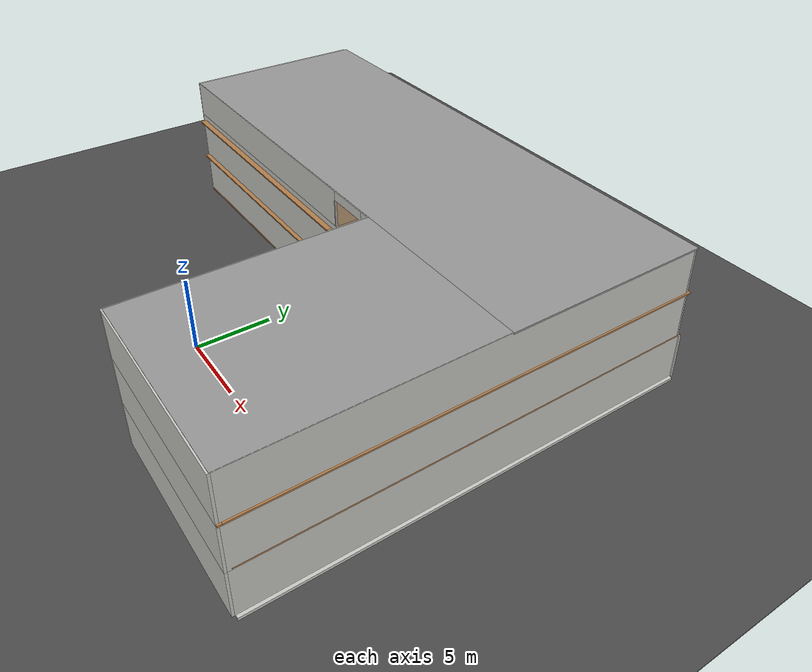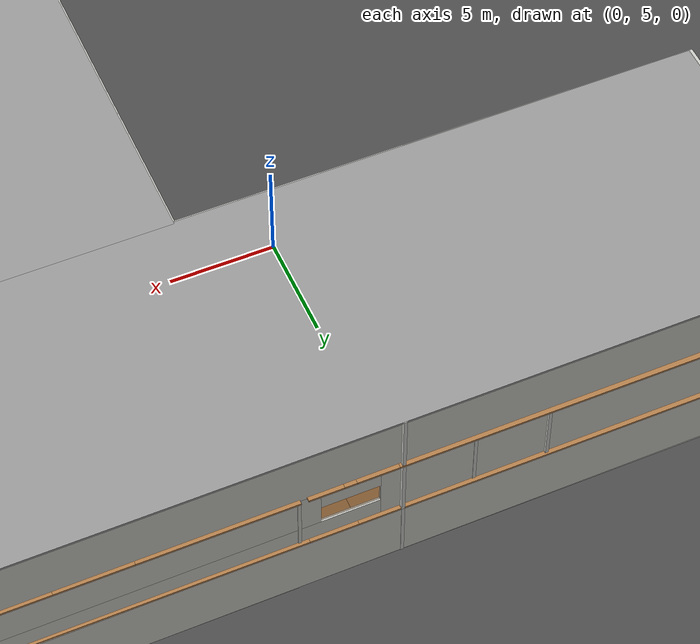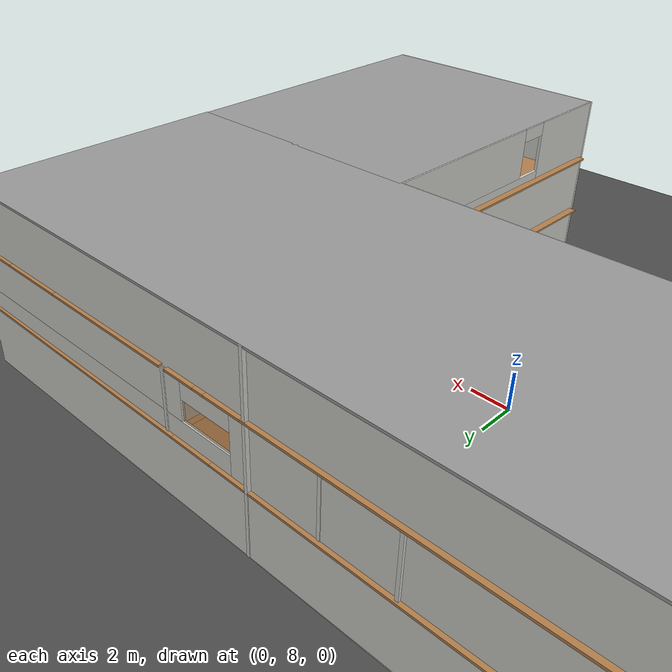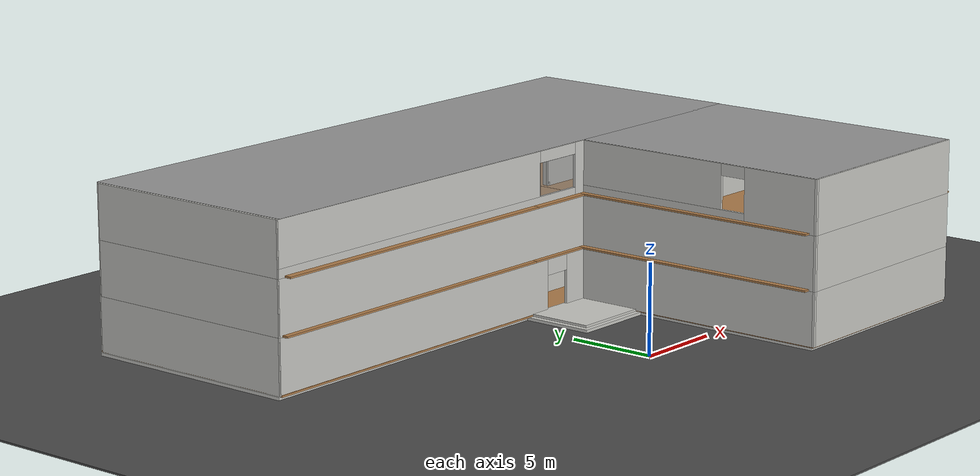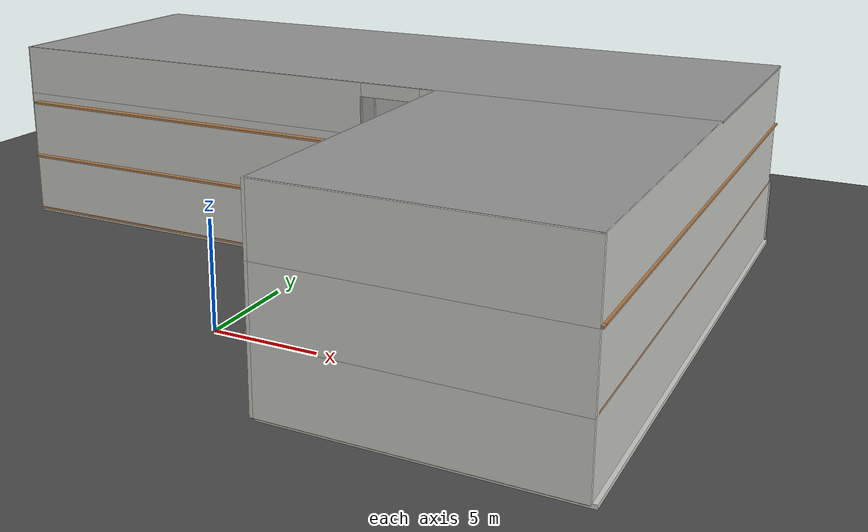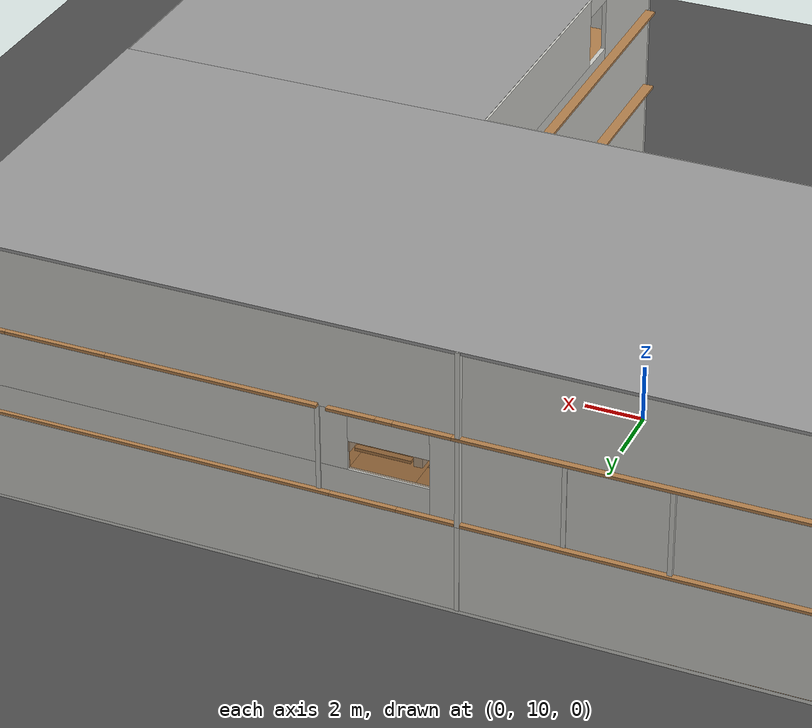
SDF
<sdf version="1.6">
 <world name="default">
  <light name="sun" type="directional">
   <pose>0 0 10 0 -0 0</pose>
   <diffuse>0.8 0.8 0.8 1</diffuse>
   <specular>0.2 0.2 0.2 1</specular>
   <attenuation>
    <range>1000</range>
    <constant>0.9</constant>
    <linear>0.01</linear>
    <quadratic>0.001</quadratic>
   </attenuation>
   <direction>-0.5 0.1 -0.9</direction>
   <spot><inner_angle>0</inner_angle><outer_angle>0</outer_angle><falloff>0</falloff></spot>
  </light>
  <gravity>0 0 -9.8</gravity>
  <magnetic_field>6e-06 2.3e-05 -4.2e-05</magnetic_field>
  <atmosphere type="adiabatic"/>
  <physics name="default_physics" default="0" type="ode">
   <max_step_size>0.001</max_step_size>
   <real_time_factor>1</real_time_factor>
   <real_time_update_rate>1000</real_time_update_rate>
  </physics>
  <scene><ambient>0.4 0.4 0.4 1</ambient><background>0.7 0.7 0.7 1</background><shadows>1</shadows></scene>
  <audio><device>default</device></audio>
  <spherical_coordinates>
   <surface_model>EARTH_WGS84</surface_model>
   <latitude_deg>0</latitude_deg>
   <longitude_deg>0</longitude_deg>
   <elevation>0</elevation>
   <heading_deg>0</heading_deg>
  </spherical_coordinates>
  <model name="asphalt_plane">
   <static>1</static>
   <link name="link">
    <collision name="collision"><geometry><box><size>200 200 0.1</size></box></geometry></collision>
    <visual name="visual">
     <cast_shadows>0</cast_shadows>
     <geometry><box><size>200 200 0.1</size></box></geometry>
     <material>
      <script>
       <uri>model://asphalt_plane/materials/scripts</uri>
       <uri>model://asphalt_plane/materials/textures</uri>
       <name>vrc/asphalt</name>
      </script>
     </material>
    </visual>
   </link>
   <pose>0.263713 2.26378 0 0 -0 0</pose>
  </model>
  <model name="add_competition_building_with_stair">
   <link name="link_0">
    <inertial>
     <mass>26.161</mass>
     <inertia><ixx>37.6217</ixx><ixy>0</ixy><ixz>0</ixz><iyy>49.4924</iyy><iyz>0</iyz><izz>86.2665</izz></inertia>
    </inertial>
    <pose>0.807052 -2.01011 0 0 -0 0</pose>
    <visual name="visual">
     <geometry><box><size>4.74422 4.13069 0.440916</size></box></geometry>
     <material>
      <lighting>1</lighting>
      <script><uri>file://media/materials/scripts/gazebo.material</uri><name>Gazebo/CeilingTiled</name></script>
      <shader type="pixel"><normal_map>__default__</normal_map></shader>
      <ambient>1 1 1 1</ambient>
      <diffuse>1 1 1 1</diffuse>
      <specular>0.01 0.01 0.01 1</specular>
      <emissive>0 0 0 1</emissive>
     </material>
    </visual>
    <collision name="collision">
     <geometry><box><size>4.74422 4.13069 0.440916</size></box></geometry>
     <surface>
      <friction>
       <ode><mu>1</mu><mu2>1</mu2><fdir1>0 0 0</fdir1><slip1>0</slip1><slip2>0</slip2></ode>
       <torsional>
        <coefficient>1</coefficient>
        <patch_radius>0</patch_radius>
        <surface_radius>0</surface_radius>
        <use_patch_radius>1</use_patch_radius>
        <ode><slip>0</slip></ode>
       </torsional>
      </friction>
      <bounce><restitution_coefficient>0</restitution_coefficient><threshold>1e+06</threshold></bounce>
      <contact>
       <collide_without_contact>0</collide_without_contact>
       <collide_without_contact_bitmask>1</collide_without_contact_bitmask>
       <collide_bitmask>1</collide_bitmask>
       <ode>
        <soft_cfm>0</soft_cfm>
        <soft_erp>0.2</soft_erp>
        <kp>1e+13</kp>
        <kd>1</kd>
        <max_vel>0.01</max_vel>
        <min_depth>0</min_depth>
       </ode>
       <bullet>
        <split_impulse>1</split_impulse>
        <split_impulse_penetration_threshold>-0.01</split_impulse_penetration_threshold>
        <soft_cfm>0</soft_cfm>
        <soft_erp>0.2</soft_erp>
        <kp>1e+13</kp>
        <kd>1</kd>
       </bullet>
      </contact>
     </surface>
    </collision>
   </link>
   <link name="link_0_clone">
    <inertial>
     <mass>0.497616</mass>
     <inertia>
      <ixx>0.613287</ixx>
      <ixy>0</ixy>
      <ixz>0</ixz>
      <iyy>0.811754</iyy>
      <iyz>0</iyz>
      <izz>1.42331</izz>
     </inertia>
    </inertial>
    <pose>0.966685 -1.86699 0.282136 0 -0 0</pose>
    <visual name="visual">
     <geometry><box><size>4.42206 3.84299 0.144334</size></box></geometry>
     <material>
      <lighting>1</lighting>
      <script><uri>file://media/materials/scripts/gazebo.material</uri><name>Gazebo/CeilingTiled</name></script>
      <shader type="pixel"><normal_map>__default__</normal_map></shader>
      <ambient>1 1 1 1</ambient>
      <diffuse>1 1 1 1</diffuse>
      <specular>0.01 0.01 0.01 1</specular>
      <emissive>0 0 0 1</emissive>
     </material>
    </visual>
    <collision name="collision">
     <geometry><box><size>4.42206 3.84299 0.144334</size></box></geometry>
     <surface>
      <friction>
       <ode><mu>1</mu><mu2>1</mu2><fdir1>0 0 0</fdir1><slip1>0</slip1><slip2>0</slip2></ode>
       <torsional>
        <coefficient>1</coefficient>
        <patch_radius>0</patch_radius>
        <surface_radius>0</surface_radius>
        <use_patch_radius>1</use_patch_radius>
        <ode><slip>0</slip></ode>
       </torsional>
      </friction>
      <bounce><restitution_coefficient>0</restitution_coefficient><threshold>1e+06</threshold></bounce>
      <contact>
       <collide_without_contact>0</collide_without_contact>
       <collide_without_contact_bitmask>1</collide_without_contact_bitmask>
       <collide_bitmask>1</collide_bitmask>
       <ode>
        <soft_cfm>0</soft_cfm>
        <soft_erp>0.2</soft_erp>
        <kp>1e+13</kp>
        <kd>1</kd>
        <max_vel>0.01</max_vel>
        <min_depth>0</min_depth>
       </ode>
       <bullet>
        <split_impulse>1</split_impulse>
        <split_impulse_penetration_threshold>-0.01</split_impulse_penetration_threshold>
        <soft_cfm>0</soft_cfm>
        <soft_erp>0.2</soft_erp>
        <kp>1e+13</kp>
        <kd>1</kd>
       </bullet>
      </contact>
     </surface>
    </collision>
   </link>
   <link name="link_2">
    <inertial>
     <mass>163.316</mass>
     <inertia><ixx>10717.1</ixx><ixy>0</ixy><ixz>0</ixz><iyy>2242.65</iyy><iyz>0</iyz><izz>12954.1</izz></inertia>
    </inertial>
    <pose>9.59679 -1.25874 0 0 -0 0</pose>
    <visual name="visual">
     <geometry><box><size>12.8288 28.0581 0.453943</size></box></geometry>
     <material>
      <lighting>1</lighting>
      <script><uri>file://media/materials/scripts/gazebo.material</uri><name>Gazebo/CeilingTiled</name></script>
      <shader type="pixel"><normal_map>__default__</normal_map></shader>
      <ambient>1 1 1 1</ambient>
      <diffuse>1 1 1 1</diffuse>
      <specular>0.01 0.01 0.01 1</specular>
      <emissive>0 0 0 1</emissive>
     </material>
    </visual>
    <collision name="collision">
     <geometry><box><size>12.8288 28.0581 0.453943</size></box></geometry>
     <surface>
      <friction>
       <ode><mu>1</mu><mu2>1</mu2><fdir1>0 0 0</fdir1><slip1>0</slip1><slip2>0</slip2></ode>
       <torsional>
        <coefficient>1</coefficient>
        <patch_radius>0</patch_radius>
        <surface_radius>0</surface_radius>
        <use_patch_radius>1</use_patch_radius>
        <ode><slip>0</slip></ode>
       </torsional>
      </friction>
      <bounce><restitution_coefficient>0</restitution_coefficient><threshold>1e+06</threshold></bounce>
      <contact>
       <collide_without_contact>0</collide_without_contact>
       <collide_without_contact_bitmask>1</collide_without_contact_bitmask>
       <collide_bitmask>1</collide_bitmask>
       <ode>
        <soft_cfm>0</soft_cfm>
        <soft_erp>0.2</soft_erp>
        <kp>1e+13</kp>
        <kd>1</kd>
        <max_vel>0.01</max_vel>
        <min_depth>0</min_depth>
       </ode>
       <bullet>
        <split_impulse>1</split_impulse>
        <split_impulse_penetration_threshold>-0.01</split_impulse_penetration_threshold>
        <soft_cfm>0</soft_cfm>
        <soft_erp>0.2</soft_erp>
        <kp>1e+13</kp>
        <kd>1</kd>
       </bullet>
      </contact>
     </surface>
    </collision>
   </link>
   <link name="link_2_clone">
    <inertial>
     <mass>139.72</mass>
     <inertia><ixx>1892.14</ixx><ixy>0</ixy><ixz>0</ixz><iyy>6805.44</iyy><iyz>0</iyz><izz>8692.78</izz></inertia>
    </inertial>
    <pose>-8.83545 6.37789 0 0 -0 0</pose>
    <visual name="visual">
     <geometry><box><size>24.172 12.7398 0.453943</size></box></geometry>
     <material>
      <lighting>1</lighting>
      <script><uri>file://media/materials/scripts/gazebo.material</uri><name>Gazebo/CeilingTiled</name></script>
      <shader type="pixel"><normal_map>__default__</normal_map></shader>
      <ambient>1 1 1 1</ambient>
      <diffuse>1 1 1 1</diffuse>
      <specular>0.01 0.01 0.01 1</specular>
      <emissive>0 0 0 1</emissive>
     </material>
    </visual>
    <collision name="collision">
     <geometry><box><size>24.172 12.7398 0.453943</size></box></geometry>
     <surface>
      <friction>
       <ode><mu>1</mu><mu2>1</mu2><fdir1>0 0 0</fdir1><slip1>0</slip1><slip2>0</slip2></ode>
       <torsional>
        <coefficient>1</coefficient>
        <patch_radius>0</patch_radius>
        <surface_radius>0</surface_radius>
        <use_patch_radius>1</use_patch_radius>
        <ode><slip>0</slip></ode>
       </torsional>
      </friction>
      <bounce><restitution_coefficient>0</restitution_coefficient><threshold>1e+06</threshold></bounce>
      <contact>
       <collide_without_contact>0</collide_without_contact>
       <collide_without_contact_bitmask>1</collide_without_contact_bitmask>
       <collide_bitmask>1</collide_bitmask>
       <ode>
        <soft_cfm>0</soft_cfm>
        <soft_erp>0.2</soft_erp>
        <kp>1e+13</kp>
        <kd>1</kd>
        <max_vel>0.01</max_vel>
        <min_depth>0</min_depth>
       </ode>
       <bullet>
        <split_impulse>1</split_impulse>
        <split_impulse_penetration_threshold>-0.01</split_impulse_penetration_threshold>
        <soft_cfm>0</soft_cfm>
        <soft_erp>0.2</soft_erp>
        <kp>1e+13</kp>
        <kd>1</kd>
       </bullet>
      </contact>
     </surface>
    </collision>
   </link>
   <model name="add_competition_building">
    <link name="Floor_17">
     <pose>-1e-06 0 3 0 -0 0</pose>
     <inertial>
      <mass>1</mass>
      <inertia><ixx>1</ixx><ixy>0</ixy><ixz>0</ixz><iyy>1</iyy><iyz>0</iyz><izz>1</izz></inertia>
     </inertial>
     <visual name="Floor_17_Visual_4">
      <pose>3.2474 4.68982 0.05 0 -0 0</pose>
      <geometry><box><size>3.99082 7.61431 0.1</size></box></geometry>
      <material>
       <script><uri>file://media/materials/scripts/gazebo.material</uri><name>Gazebo/WoodFloor</name></script>
       <ambient>1 1 1 1</ambient>
       <shader type="pixel"><normal_map>__default__</normal_map></shader>
      </material>
      <meta><layer>1</layer></meta>
     </visual>
     <visual name="Floor_17_Visual_2">
      <pose>11.809 0.186054 0.05 0 -0 0</pose>
      <geometry><box><size>13.1324 28.0049 0.1</size></box></geometry>
      <material>
       <script><uri>file://media/materials/scripts/gazebo.material</uri><name>Gazebo/WoodFloor</name></script>
       <ambient>1 1 1 1</ambient>
       <shader type="pixel"><normal_map>__default__</normal_map></shader>
      </material>
      <meta><layer>1</layer></meta>
     </visual>
     <visual name="Floor_17_Visual_3">
      <pose>-8.4406 7.53558 0.05 0 -0 0</pose>
      <geometry><box><size>19.3852 13.3058 0.1</size></box></geometry>
      <material>
       <script><uri>file://media/materials/scripts/gazebo.material</uri><name>Gazebo/WoodFloor</name></script>
       <ambient>1 1 1 1</ambient>
       <shader type="pixel"><normal_map>__default__</normal_map></shader>
      </material>
      <meta><layer>1</layer></meta>
     </visual>
     <visual name="Floor_17_Visual_6">
      <pose>2.17698 12.9972 0.05 0 -0 0</pose>
      <geometry><box><size>1.85 2.38252 0.1</size></box></geometry>
      <material>
       <script><uri>file://media/materials/scripts/gazebo.material</uri><name>Gazebo/WoodFloor</name></script>
       <ambient>1 1 1 1</ambient>
       <shader type="pixel"><normal_map>__default__</normal_map></shader>
      </material>
      <meta><layer>1</layer></meta>
     </visual>
     <visual name="Floor_17_Visual_5">
      <pose>4.17239 11.3427 0.05 0 -0 0</pose>
      <geometry><box><size>2.14082 5.69152 0.1</size></box></geometry>
      <material>
       <script><uri>file://media/materials/scripts/gazebo.material</uri><name>Gazebo/WoodFloor</name></script>
       <ambient>1 1 1 1</ambient>
       <shader type="pixel"><normal_map>__default__</normal_map></shader>
      </material>
      <meta><layer>1</layer></meta>
     </visual>
     <collision name="Floor_17_Collision_6">
      <pose>2.17698 12.9972 0.05 0 -0 0</pose>
      <geometry><box><size>1.85 2.38252 0.1</size></box></geometry>
      <surface>
       <friction>
        <ode><mu>1</mu><mu2>1</mu2><fdir1>0 0 0</fdir1><slip1>0</slip1><slip2>0</slip2></ode>
        <torsional>
         <coefficient>1</coefficient>
         <patch_radius>0</patch_radius>
         <surface_radius>0</surface_radius>
         <use_patch_radius>1</use_patch_radius>
         <ode><slip>0</slip></ode>
        </torsional>
       </friction>
       <bounce><restitution_coefficient>0</restitution_coefficient><threshold>1e+06</threshold></bounce>
       <contact>
        <collide_without_contact>0</collide_without_contact>
        <collide_without_contact_bitmask>1</collide_without_contact_bitmask>
        <collide_bitmask>1</collide_bitmask>
        <ode>
         <soft_cfm>0</soft_cfm>
         <soft_erp>0.2</soft_erp>
         <kp>1e+13</kp>
         <kd>1</kd>
         <max_vel>0.01</max_vel>
         <min_depth>0</min_depth>
        </ode>
        <bullet>
         <split_impulse>1</split_impulse>
         <split_impulse_penetration_threshold>-0.01</split_impulse_penetration_threshold>
         <soft_cfm>0</soft_cfm>
         <soft_erp>0.2</soft_erp>
         <kp>1e+13</kp>
         <kd>1</kd>
        </bullet>
       </contact>
      </surface>
     </collision>
     <collision name="Floor_17_Collision_4">
      <pose>3.2474 4.68982 0.05 0 -0 0</pose>
      <geometry><box><size>3.99082 7.61431 0.1</size></box></geometry>
      <surface>
       <friction>
        <ode><mu>1</mu><mu2>1</mu2><fdir1>0 0 0</fdir1><slip1>0</slip1><slip2>0</slip2></ode>
        <torsional>
         <coefficient>1</coefficient>
         <patch_radius>0</patch_radius>
         <surface_radius>0</surface_radius>
         <use_patch_radius>1</use_patch_radius>
         <ode><slip>0</slip></ode>
        </torsional>
       </friction>
       <bounce><restitution_coefficient>0</restitution_coefficient><threshold>1e+06</threshold></bounce>
       <contact>
        <collide_without_contact>0</collide_without_contact>
        <collide_without_contact_bitmask>1</collide_without_contact_bitmask>
        <collide_bitmask>1</collide_bitmask>
        <ode>
         <soft_cfm>0</soft_cfm>
         <soft_erp>0.2</soft_erp>
         <kp>1e+13</kp>
         <kd>1</kd>
         <max_vel>0.01</max_vel>
         <min_depth>0</min_depth>
        </ode>
        <bullet>
         <split_impulse>1</split_impulse>
         <split_impulse_penetration_threshold>-0.01</split_impulse_penetration_threshold>
         <soft_cfm>0</soft_cfm>
         <soft_erp>0.2</soft_erp>
         <kp>1e+13</kp>
         <kd>1</kd>
        </bullet>
       </contact>
      </surface>
     </collision>
     <collision name="Floor_17_Collision_2">
      <pose>11.809 0.186054 0.05 0 -0 0</pose>
      <geometry><box><size>13.1324 28.0049 0.1</size></box></geometry>
      <surface>
       <friction>
        <ode><mu>1</mu><mu2>1</mu2><fdir1>0 0 0</fdir1><slip1>0</slip1><slip2>0</slip2></ode>
        <torsional>
         <coefficient>1</coefficient>
         <patch_radius>0</patch_radius>
         <surface_radius>0</surface_radius>
         <use_patch_radius>1</use_patch_radius>
         <ode><slip>0</slip></ode>
        </torsional>
       </friction>
       <bounce><restitution_coefficient>0</restitution_coefficient><threshold>1e+06</threshold></bounce>
       <contact>
        <collide_without_contact>0</collide_without_contact>
        <collide_without_contact_bitmask>1</collide_without_contact_bitmask>
        <collide_bitmask>1</collide_bitmask>
        <ode>
         <soft_cfm>0</soft_cfm>
         <soft_erp>0.2</soft_erp>
         <kp>1e+13</kp>
         <kd>1</kd>
         <max_vel>0.01</max_vel>
         <min_depth>0</min_depth>
        </ode>
        <bullet>
         <split_impulse>1</split_impulse>
         <split_impulse_penetration_threshold>-0.01</split_impulse_penetration_threshold>
         <soft_cfm>0</soft_cfm>
         <soft_erp>0.2</soft_erp>
         <kp>1e+13</kp>
         <kd>1</kd>
        </bullet>
       </contact>
      </surface>
     </collision>
     <collision name="Floor_17_Collision_3">
      <pose>-8.4406 7.53558 0.05 0 -0 0</pose>
      <geometry><box><size>19.3852 13.3058 0.1</size></box></geometry>
      <surface>
       <friction>
        <ode><mu>1</mu><mu2>1</mu2><fdir1>0 0 0</fdir1><slip1>0</slip1><slip2>0</slip2></ode>
        <torsional>
         <coefficient>1</coefficient>
         <patch_radius>0</patch_radius>
         <surface_radius>0</surface_radius>
         <use_patch_radius>1</use_patch_radius>
         <ode><slip>0</slip></ode>
        </torsional>
       </friction>
       <bounce><restitution_coefficient>0</restitution_coefficient><threshold>1e+06</threshold></bounce>
       <contact>
        <collide_without_contact>0</collide_without_contact>
        <collide_without_contact_bitmask>1</collide_without_contact_bitmask>
        <collide_bitmask>1</collide_bitmask>
        <ode>
         <soft_cfm>0</soft_cfm>
         <soft_erp>0.2</soft_erp>
         <kp>1e+13</kp>
         <kd>1</kd>
         <max_vel>0.01</max_vel>
         <min_depth>0</min_depth>
        </ode>
        <bullet>
         <split_impulse>1</split_impulse>
         <split_impulse_penetration_threshold>-0.01</split_impulse_penetration_threshold>
         <soft_cfm>0</soft_cfm>
         <soft_erp>0.2</soft_erp>
         <kp>1e+13</kp>
         <kd>1</kd>
        </bullet>
       </contact>
      </surface>
     </collision>
     <collision name="Floor_17_Collision_5">
      <pose>4.17239 11.3427 0.05 0 -0 0</pose>
      <geometry><box><size>2.14082 5.69152 0.1</size></box></geometry>
      <surface>
       <friction>
        <ode><mu>1</mu><mu2>1</mu2><fdir1>0 0 0</fdir1><slip1>0</slip1><slip2>0</slip2></ode>
        <torsional>
         <coefficient>1</coefficient>
         <patch_radius>0</patch_radius>
         <surface_radius>0</surface_radius>
         <use_patch_radius>1</use_patch_radius>
         <ode><slip>0</slip></ode>
        </torsional>
       </friction>
       <bounce><restitution_coefficient>0</restitution_coefficient><threshold>1e+06</threshold></bounce>
       <contact>
        <collide_without_contact>0</collide_without_contact>
        <collide_without_contact_bitmask>1</collide_without_contact_bitmask>
        <collide_bitmask>1</collide_bitmask>
        <ode>
         <soft_cfm>0</soft_cfm>
         <soft_erp>0.2</soft_erp>
         <kp>1e+13</kp>
         <kd>1</kd>
         <max_vel>0.01</max_vel>
         <min_depth>0</min_depth>
        </ode>
        <bullet>
         <split_impulse>1</split_impulse>
         <split_impulse_penetration_threshold>-0.01</split_impulse_penetration_threshold>
         <soft_cfm>0</soft_cfm>
         <soft_erp>0.2</soft_erp>
         <kp>1e+13</kp>
         <kd>1</kd>
        </bullet>
       </contact>
      </surface>
     </collision>
    </link>
    <link name="Floor_19">
     <pose>0.111185 0.017212 6 0 -0 0</pose>
     <inertial>
      <mass>1</mass>
      <inertia><ixx>1</ixx><ixy>0</ixy><ixz>0</ixz><iyy>1</iyy><iyz>0</iyz><izz>1</izz></inertia>
     </inertial>
     <visual name="Floor_19_Visual_12">
      <pose>4.39145 13.0153 0.05 0 -0 0</pose>
      <geometry><box><size>1.54234 2.34643 0.1</size></box></geometry>
      <material>
       <script><uri>file://media/materials/scripts/gazebo.material</uri><name>Gazebo/WoodFloor</name></script>
       <ambient>1 1 1 1</ambient>
       <shader type="pixel"><normal_map>__default__</normal_map></shader>
      </material>
      <meta><layer>2</layer></meta>
     </visual>
     <visual name="Floor_19_Visual_7">
      <pose>3.19702 4.67446 0.05 0 -0 0</pose>
      <geometry><box><size>3.93119 7.77785 0.1</size></box></geometry>
      <material>
       <script><uri>file://media/materials/scripts/gazebo.material</uri><name>Gazebo/WoodFloor</name></script>
       <ambient>1 1 1 1</ambient>
       <shader type="pixel"><normal_map>__default__</normal_map></shader>
      </material>
      <meta><layer>2</layer></meta>
     </visual>
     <visual name="Floor_19_Visual_11">
      <pose>2.15643 13.0151 0.05 0 -0 0</pose>
      <geometry><box><size>1.85 2.34685 0.1</size></box></geometry>
      <material>
       <script><uri>file://media/materials/scripts/gazebo.material</uri><name>Gazebo/WoodFloor</name></script>
       <ambient>1 1 1 1</ambient>
       <shader type="pixel"><normal_map>__default__</normal_map></shader>
      </material>
      <meta><layer>2</layer></meta>
     </visual>
     <visual name="Floor_19_Visual_3">
      <pose>17.0737 0.122308 0.05 0 -0 0</pose>
      <geometry><box><size>2.60309 28.1324 0.1</size></box></geometry>
      <material>
       <script><uri>file://media/materials/scripts/gazebo.material</uri><name>Gazebo/WoodFloor</name></script>
       <ambient>1 1 1 1</ambient>
       <shader type="pixel"><normal_map>__default__</normal_map></shader>
      </material>
      <meta><layer>2</layer></meta>
     </visual>
     <visual name="Floor_19_Visual_5">
      <pose>14.0846 1.10138 0.05 0 -0 0</pose>
      <geometry><box><size>3.37505 26.1742 0.1</size></box></geometry>
      <material>
       <script><uri>file://media/materials/scripts/gazebo.material</uri><name>Gazebo/WoodFloor</name></script>
       <ambient>1 1 1 1</ambient>
       <shader type="pixel"><normal_map>__default__</normal_map></shader>
      </material>
      <meta><layer>2</layer></meta>
     </visual>
     <visual name="Floor_19_Visual_9">
      <pose>4.39145 8.57012 0.05 0 -0 0</pose>
      <geometry><box><size>1.54234 0.013466 0.1</size></box></geometry>
      <material>
       <script><uri>file://media/materials/scripts/gazebo.material</uri><name>Gazebo/WoodFloor</name></script>
       <ambient>1 1 1 1</ambient>
       <shader type="pixel"><normal_map>__default__</normal_map></shader>
      </material>
      <meta><layer>2</layer></meta>
     </visual>
     <visual name="Floor_19_Visual_6">
      <pose>-8.39526 7.48702 0.05 0 -0 0</pose>
      <geometry><box><size>19.2534 13.403 0.1</size></box></geometry>
      <material>
       <script><uri>file://media/materials/scripts/gazebo.material</uri><name>Gazebo/WoodFloor</name></script>
       <ambient>1 1 1 1</ambient>
       <shader type="pixel"><normal_map>__default__</normal_map></shader>
      </material>
      <meta><layer>2</layer></meta>
     </visual>
     <visual name="Floor_19_Visual_10">
      <pose>8.93367 11.3827 0.05 0 -0 0</pose>
      <geometry><box><size>6.92679 5.61165 0.1</size></box></geometry>
      <material>
       <script><uri>file://media/materials/scripts/gazebo.material</uri><name>Gazebo/WoodFloor</name></script>
       <ambient>1 1 1 1</ambient>
       <shader type="pixel"><normal_map>__default__</normal_map></shader>
      </material>
      <meta><layer>2</layer></meta>
     </visual>
     <visual name="Floor_19_Visual_4">
      <pose>8.77984 -2.595 0.05 0 -0 0</pose>
      <geometry><box><size>7.23445 22.3437 0.1</size></box></geometry>
      <material>
       <script><uri>file://media/materials/scripts/gazebo.material</uri><name>Gazebo/WoodFloor</name></script>
       <ambient>1 1 1 1</ambient>
       <shader type="pixel"><normal_map>__default__</normal_map></shader>
      </material>
      <meta><layer>2</layer></meta>
     </visual>
     <visual name="Floor_19_Visual_8">
      <pose>3.35085 11.3759 0.05 0 -0 0</pose>
      <geometry><box><size>0.538854 5.62511 0.1</size></box></geometry>
      <material>
       <script><uri>file://media/materials/scripts/gazebo.material</uri><name>Gazebo/WoodFloor</name></script>
       <ambient>1 1 1 1</ambient>
       <shader type="pixel"><normal_map>__default__</normal_map></shader>
      </material>
      <meta><layer>2</layer></meta>
     </visual>
     <visual name="Floor_19_Visual_2">
      <pose>15.3861 -14.0662 0.05 0 -0 0</pose>
      <geometry><box><size>5.97814 0.244616 0.1</size></box></geometry>
      <material>
       <script><uri>file://media/materials/scripts/gazebo.material</uri><name>Gazebo/WoodFloor</name></script>
       <ambient>1 1 1 1</ambient>
       <shader type="pixel"><normal_map>__default__</normal_map></shader>
      </material>
      <meta><layer>2</layer></meta>
     </visual>
     <collision name="Floor_19_Collision_7">
      <pose>3.19702 4.67446 0.05 0 -0 0</pose>
      <geometry><box><size>3.93119 7.77785 0.1</size></box></geometry>
      <surface>
       <friction>
        <ode><mu>1</mu><mu2>1</mu2><fdir1>0 0 0</fdir1><slip1>0</slip1><slip2>0</slip2></ode>
        <torsional>
         <coefficient>1</coefficient>
         <patch_radius>0</patch_radius>
         <surface_radius>0</surface_radius>
         <use_patch_radius>1</use_patch_radius>
         <ode><slip>0</slip></ode>
        </torsional>
       </friction>
       <bounce><restitution_coefficient>0</restitution_coefficient><threshold>1e+06</threshold></bounce>
       <contact>
        <collide_without_contact>0</collide_without_contact>
        <collide_without_contact_bitmask>1</collide_without_contact_bitmask>
        <collide_bitmask>1</collide_bitmask>
        <ode>
         <soft_cfm>0</soft_cfm>
         <soft_erp>0.2</soft_erp>
         <kp>1e+13</kp>
         <kd>1</kd>
         <max_vel>0.01</max_vel>
         <min_depth>0</min_depth>
        </ode>
        <bullet>
         <split_impulse>1</split_impulse>
         <split_impulse_penetration_threshold>-0.01</split_impulse_penetration_threshold>
         <soft_cfm>0</soft_cfm>
         <soft_erp>0.2</soft_erp>
         <kp>1e+13</kp>
         <kd>1</kd>
        </bullet>
       </contact>
      </surface>
     </collision>
     <collision name="Floor_19_Collision_4">
      <pose>8.77984 -2.595 0.05 0 -0 0</pose>
      <geometry><box><size>7.23445 22.3437 0.1</size></box></geometry>
      <surface>
       <friction>
        <ode><mu>1</mu><mu2>1</mu2><fdir1>0 0 0</fdir1><slip1>0</slip1><slip2>0</slip2></ode>
        <torsional>
         <coefficient>1</coefficient>
         <patch_radius>0</patch_radius>
         <surface_radius>0</surface_radius>
         <use_patch_radius>1</use_patch_radius>
         <ode><slip>0</slip></ode>
        </torsional>
       </friction>
       <bounce><restitution_coefficient>0</restitution_coefficient><threshold>1e+06</threshold></bounce>
       <contact>
        <collide_without_contact>0</collide_without_contact>
        <collide_without_contact_bitmask>1</collide_without_contact_bitmask>
        <collide_bitmask>1</collide_bitmask>
        <ode>
         <soft_cfm>0</soft_cfm>
         <soft_erp>0.2</soft_erp>
         <kp>1e+13</kp>
         <kd>1</kd>
         <max_vel>0.01</max_vel>
         <min_depth>0</min_depth>
        </ode>
        <bullet>
         <split_impulse>1</split_impulse>
         <split_impulse_penetration_threshold>-0.01</split_impulse_penetration_threshold>
         <soft_cfm>0</soft_cfm>
         <soft_erp>0.2</soft_erp>
         <kp>1e+13</kp>
         <kd>1</kd>
        </bullet>
       </contact>
      </surface>
     </collision>
     <collision name="Floor_19_Collision_11">
      <pose>2.15643 13.0151 0.05 0 -0 0</pose>
      <geometry><box><size>1.85 2.34685 0.1</size></box></geometry>
      <surface>
       <friction>
        <ode><mu>1</mu><mu2>1</mu2><fdir1>0 0 0</fdir1><slip1>0</slip1><slip2>0</slip2></ode>
        <torsional>
         <coefficient>1</coefficient>
         <patch_radius>0</patch_radius>
         <surface_radius>0</surface_radius>
         <use_patch_radius>1</use_patch_radius>
         <ode><slip>0</slip></ode>
        </torsional>
       </friction>
       <bounce><restitution_coefficient>0</restitution_coefficient><threshold>1e+06</threshold></bounce>
       <contact>
        <collide_without_contact>0</collide_without_contact>
        <collide_without_contact_bitmask>1</collide_without_contact_bitmask>
        <collide_bitmask>1</collide_bitmask>
        <ode>
         <soft_cfm>0</soft_cfm>
         <soft_erp>0.2</soft_erp>
         <kp>1e+13</kp>
         <kd>1</kd>
         <max_vel>0.01</max_vel>
         <min_depth>0</min_depth>
        </ode>
        <bullet>
         <split_impulse>1</split_impulse>
         <split_impulse_penetration_threshold>-0.01</split_impulse_penetration_threshold>
         <soft_cfm>0</soft_cfm>
         <soft_erp>0.2</soft_erp>
         <kp>1e+13</kp>
         <kd>1</kd>
        </bullet>
       </contact>
      </surface>
     </collision>
     <collision name="Floor_19_Collision_2">
      <pose>15.3861 -14.0662 0.05 0 -0 0</pose>
      <geometry><box><size>5.97814 0.244616 0.1</size></box></geometry>
      <surface>
       <friction>
        <ode><mu>1</mu><mu2>1</mu2><fdir1>0 0 0</fdir1><slip1>0</slip1><slip2>0</slip2></ode>
        <torsional>
         <coefficient>1</coefficient>
         <patch_radius>0</patch_radius>
         <surface_radius>0</surface_radius>
         <use_patch_radius>1</use_patch_radius>
         <ode><slip>0</slip></ode>
        </torsional>
       </friction>
       <bounce><restitution_coefficient>0</restitution_coefficient><threshold>1e+06</threshold></bounce>
       <contact>
        <collide_without_contact>0</collide_without_contact>
        <collide_without_contact_bitmask>1</collide_without_contact_bitmask>
        <collide_bitmask>1</collide_bitmask>
        <ode>
         <soft_cfm>0</soft_cfm>
         <soft_erp>0.2</soft_erp>
         <kp>1e+13</kp>
         <kd>1</kd>
         <max_vel>0.01</max_vel>
         <min_depth>0</min_depth>
        </ode>
        <bullet>
         <split_impulse>1</split_impulse>
         <split_impulse_penetration_threshold>-0.01</split_impulse_penetration_threshold>
         <soft_cfm>0</soft_cfm>
         <soft_erp>0.2</soft_erp>
         <kp>1e+13</kp>
         <kd>1</kd>
        </bullet>
       </contact>
      </surface>
     </collision>
     <collision name="Floor_19_Collision_8">
      <pose>3.35085 11.3759 0.05 0 -0 0</pose>
      <geometry><box><size>0.538854 5.62511 0.1</size></box></geometry>
      <surface>
       <friction>
        <ode><mu>1</mu><mu2>1</mu2><fdir1>0 0 0</fdir1><slip1>0</slip1><slip2>0</slip2></ode>
        <torsional>
         <coefficient>1</coefficient>
         <patch_radius>0</patch_radius>
         <surface_radius>0</surface_radius>
         <use_patch_radius>1</use_patch_radius>
         <ode><slip>0</slip></ode>
        </torsional>
       </friction>
       <bounce><restitution_coefficient>0</restitution_coefficient><threshold>1e+06</threshold></bounce>
       <contact>
        <collide_without_contact>0</collide_without_contact>
        <collide_without_contact_bitmask>1</collide_without_contact_bitmask>
        <collide_bitmask>1</collide_bitmask>
        <ode>
         <soft_cfm>0</soft_cfm>
         <soft_erp>0.2</soft_erp>
         <kp>1e+13</kp>
         <kd>1</kd>
         <max_vel>0.01</max_vel>
         <min_depth>0</min_depth>
        </ode>
        <bullet>
         <split_impulse>1</split_impulse>
         <split_impulse_penetration_threshold>-0.01</split_impulse_penetration_threshold>
         <soft_cfm>0</soft_cfm>
         <soft_erp>0.2</soft_erp>
         <kp>1e+13</kp>
         <kd>1</kd>
        </bullet>
       </contact>
      </surface>
     </collision>
     <collision name="Floor_19_Collision_12">
      <pose>4.39145 13.0153 0.05 0 -0 0</pose>
      <geometry><box><size>1.54234 2.34643 0.1</size></box></geometry>
      <surface>
       <friction>
        <ode><mu>1</mu><mu2>1</mu2><fdir1>0 0 0</fdir1><slip1>0</slip1><slip2>0</slip2></ode>
        <torsional>
         <coefficient>1</coefficient>
         <patch_radius>0</patch_radius>
         <surface_radius>0</surface_radius>
         <use_patch_radius>1</use_patch_radius>
         <ode><slip>0</slip></ode>
        </torsional>
       </friction>
       <bounce><restitution_coefficient>0</restitution_coefficient><threshold>1e+06</threshold></bounce>
       <contact>
        <collide_without_contact>0</collide_without_contact>
        <collide_without_contact_bitmask>1</collide_without_contact_bitmask>
        <collide_bitmask>1</collide_bitmask>
        <ode>
         <soft_cfm>0</soft_cfm>
         <soft_erp>0.2</soft_erp>
         <kp>1e+13</kp>
         <kd>1</kd>
         <max_vel>0.01</max_vel>
         <min_depth>0</min_depth>
        </ode>
        <bullet>
         <split_impulse>1</split_impulse>
         <split_impulse_penetration_threshold>-0.01</split_impulse_penetration_threshold>
         <soft_cfm>0</soft_cfm>
         <soft_erp>0.2</soft_erp>
         <kp>1e+13</kp>
         <kd>1</kd>
        </bullet>
       </contact>
      </surface>
     </collision>
     <collision name="Floor_19_Collision_10">
      <pose>8.93367 11.3827 0.05 0 -0 0</pose>
      <geometry><box><size>6.92679 5.61165 0.1</size></box></geometry>
      <surface>
       <friction>
        <ode><mu>1</mu><mu2>1</mu2><fdir1>0 0 0</fdir1><slip1>0</slip1><slip2>0</slip2></ode>
        <torsional>
         <coefficient>1</coefficient>
         <patch_radius>0</patch_radius>
         <surface_radius>0</surface_radius>
         <use_patch_radius>1</use_patch_radius>
         <ode><slip>0</slip></ode>
        </torsional>
       </friction>
       <bounce><restitution_coefficient>0</restitution_coefficient><threshold>1e+06</threshold></bounce>
       <contact>
        <collide_without_contact>0</collide_without_contact>
        <collide_without_contact_bitmask>1</collide_without_contact_bitmask>
        <collide_bitmask>1</collide_bitmask>
        <ode>
         <soft_cfm>0</soft_cfm>
         <soft_erp>0.2</soft_erp>
         <kp>1e+13</kp>
         <kd>1</kd>
         <max_vel>0.01</max_vel>
         <min_depth>0</min_depth>
        </ode>
        <bullet>
         <split_impulse>1</split_impulse>
         <split_impulse_penetration_threshold>-0.01</split_impulse_penetration_threshold>
         <soft_cfm>0</soft_cfm>
         <soft_erp>0.2</soft_erp>
         <kp>1e+13</kp>
         <kd>1</kd>
        </bullet>
       </contact>
      </surface>
     </collision>
     <collision name="Floor_19_Collision_9">
      <pose>4.39145 8.57012 0.05 0 -0 0</pose>
      <geometry><box><size>1.54234 0.013466 0.1</size></box></geometry>
      <surface>
       <friction>
        <ode><mu>1</mu><mu2>1</mu2><fdir1>0 0 0</fdir1><slip1>0</slip1><slip2>0</slip2></ode>
        <torsional>
         <coefficient>1</coefficient>
         <patch_radius>0</patch_radius>
         <surface_radius>0</surface_radius>
         <use_patch_radius>1</use_patch_radius>
         <ode><slip>0</slip></ode>
        </torsional>
       </friction>
       <bounce><restitution_coefficient>0</restitution_coefficient><threshold>1e+06</threshold></bounce>
       <contact>
        <collide_without_contact>0</collide_without_contact>
        <collide_without_contact_bitmask>1</collide_without_contact_bitmask>
        <collide_bitmask>1</collide_bitmask>
        <ode>
         <soft_cfm>0</soft_cfm>
         <soft_erp>0.2</soft_erp>
         <kp>1e+13</kp>
         <kd>1</kd>
         <max_vel>0.01</max_vel>
         <min_depth>0</min_depth>
        </ode>
        <bullet>
         <split_impulse>1</split_impulse>
         <split_impulse_penetration_threshold>-0.01</split_impulse_penetration_threshold>
         <soft_cfm>0</soft_cfm>
         <soft_erp>0.2</soft_erp>
         <kp>1e+13</kp>
         <kd>1</kd>
        </bullet>
       </contact>
      </surface>
     </collision>
     <collision name="Floor_19_Collision_5">
      <pose>14.0846 1.10138 0.05 0 -0 0</pose>
      <geometry><box><size>3.37505 26.1742 0.1</size></box></geometry>
      <surface>
       <friction>
        <ode><mu>1</mu><mu2>1</mu2><fdir1>0 0 0</fdir1><slip1>0</slip1><slip2>0</slip2></ode>
        <torsional>
         <coefficient>1</coefficient>
         <patch_radius>0</patch_radius>
         <surface_radius>0</surface_radius>
         <use_patch_radius>1</use_patch_radius>
         <ode><slip>0</slip></ode>
        </torsional>
       </friction>
       <bounce><restitution_coefficient>0</restitution_coefficient><threshold>1e+06</threshold></bounce>
       <contact>
        <collide_without_contact>0</collide_without_contact>
        <collide_without_contact_bitmask>1</collide_without_contact_bitmask>
        <collide_bitmask>1</collide_bitmask>
        <ode>
         <soft_cfm>0</soft_cfm>
         <soft_erp>0.2</soft_erp>
         <kp>1e+13</kp>
         <kd>1</kd>
         <max_vel>0.01</max_vel>
         <min_depth>0</min_depth>
        </ode>
        <bullet>
         <split_impulse>1</split_impulse>
         <split_impulse_penetration_threshold>-0.01</split_impulse_penetration_threshold>
         <soft_cfm>0</soft_cfm>
         <soft_erp>0.2</soft_erp>
         <kp>1e+13</kp>
         <kd>1</kd>
        </bullet>
       </contact>
      </surface>
     </collision>
     <collision name="Floor_19_Collision_3">
      <pose>17.0737 0.122308 0.05 0 -0 0</pose>
      <geometry><box><size>2.60309 28.1324 0.1</size></box></geometry>
      <surface>
       <friction>
        <ode><mu>1</mu><mu2>1</mu2><fdir1>0 0 0</fdir1><slip1>0</slip1><slip2>0</slip2></ode>
        <torsional>
         <coefficient>1</coefficient>
         <patch_radius>0</patch_radius>
         <surface_radius>0</surface_radius>
         <use_patch_radius>1</use_patch_radius>
         <ode><slip>0</slip></ode>
        </torsional>
       </friction>
       <bounce><restitution_coefficient>0</restitution_coefficient><threshold>1e+06</threshold></bounce>
       <contact>
        <collide_without_contact>0</collide_without_contact>
        <collide_without_contact_bitmask>1</collide_without_contact_bitmask>
        <collide_bitmask>1</collide_bitmask>
        <ode>
         <soft_cfm>0</soft_cfm>
         <soft_erp>0.2</soft_erp>
         <kp>1e+13</kp>
         <kd>1</kd>
         <max_vel>0.01</max_vel>
         <min_depth>0</min_depth>
        </ode>
        <bullet>
         <split_impulse>1</split_impulse>
         <split_impulse_penetration_threshold>-0.01</split_impulse_penetration_threshold>
         <soft_cfm>0</soft_cfm>
         <soft_erp>0.2</soft_erp>
         <kp>1e+13</kp>
         <kd>1</kd>
        </bullet>
       </contact>
      </surface>
     </collision>
     <collision name="Floor_19_Collision_6">
      <pose>-8.39526 7.48702 0.05 0 -0 0</pose>
      <geometry><box><size>19.2534 13.403 0.1</size></box></geometry>
      <surface>
       <friction>
        <ode><mu>1</mu><mu2>1</mu2><fdir1>0 0 0</fdir1><slip1>0</slip1><slip2>0</slip2></ode>
        <torsional>
         <coefficient>1</coefficient>
         <patch_radius>0</patch_radius>
         <surface_radius>0</surface_radius>
         <use_patch_radius>1</use_patch_radius>
         <ode><slip>0</slip></ode>
        </torsional>
       </friction>
       <bounce><restitution_coefficient>0</restitution_coefficient><threshold>1e+06</threshold></bounce>
       <contact>
        <collide_without_contact>0</collide_without_contact>
        <collide_without_contact_bitmask>1</collide_without_contact_bitmask>
        <collide_bitmask>1</collide_bitmask>
        <ode>
         <soft_cfm>0</soft_cfm>
         <soft_erp>0.2</soft_erp>
         <kp>1e+13</kp>
         <kd>1</kd>
         <max_vel>0.01</max_vel>
         <min_depth>0</min_depth>
        </ode>
        <bullet>
         <split_impulse>1</split_impulse>
         <split_impulse_penetration_threshold>-0.01</split_impulse_penetration_threshold>
         <soft_cfm>0</soft_cfm>
         <soft_erp>0.2</soft_erp>
         <kp>1e+13</kp>
         <kd>1</kd>
        </bullet>
       </contact>
      </surface>
     </collision>
    </link>
    <link name="Stairs_15">
     <visual name="Stairs_15_Visual_6">
      <pose>2.17698 10.2894 1.625 0 -0 -3.14159</pose>
      <geometry><box><size>1.85 0.27575 0.25</size></box></geometry>
      <material>
       <script><uri>file://media/materials/scripts/gazebo.material</uri><name>Gazebo/WoodPallet</name></script>
       <ambient>1 1 1 1</ambient>
       <shader type="pixel"/>
      </material>
      <meta><layer>0</layer></meta>
     </visual>
     <visual name="Stairs_15_Visual_4">
      <pose>2.17698 9.73785 1.125 0 -0 -3.14159</pose>
      <geometry><box><size>1.85 0.27575 0.25</size></box></geometry>
      <material>
       <script><uri>file://media/materials/scripts/gazebo.material</uri><name>Gazebo/WoodPallet</name></script>
       <ambient>1 1 1 1</ambient>
       <shader type="pixel"/>
      </material>
      <meta><layer>0</layer></meta>
     </visual>
     <visual name="Stairs_15_Visual_2">
      <pose>2.17698 9.18635 0.625 0 -0 -3.14159</pose>
      <geometry><box><size>1.85 0.27575 0.25</size></box></geometry>
      <material>
       <script><uri>file://media/materials/scripts/gazebo.material</uri><name>Gazebo/WoodPallet</name></script>
       <ambient>1 1 1 1</ambient>
       <shader type="pixel"/>
      </material>
      <meta><layer>0</layer></meta>
     </visual>
     <visual name="Stairs_15_Visual_11">
      <pose>2.17698 11.6681 2.875 0 -0 -3.14159</pose>
      <geometry><box><size>1.85 0.27575 0.25</size></box></geometry>
      <material>
       <script><uri>file://media/materials/scripts/gazebo.material</uri><name>Gazebo/WoodPallet</name></script>
       <ambient>1 1 1 1</ambient>
       <shader type="pixel"/>
      </material>
      <meta><layer>0</layer></meta>
     </visual>
     <visual name="Stairs_15_Visual_3">
      <pose>2.17698 9.4621 0.875 0 -0 -3.14159</pose>
      <geometry><box><size>1.85 0.27575 0.25</size></box></geometry>
      <material>
       <script><uri>file://media/materials/scripts/gazebo.material</uri><name>Gazebo/WoodPallet</name></script>
       <ambient>1 1 1 1</ambient>
       <shader type="pixel"/>
      </material>
      <meta><layer>0</layer></meta>
     </visual>
     <visual name="Stairs_15_Visual_8">
      <pose>2.17698 10.8409 2.125 0 -0 -3.14159</pose>
      <geometry><box><size>1.85 0.27575 0.25</size></box></geometry>
      <material>
       <script><uri>file://media/materials/scripts/gazebo.material</uri><name>Gazebo/WoodPallet</name></script>
       <ambient>1 1 1 1</ambient>
       <shader type="pixel"/>
      </material>
      <meta><layer>0</layer></meta>
     </visual>
     <visual name="Stairs_15_Visual_9">
      <pose>2.17698 11.1166 2.375 0 -0 -3.14159</pose>
      <geometry><box><size>1.85 0.27575 0.25</size></box></geometry>
      <material>
       <script><uri>file://media/materials/scripts/gazebo.material</uri><name>Gazebo/WoodPallet</name></script>
       <ambient>1 1 1 1</ambient>
       <shader type="pixel"/>
      </material>
      <meta><layer>0</layer></meta>
     </visual>
     <visual name="Stairs_15_Visual_7">
      <pose>2.17698 10.5651 1.875 0 -0 -3.14159</pose>
      <geometry><box><size>1.85 0.27575 0.25</size></box></geometry>
      <material>
       <script><uri>file://media/materials/scripts/gazebo.material</uri><name>Gazebo/WoodPallet</name></script>
       <ambient>1 1 1 1</ambient>
       <shader type="pixel"/>
      </material>
      <meta><layer>0</layer></meta>
     </visual>
     <visual name="Stairs_15_Visual_1">
      <pose>2.17698 8.9106 0.375 0 -0 -3.14159</pose>
      <geometry><box><size>1.85 0.27575 0.25</size></box></geometry>
      <material>
       <script><uri>file://media/materials/scripts/gazebo.material</uri><name>Gazebo/WoodPallet</name></script>
       <ambient>1 1 1 1</ambient>
       <shader type="pixel"/>
      </material>
      <meta><layer>0</layer></meta>
     </visual>
     <visual name="Stairs_15_Visual_10">
      <pose>2.17698 11.3924 2.625 0 -0 -3.14159</pose>
      <geometry><box><size>1.85 0.27575 0.25</size></box></geometry>
      <material>
       <script><uri>file://media/materials/scripts/gazebo.material</uri><name>Gazebo/WoodPallet</name></script>
       <ambient>1 1 1 1</ambient>
       <shader type="pixel"/>
      </material>
      <meta><layer>0</layer></meta>
     </visual>
     <visual name="Stairs_15_Visual_5">
      <pose>2.17698 10.0136 1.375 0 -0 -3.14159</pose>
      <geometry><box><size>1.85 0.27575 0.25</size></box></geometry>
      <material>
       <script><uri>file://media/materials/scripts/gazebo.material</uri><name>Gazebo/WoodPallet</name></script>
       <ambient>1 1 1 1</ambient>
       <shader type="pixel"/>
      </material>
      <meta><layer>0</layer></meta>
     </visual>
     <visual name="Stairs_15_Visual_0">
      <pose>2.17698 8.63485 0.125 0 -0 -3.14159</pose>
      <geometry><box><size>1.85 0.27575 0.25</size></box></geometry>
      <material>
       <script><uri>file://media/materials/scripts/gazebo.material</uri><name>Gazebo/WoodPallet</name></script>
       <ambient>1 1 1 1</ambient>
       <shader type="pixel"/>
      </material>
      <meta><layer>0</layer></meta>
     </visual>
     <collision name="Stairs_15_Collision_5">
      <pose>2.17698 10.0136 1.375 0 0 -3.14159</pose>
      <geometry><box><size>1.85 0.27575 0.25</size></box></geometry>
      <surface>
       <friction>
        <ode><mu>1</mu><mu2>1</mu2><fdir1>0 0 0</fdir1><slip1>0</slip1><slip2>0</slip2></ode>
        <torsional>
         <coefficient>1</coefficient>
         <patch_radius>0</patch_radius>
         <surface_radius>0</surface_radius>
         <use_patch_radius>1</use_patch_radius>
         <ode><slip>0</slip></ode>
        </torsional>
       </friction>
       <bounce><restitution_coefficient>0</restitution_coefficient><threshold>1e+06</threshold></bounce>
       <contact>
        <collide_without_contact>0</collide_without_contact>
        <collide_without_contact_bitmask>1</collide_without_contact_bitmask>
        <collide_bitmask>1</collide_bitmask>
        <ode>
         <soft_cfm>0</soft_cfm>
         <soft_erp>0.2</soft_erp>
         <kp>1e+13</kp>
         <kd>1</kd>
         <max_vel>0.01</max_vel>
         <min_depth>0</min_depth>
        </ode>
        <bullet>
         <split_impulse>1</split_impulse>
         <split_impulse_penetration_threshold>-0.01</split_impulse_penetration_threshold>
         <soft_cfm>0</soft_cfm>
         <soft_erp>0.2</soft_erp>
         <kp>1e+13</kp>
         <kd>1</kd>
        </bullet>
       </contact>
      </surface>
     </collision>
     <collision name="Stairs_15_Collision_10">
      <pose>2.17698 11.3924 2.625 0 0 -3.14159</pose>
      <geometry><box><size>1.85 0.27575 0.25</size></box></geometry>
      <surface>
       <friction>
        <ode><mu>1</mu><mu2>1</mu2><fdir1>0 0 0</fdir1><slip1>0</slip1><slip2>0</slip2></ode>
        <torsional>
         <coefficient>1</coefficient>
         <patch_radius>0</patch_radius>
         <surface_radius>0</surface_radius>
         <use_patch_radius>1</use_patch_radius>
         <ode><slip>0</slip></ode>
        </torsional>
       </friction>
       <bounce><restitution_coefficient>0</restitution_coefficient><threshold>1e+06</threshold></bounce>
       <contact>
        <collide_without_contact>0</collide_without_contact>
        <collide_without_contact_bitmask>1</collide_without_contact_bitmask>
        <collide_bitmask>1</collide_bitmask>
        <ode>
         <soft_cfm>0</soft_cfm>
         <soft_erp>0.2</soft_erp>
         <kp>1e+13</kp>
         <kd>1</kd>
         <max_vel>0.01</max_vel>
         <min_depth>0</min_depth>
        </ode>
        <bullet>
         <split_impulse>1</split_impulse>
         <split_impulse_penetration_threshold>-0.01</split_impulse_penetration_threshold>
         <soft_cfm>0</soft_cfm>
         <soft_erp>0.2</soft_erp>
         <kp>1e+13</kp>
         <kd>1</kd>
        </bullet>
       </contact>
      </surface>
     </collision>
     <collision name="Stairs_15_Collision_9">
      <pose>2.17698 11.1166 2.375 0 0 -3.14159</pose>
      <geometry><box><size>1.85 0.27575 0.25</size></box></geometry>
      <surface>
       <friction>
        <ode><mu>1</mu><mu2>1</mu2><fdir1>0 0 0</fdir1><slip1>0</slip1><slip2>0</slip2></ode>
        <torsional>
         <coefficient>1</coefficient>
         <patch_radius>0</patch_radius>
         <surface_radius>0</surface_radius>
         <use_patch_radius>1</use_patch_radius>
         <ode><slip>0</slip></ode>
        </torsional>
       </friction>
       <bounce><restitution_coefficient>0</restitution_coefficient><threshold>1e+06</threshold></bounce>
       <contact>
        <collide_without_contact>0</collide_without_contact>
        <collide_without_contact_bitmask>1</collide_without_contact_bitmask>
        <collide_bitmask>1</collide_bitmask>
        <ode>
         <soft_cfm>0</soft_cfm>
         <soft_erp>0.2</soft_erp>
         <kp>1e+13</kp>
         <kd>1</kd>
         <max_vel>0.01</max_vel>
         <min_depth>0</min_depth>
        </ode>
        <bullet>
         <split_impulse>1</split_impulse>
         <split_impulse_penetration_threshold>-0.01</split_impulse_penetration_threshold>
         <soft_cfm>0</soft_cfm>
         <soft_erp>0.2</soft_erp>
         <kp>1e+13</kp>
         <kd>1</kd>
        </bullet>
       </contact>
      </surface>
     </collision>
     <collision name="Stairs_15_Collision_0">
      <pose>2.17698 8.63485 0.125 0 0 -3.14159</pose>
      <geometry><box><size>1.85 0.27575 0.25</size></box></geometry>
      <surface>
       <friction>
        <ode><mu>1</mu><mu2>1</mu2><fdir1>0 0 0</fdir1><slip1>0</slip1><slip2>0</slip2></ode>
        <torsional>
         <coefficient>1</coefficient>
         <patch_radius>0</patch_radius>
         <surface_radius>0</surface_radius>
         <use_patch_radius>1</use_patch_radius>
         <ode><slip>0</slip></ode>
        </torsional>
       </friction>
       <bounce><restitution_coefficient>0</restitution_coefficient><threshold>1e+06</threshold></bounce>
       <contact>
        <collide_without_contact>0</collide_without_contact>
        <collide_without_contact_bitmask>1</collide_without_contact_bitmask>
        <collide_bitmask>1</collide_bitmask>
        <ode>
         <soft_cfm>0</soft_cfm>
         <soft_erp>0.2</soft_erp>
         <kp>1e+13</kp>
         <kd>1</kd>
         <max_vel>0.01</max_vel>
         <min_depth>0</min_depth>
        </ode>
        <bullet>
         <split_impulse>1</split_impulse>
         <split_impulse_penetration_threshold>-0.01</split_impulse_penetration_threshold>
         <soft_cfm>0</soft_cfm>
         <soft_erp>0.2</soft_erp>
         <kp>1e+13</kp>
         <kd>1</kd>
        </bullet>
       </contact>
      </surface>
     </collision>
     <collision name="Stairs_15_Collision_11">
      <pose>2.17698 11.6681 2.875 0 0 -3.14159</pose>
      <geometry><box><size>1.85 0.27575 0.25</size></box></geometry>
      <surface>
       <friction>
        <ode><mu>1</mu><mu2>1</mu2><fdir1>0 0 0</fdir1><slip1>0</slip1><slip2>0</slip2></ode>
        <torsional>
         <coefficient>1</coefficient>
         <patch_radius>0</patch_radius>
         <surface_radius>0</surface_radius>
         <use_patch_radius>1</use_patch_radius>
         <ode><slip>0</slip></ode>
        </torsional>
       </friction>
       <bounce><restitution_coefficient>0</restitution_coefficient><threshold>1e+06</threshold></bounce>
       <contact>
        <collide_without_contact>0</collide_without_contact>
        <collide_without_contact_bitmask>1</collide_without_contact_bitmask>
        <collide_bitmask>1</collide_bitmask>
        <ode>
         <soft_cfm>0</soft_cfm>
         <soft_erp>0.2</soft_erp>
         <kp>1e+13</kp>
         <kd>1</kd>
         <max_vel>0.01</max_vel>
         <min_depth>0</min_depth>
        </ode>
        <bullet>
         <split_impulse>1</split_impulse>
         <split_impulse_penetration_threshold>-0.01</split_impulse_penetration_threshold>
         <soft_cfm>0</soft_cfm>
         <soft_erp>0.2</soft_erp>
         <kp>1e+13</kp>
         <kd>1</kd>
        </bullet>
       </contact>
      </surface>
     </collision>
     <collision name="Stairs_15_Collision_3">
      <pose>2.17698 9.4621 0.875 0 0 -3.14159</pose>
      <geometry><box><size>1.85 0.27575 0.25</size></box></geometry>
      <surface>
       <friction>
        <ode><mu>1</mu><mu2>1</mu2><fdir1>0 0 0</fdir1><slip1>0</slip1><slip2>0</slip2></ode>
        <torsional>
         <coefficient>1</coefficient>
         <patch_radius>0</patch_radius>
         <surface_radius>0</surface_radius>
         <use_patch_radius>1</use_patch_radius>
         <ode><slip>0</slip></ode>
        </torsional>
       </friction>
       <bounce><restitution_coefficient>0</restitution_coefficient><threshold>1e+06</threshold></bounce>
       <contact>
        <collide_without_contact>0</collide_without_contact>
        <collide_without_contact_bitmask>1</collide_without_contact_bitmask>
        <collide_bitmask>1</collide_bitmask>
        <ode>
         <soft_cfm>0</soft_cfm>
         <soft_erp>0.2</soft_erp>
         <kp>1e+13</kp>
         <kd>1</kd>
         <max_vel>0.01</max_vel>
         <min_depth>0</min_depth>
        </ode>
        <bullet>
         <split_impulse>1</split_impulse>
         <split_impulse_penetration_threshold>-0.01</split_impulse_penetration_threshold>
         <soft_cfm>0</soft_cfm>
         <soft_erp>0.2</soft_erp>
         <kp>1e+13</kp>
         <kd>1</kd>
        </bullet>
       </contact>
      </surface>
     </collision>
     <collision name="Stairs_15_Collision_4">
      <pose>2.17698 9.73785 1.125 0 0 -3.14159</pose>
      <geometry><box><size>1.85 0.27575 0.25</size></box></geometry>
      <surface>
       <friction>
        <ode><mu>1</mu><mu2>1</mu2><fdir1>0 0 0</fdir1><slip1>0</slip1><slip2>0</slip2></ode>
        <torsional>
         <coefficient>1</coefficient>
         <patch_radius>0</patch_radius>
         <surface_radius>0</surface_radius>
         <use_patch_radius>1</use_patch_radius>
         <ode><slip>0</slip></ode>
        </torsional>
       </friction>
       <bounce><restitution_coefficient>0</restitution_coefficient><threshold>1e+06</threshold></bounce>
       <contact>
        <collide_without_contact>0</collide_without_contact>
        <collide_without_contact_bitmask>1</collide_without_contact_bitmask>
        <collide_bitmask>1</collide_bitmask>
        <ode>
         <soft_cfm>0</soft_cfm>
         <soft_erp>0.2</soft_erp>
         <kp>1e+13</kp>
         <kd>1</kd>
         <max_vel>0.01</max_vel>
         <min_depth>0</min_depth>
        </ode>
        <bullet>
         <split_impulse>1</split_impulse>
         <split_impulse_penetration_threshold>-0.01</split_impulse_penetration_threshold>
         <soft_cfm>0</soft_cfm>
         <soft_erp>0.2</soft_erp>
         <kp>1e+13</kp>
         <kd>1</kd>
        </bullet>
       </contact>
      </surface>
     </collision>
     <collision name="Stairs_15_Collision_2">
      <pose>2.17698 9.18635 0.625 0 0 -3.14159</pose>
      <geometry><box><size>1.85 0.27575 0.25</size></box></geometry>
      <surface>
       <friction>
        <ode><mu>1</mu><mu2>1</mu2><fdir1>0 0 0</fdir1><slip1>0</slip1><slip2>0</slip2></ode>
        <torsional>
         <coefficient>1</coefficient>
         <patch_radius>0</patch_radius>
         <surface_radius>0</surface_radius>
         <use_patch_radius>1</use_patch_radius>
         <ode><slip>0</slip></ode>
        </torsional>
       </friction>
       <bounce><restitution_coefficient>0</restitution_coefficient><threshold>1e+06</threshold></bounce>
       <contact>
        <collide_without_contact>0</collide_without_contact>
        <collide_without_contact_bitmask>1</collide_without_contact_bitmask>
        <collide_bitmask>1</collide_bitmask>
        <ode>
         <soft_cfm>0</soft_cfm>
         <soft_erp>0.2</soft_erp>
         <kp>1e+13</kp>
         <kd>1</kd>
         <max_vel>0.01</max_vel>
         <min_depth>0</min_depth>
        </ode>
        <bullet>
         <split_impulse>1</split_impulse>
         <split_impulse_penetration_threshold>-0.01</split_impulse_penetration_threshold>
         <soft_cfm>0</soft_cfm>
         <soft_erp>0.2</soft_erp>
         <kp>1e+13</kp>
         <kd>1</kd>
        </bullet>
       </contact>
      </surface>
     </collision>
     <collision name="Stairs_15_Collision_6">
      <pose>2.17698 10.2894 1.625 0 0 -3.14159</pose>
      <geometry><box><size>1.85 0.27575 0.25</size></box></geometry>
      <surface>
       <friction>
        <ode><mu>1</mu><mu2>1</mu2><fdir1>0 0 0</fdir1><slip1>0</slip1><slip2>0</slip2></ode>
        <torsional>
         <coefficient>1</coefficient>
         <patch_radius>0</patch_radius>
         <surface_radius>0</surface_radius>
         <use_patch_radius>1</use_patch_radius>
         <ode><slip>0</slip></ode>
        </torsional>
       </friction>
       <bounce><restitution_coefficient>0</restitution_coefficient><threshold>1e+06</threshold></bounce>
       <contact>
        <collide_without_contact>0</collide_without_contact>
        <collide_without_contact_bitmask>1</collide_without_contact_bitmask>
        <collide_bitmask>1</collide_bitmask>
        <ode>
         <soft_cfm>0</soft_cfm>
         <soft_erp>0.2</soft_erp>
         <kp>1e+13</kp>
         <kd>1</kd>
         <max_vel>0.01</max_vel>
         <min_depth>0</min_depth>
        </ode>
        <bullet>
         <split_impulse>1</split_impulse>
         <split_impulse_penetration_threshold>-0.01</split_impulse_penetration_threshold>
         <soft_cfm>0</soft_cfm>
         <soft_erp>0.2</soft_erp>
         <kp>1e+13</kp>
         <kd>1</kd>
        </bullet>
       </contact>
      </surface>
     </collision>
     <collision name="Stairs_15_Collision_8">
      <pose>2.17698 10.8409 2.125 0 0 -3.14159</pose>
      <geometry><box><size>1.85 0.27575 0.25</size></box></geometry>
      <surface>
       <friction>
        <ode><mu>1</mu><mu2>1</mu2><fdir1>0 0 0</fdir1><slip1>0</slip1><slip2>0</slip2></ode>
        <torsional>
         <coefficient>1</coefficient>
         <patch_radius>0</patch_radius>
         <surface_radius>0</surface_radius>
         <use_patch_radius>1</use_patch_radius>
         <ode><slip>0</slip></ode>
        </torsional>
       </friction>
       <bounce><restitution_coefficient>0</restitution_coefficient><threshold>1e+06</threshold></bounce>
       <contact>
        <collide_without_contact>0</collide_without_contact>
        <collide_without_contact_bitmask>1</collide_without_contact_bitmask>
        <collide_bitmask>1</collide_bitmask>
        <ode>
         <soft_cfm>0</soft_cfm>
         <soft_erp>0.2</soft_erp>
         <kp>1e+13</kp>
         <kd>1</kd>
         <max_vel>0.01</max_vel>
         <min_depth>0</min_depth>
        </ode>
        <bullet>
         <split_impulse>1</split_impulse>
         <split_impulse_penetration_threshold>-0.01</split_impulse_penetration_threshold>
         <soft_cfm>0</soft_cfm>
         <soft_erp>0.2</soft_erp>
         <kp>1e+13</kp>
         <kd>1</kd>
        </bullet>
       </contact>
      </surface>
     </collision>
     <collision name="Stairs_15_Collision_1">
      <pose>2.17698 8.9106 0.375 0 0 -3.14159</pose>
      <geometry><box><size>1.85 0.27575 0.25</size></box></geometry>
      <surface>
       <friction>
        <ode><mu>1</mu><mu2>1</mu2><fdir1>0 0 0</fdir1><slip1>0</slip1><slip2>0</slip2></ode>
        <torsional>
         <coefficient>1</coefficient>
         <patch_radius>0</patch_radius>
         <surface_radius>0</surface_radius>
         <use_patch_radius>1</use_patch_radius>
         <ode><slip>0</slip></ode>
        </torsional>
       </friction>
       <bounce><restitution_coefficient>0</restitution_coefficient><threshold>1e+06</threshold></bounce>
       <contact>
        <collide_without_contact>0</collide_without_contact>
        <collide_without_contact_bitmask>1</collide_without_contact_bitmask>
        <collide_bitmask>1</collide_bitmask>
        <ode>
         <soft_cfm>0</soft_cfm>
         <soft_erp>0.2</soft_erp>
         <kp>1e+13</kp>
         <kd>1</kd>
         <max_vel>0.01</max_vel>
         <min_depth>0</min_depth>
        </ode>
        <bullet>
         <split_impulse>1</split_impulse>
         <split_impulse_penetration_threshold>-0.01</split_impulse_penetration_threshold>
         <soft_cfm>0</soft_cfm>
         <soft_erp>0.2</soft_erp>
         <kp>1e+13</kp>
         <kd>1</kd>
        </bullet>
       </contact>
      </surface>
     </collision>
     <collision name="Stairs_15_Collision_7">
      <pose>2.17698 10.5651 1.875 0 0 -3.14159</pose>
      <geometry><box><size>1.85 0.27575 0.25</size></box></geometry>
      <surface>
       <friction>
        <ode><mu>1</mu><mu2>1</mu2><fdir1>0 0 0</fdir1><slip1>0</slip1><slip2>0</slip2></ode>
        <torsional>
         <coefficient>1</coefficient>
         <patch_radius>0</patch_radius>
         <surface_radius>0</surface_radius>
         <use_patch_radius>1</use_patch_radius>
         <ode><slip>0</slip></ode>
        </torsional>
       </friction>
       <bounce><restitution_coefficient>0</restitution_coefficient><threshold>1e+06</threshold></bounce>
       <contact>
        <collide_without_contact>0</collide_without_contact>
        <collide_without_contact_bitmask>1</collide_without_contact_bitmask>
        <collide_bitmask>1</collide_bitmask>
        <ode>
         <soft_cfm>0</soft_cfm>
         <soft_erp>0.2</soft_erp>
         <kp>1e+13</kp>
         <kd>1</kd>
         <max_vel>0.01</max_vel>
         <min_depth>0</min_depth>
        </ode>
        <bullet>
         <split_impulse>1</split_impulse>
         <split_impulse_penetration_threshold>-0.01</split_impulse_penetration_threshold>
         <soft_cfm>0</soft_cfm>
         <soft_erp>0.2</soft_erp>
         <kp>1e+13</kp>
         <kd>1</kd>
        </bullet>
       </contact>
      </surface>
     </collision>
    </link>
    <link name="Stairs_20">
     <visual name="Stairs_20_Visual_11">
      <pose>4.54528 9.33874 5.3 0 -0 0</pose>
      <geometry><box><size>1.85 0.217681 0.2</size></box></geometry>
      <material>
       <script><uri>file://media/materials/scripts/gazebo.material</uri><name>Gazebo/WoodPallet</name></script>
       <ambient>1 1 1 1</ambient>
       <shader type="pixel"/>
      </material>
      <meta><layer>1</layer></meta>
     </visual>
     <visual name="Stairs_20_Visual_2">
      <pose>4.54528 11.2979 3.5 0 -0 0</pose>
      <geometry><box><size>1.85 0.217681 0.2</size></box></geometry>
      <material>
       <script><uri>file://media/materials/scripts/gazebo.material</uri><name>Gazebo/WoodPallet</name></script>
       <ambient>1 1 1 1</ambient>
       <shader type="pixel"/>
      </material>
      <meta><layer>1</layer></meta>
     </visual>
     <visual name="Stairs_20_Visual_6">
      <pose>4.54528 10.4271 4.3 0 -0 0</pose>
      <geometry><box><size>1.85 0.217681 0.2</size></box></geometry>
      <material>
       <script><uri>file://media/materials/scripts/gazebo.material</uri><name>Gazebo/WoodPallet</name></script>
       <ambient>1 1 1 1</ambient>
       <shader type="pixel"/>
      </material>
      <meta><layer>1</layer></meta>
     </visual>
     <visual name="Stairs_20_Visual_4">
      <pose>4.54528 10.8625 3.9 0 -0 0</pose>
      <geometry><box><size>1.85 0.217681 0.2</size></box></geometry>
      <material>
       <script><uri>file://media/materials/scripts/gazebo.material</uri><name>Gazebo/WoodPallet</name></script>
       <ambient>1 1 1 1</ambient>
       <shader type="pixel"/>
      </material>
      <meta><layer>1</layer></meta>
     </visual>
     <visual name="Stairs_20_Visual_14">
      <pose>4.54528 8.6857 5.9 0 -0 0</pose>
      <geometry><box><size>1.85 0.217681 0.2</size></box></geometry>
      <material>
       <script><uri>file://media/materials/scripts/gazebo.material</uri><name>Gazebo/WoodPallet</name></script>
       <ambient>1 1 1 1</ambient>
       <shader type="pixel"/>
      </material>
      <meta><layer>1</layer></meta>
     </visual>
     <visual name="Stairs_20_Visual_13">
      <pose>4.54528 8.90338 5.7 0 -0 0</pose>
      <geometry><box><size>1.85 0.217681 0.2</size></box></geometry>
      <material>
       <script><uri>file://media/materials/scripts/gazebo.material</uri><name>Gazebo/WoodPallet</name></script>
       <ambient>1 1 1 1</ambient>
       <shader type="pixel"/>
      </material>
      <meta><layer>1</layer></meta>
     </visual>
     <visual name="Stairs_20_Visual_12">
      <pose>4.54528 9.12106 5.5 0 -0 0</pose>
      <geometry><box><size>1.85 0.217681 0.2</size></box></geometry>
      <material>
       <script><uri>file://media/materials/scripts/gazebo.material</uri><name>Gazebo/WoodPallet</name></script>
       <ambient>1 1 1 1</ambient>
       <shader type="pixel"/>
      </material>
      <meta><layer>1</layer></meta>
     </visual>
     <visual name="Stairs_20_Visual_5">
      <pose>4.54528 10.6448 4.1 0 -0 0</pose>
      <geometry><box><size>1.85 0.217681 0.2</size></box></geometry>
      <material>
       <script><uri>file://media/materials/scripts/gazebo.material</uri><name>Gazebo/WoodPallet</name></script>
       <ambient>1 1 1 1</ambient>
       <shader type="pixel"/>
      </material>
      <meta><layer>1</layer></meta>
     </visual>
     <visual name="Stairs_20_Visual_7">
      <pose>4.54528 10.2095 4.5 0 -0 0</pose>
      <geometry><box><size>1.85 0.217681 0.2</size></box></geometry>
      <material>
       <script><uri>file://media/materials/scripts/gazebo.material</uri><name>Gazebo/WoodPallet</name></script>
       <ambient>1 1 1 1</ambient>
       <shader type="pixel"/>
      </material>
      <meta><layer>1</layer></meta>
     </visual>
     <visual name="Stairs_20_Visual_9">
      <pose>4.54528 9.7741 4.9 0 -0 0</pose>
      <geometry><box><size>1.85 0.217681 0.2</size></box></geometry>
      <material>
       <script><uri>file://media/materials/scripts/gazebo.material</uri><name>Gazebo/WoodPallet</name></script>
       <ambient>1 1 1 1</ambient>
       <shader type="pixel"/>
      </material>
      <meta><layer>1</layer></meta>
     </visual>
     <visual name="Stairs_20_Visual_3">
      <pose>4.54528 11.0802 3.7 0 -0 0</pose>
      <geometry><box><size>1.85 0.217681 0.2</size></box></geometry>
      <material>
       <script><uri>file://media/materials/scripts/gazebo.material</uri><name>Gazebo/WoodPallet</name></script>
       <ambient>1 1 1 1</ambient>
       <shader type="pixel"/>
      </material>
      <meta><layer>1</layer></meta>
     </visual>
     <visual name="Stairs_20_Visual_10">
      <pose>4.54528 9.55642 5.1 0 -0 0</pose>
      <geometry><box><size>1.85 0.217681 0.2</size></box></geometry>
      <material>
       <script><uri>file://media/materials/scripts/gazebo.material</uri><name>Gazebo/WoodPallet</name></script>
       <ambient>1 1 1 1</ambient>
       <shader type="pixel"/>
      </material>
      <meta><layer>1</layer></meta>
     </visual>
     <visual name="Stairs_20_Visual_1">
      <pose>4.54528 11.5156 3.3 0 -0 0</pose>
      <geometry><box><size>1.85 0.217681 0.2</size></box></geometry>
      <material>
       <script><uri>file://media/materials/scripts/gazebo.material</uri><name>Gazebo/WoodPallet</name></script>
       <ambient>1 1 1 1</ambient>
       <shader type="pixel"/>
      </material>
      <meta><layer>1</layer></meta>
     </visual>
     <visual name="Stairs_20_Visual_8">
      <pose>4.54528 9.99178 4.7 0 -0 0</pose>
      <geometry><box><size>1.85 0.217681 0.2</size></box></geometry>
      <material>
       <script><uri>file://media/materials/scripts/gazebo.material</uri><name>Gazebo/WoodPallet</name></script>
       <ambient>1 1 1 1</ambient>
       <shader type="pixel"/>
      </material>
      <meta><layer>1</layer></meta>
     </visual>
     <visual name="Stairs_20_Visual_0">
      <pose>4.54528 11.7332 3.1 0 -0 0</pose>
      <geometry><box><size>1.85 0.217681 0.2</size></box></geometry>
      <material>
       <script><uri>file://media/materials/scripts/gazebo.material</uri><name>Gazebo/WoodPallet</name></script>
       <ambient>1 1 1 1</ambient>
       <shader type="pixel"/>
      </material>
      <meta><layer>1</layer></meta>
     </visual>
     <collision name="Stairs_20_Collision_6">
      <pose>4.54528 10.4271 4.3 0 -0 0</pose>
      <geometry><box><size>1.85 0.217681 0.2</size></box></geometry>
      <surface>
       <friction>
        <ode><mu>1</mu><mu2>1</mu2><fdir1>0 0 0</fdir1><slip1>0</slip1><slip2>0</slip2></ode>
        <torsional>
         <coefficient>1</coefficient>
         <patch_radius>0</patch_radius>
         <surface_radius>0</surface_radius>
         <use_patch_radius>1</use_patch_radius>
         <ode><slip>0</slip></ode>
        </torsional>
       </friction>
       <bounce><restitution_coefficient>0</restitution_coefficient><threshold>1e+06</threshold></bounce>
       <contact>
        <collide_without_contact>0</collide_without_contact>
        <collide_without_contact_bitmask>1</collide_without_contact_bitmask>
        <collide_bitmask>1</collide_bitmask>
        <ode>
         <soft_cfm>0</soft_cfm>
         <soft_erp>0.2</soft_erp>
         <kp>1e+13</kp>
         <kd>1</kd>
         <max_vel>0.01</max_vel>
         <min_depth>0</min_depth>
        </ode>
        <bullet>
         <split_impulse>1</split_impulse>
         <split_impulse_penetration_threshold>-0.01</split_impulse_penetration_threshold>
         <soft_cfm>0</soft_cfm>
         <soft_erp>0.2</soft_erp>
         <kp>1e+13</kp>
         <kd>1</kd>
        </bullet>
       </contact>
      </surface>
     </collision>
     <collision name="Stairs_20_Collision_12">
      <pose>4.54528 9.12106 5.5 0 -0 0</pose>
      <geometry><box><size>1.85 0.217681 0.2</size></box></geometry>
      <surface>
       <friction>
        <ode><mu>1</mu><mu2>1</mu2><fdir1>0 0 0</fdir1><slip1>0</slip1><slip2>0</slip2></ode>
        <torsional>
         <coefficient>1</coefficient>
         <patch_radius>0</patch_radius>
         <surface_radius>0</surface_radius>
         <use_patch_radius>1</use_patch_radius>
         <ode><slip>0</slip></ode>
        </torsional>
       </friction>
       <bounce><restitution_coefficient>0</restitution_coefficient><threshold>1e+06</threshold></bounce>
       <contact>
        <collide_without_contact>0</collide_without_contact>
        <collide_without_contact_bitmask>1</collide_without_contact_bitmask>
        <collide_bitmask>1</collide_bitmask>
        <ode>
         <soft_cfm>0</soft_cfm>
         <soft_erp>0.2</soft_erp>
         <kp>1e+13</kp>
         <kd>1</kd>
         <max_vel>0.01</max_vel>
         <min_depth>0</min_depth>
        </ode>
        <bullet>
         <split_impulse>1</split_impulse>
         <split_impulse_penetration_threshold>-0.01</split_impulse_penetration_threshold>
         <soft_cfm>0</soft_cfm>
         <soft_erp>0.2</soft_erp>
         <kp>1e+13</kp>
         <kd>1</kd>
        </bullet>
       </contact>
      </surface>
     </collision>
     <collision name="Stairs_20_Collision_13">
      <pose>4.54528 8.90338 5.7 0 -0 0</pose>
      <geometry><box><size>1.85 0.217681 0.2</size></box></geometry>
      <surface>
       <friction>
        <ode><mu>1</mu><mu2>1</mu2><fdir1>0 0 0</fdir1><slip1>0</slip1><slip2>0</slip2></ode>
        <torsional>
         <coefficient>1</coefficient>
         <patch_radius>0</patch_radius>
         <surface_radius>0</surface_radius>
         <use_patch_radius>1</use_patch_radius>
         <ode><slip>0</slip></ode>
        </torsional>
       </friction>
       <bounce><restitution_coefficient>0</restitution_coefficient><threshold>1e+06</threshold></bounce>
       <contact>
        <collide_without_contact>0</collide_without_contact>
        <collide_without_contact_bitmask>1</collide_without_contact_bitmask>
        <collide_bitmask>1</collide_bitmask>
        <ode>
         <soft_cfm>0</soft_cfm>
         <soft_erp>0.2</soft_erp>
         <kp>1e+13</kp>
         <kd>1</kd>
         <max_vel>0.01</max_vel>
         <min_depth>0</min_depth>
        </ode>
        <bullet>
         <split_impulse>1</split_impulse>
         <split_impulse_penetration_threshold>-0.01</split_impulse_penetration_threshold>
         <soft_cfm>0</soft_cfm>
         <soft_erp>0.2</soft_erp>
         <kp>1e+13</kp>
         <kd>1</kd>
        </bullet>
       </contact>
      </surface>
     </collision>
     <collision name="Stairs_20_Collision_14">
      <pose>4.54528 8.6857 5.9 0 -0 0</pose>
      <geometry><box><size>1.85 0.217681 0.2</size></box></geometry>
      <surface>
       <friction>
        <ode><mu>1</mu><mu2>1</mu2><fdir1>0 0 0</fdir1><slip1>0</slip1><slip2>0</slip2></ode>
        <torsional>
         <coefficient>1</coefficient>
         <patch_radius>0</patch_radius>
         <surface_radius>0</surface_radius>
         <use_patch_radius>1</use_patch_radius>
         <ode><slip>0</slip></ode>
        </torsional>
       </friction>
       <bounce><restitution_coefficient>0</restitution_coefficient><threshold>1e+06</threshold></bounce>
       <contact>
        <collide_without_contact>0</collide_without_contact>
        <collide_without_contact_bitmask>1</collide_without_contact_bitmask>
        <collide_bitmask>1</collide_bitmask>
        <ode>
         <soft_cfm>0</soft_cfm>
         <soft_erp>0.2</soft_erp>
         <kp>1e+13</kp>
         <kd>1</kd>
         <max_vel>0.01</max_vel>
         <min_depth>0</min_depth>
        </ode>
        <bullet>
         <split_impulse>1</split_impulse>
         <split_impulse_penetration_threshold>-0.01</split_impulse_penetration_threshold>
         <soft_cfm>0</soft_cfm>
         <soft_erp>0.2</soft_erp>
         <kp>1e+13</kp>
         <kd>1</kd>
        </bullet>
       </contact>
      </surface>
     </collision>
     <collision name="Stairs_20_Collision_9">
      <pose>4.54528 9.7741 4.9 0 -0 0</pose>
      <geometry><box><size>1.85 0.217681 0.2</size></box></geometry>
      <surface>
       <friction>
        <ode><mu>1</mu><mu2>1</mu2><fdir1>0 0 0</fdir1><slip1>0</slip1><slip2>0</slip2></ode>
        <torsional>
         <coefficient>1</coefficient>
         <patch_radius>0</patch_radius>
         <surface_radius>0</surface_radius>
         <use_patch_radius>1</use_patch_radius>
         <ode><slip>0</slip></ode>
        </torsional>
       </friction>
       <bounce><restitution_coefficient>0</restitution_coefficient><threshold>1e+06</threshold></bounce>
       <contact>
        <collide_without_contact>0</collide_without_contact>
        <collide_without_contact_bitmask>1</collide_without_contact_bitmask>
        <collide_bitmask>1</collide_bitmask>
        <ode>
         <soft_cfm>0</soft_cfm>
         <soft_erp>0.2</soft_erp>
         <kp>1e+13</kp>
         <kd>1</kd>
         <max_vel>0.01</max_vel>
         <min_depth>0</min_depth>
        </ode>
        <bullet>
         <split_impulse>1</split_impulse>
         <split_impulse_penetration_threshold>-0.01</split_impulse_penetration_threshold>
         <soft_cfm>0</soft_cfm>
         <soft_erp>0.2</soft_erp>
         <kp>1e+13</kp>
         <kd>1</kd>
        </bullet>
       </contact>
      </surface>
     </collision>
     <collision name="Stairs_20_Collision_0">
      <pose>4.54528 11.7332 3.1 0 -0 0</pose>
      <geometry><box><size>1.85 0.217681 0.2</size></box></geometry>
      <surface>
       <friction>
        <ode><mu>1</mu><mu2>1</mu2><fdir1>0 0 0</fdir1><slip1>0</slip1><slip2>0</slip2></ode>
        <torsional>
         <coefficient>1</coefficient>
         <patch_radius>0</patch_radius>
         <surface_radius>0</surface_radius>
         <use_patch_radius>1</use_patch_radius>
         <ode><slip>0</slip></ode>
        </torsional>
       </friction>
       <bounce><restitution_coefficient>0</restitution_coefficient><threshold>1e+06</threshold></bounce>
       <contact>
        <collide_without_contact>0</collide_without_contact>
        <collide_without_contact_bitmask>1</collide_without_contact_bitmask>
        <collide_bitmask>1</collide_bitmask>
        <ode>
         <soft_cfm>0</soft_cfm>
         <soft_erp>0.2</soft_erp>
         <kp>1e+13</kp>
         <kd>1</kd>
         <max_vel>0.01</max_vel>
         <min_depth>0</min_depth>
        </ode>
        <bullet>
         <split_impulse>1</split_impulse>
         <split_impulse_penetration_threshold>-0.01</split_impulse_penetration_threshold>
         <soft_cfm>0</soft_cfm>
         <soft_erp>0.2</soft_erp>
         <kp>1e+13</kp>
         <kd>1</kd>
        </bullet>
       </contact>
      </surface>
     </collision>
     <collision name="Stairs_20_Collision_2">
      <pose>4.54528 11.2979 3.5 0 -0 0</pose>
      <geometry><box><size>1.85 0.217681 0.2</size></box></geometry>
      <surface>
       <friction>
        <ode><mu>1</mu><mu2>1</mu2><fdir1>0 0 0</fdir1><slip1>0</slip1><slip2>0</slip2></ode>
        <torsional>
         <coefficient>1</coefficient>
         <patch_radius>0</patch_radius>
         <surface_radius>0</surface_radius>
         <use_patch_radius>1</use_patch_radius>
         <ode><slip>0</slip></ode>
        </torsional>
       </friction>
       <bounce><restitution_coefficient>0</restitution_coefficient><threshold>1e+06</threshold></bounce>
       <contact>
        <collide_without_contact>0</collide_without_contact>
        <collide_without_contact_bitmask>1</collide_without_contact_bitmask>
        <collide_bitmask>1</collide_bitmask>
        <ode>
         <soft_cfm>0</soft_cfm>
         <soft_erp>0.2</soft_erp>
         <kp>1e+13</kp>
         <kd>1</kd>
         <max_vel>0.01</max_vel>
         <min_depth>0</min_depth>
        </ode>
        <bullet>
         <split_impulse>1</split_impulse>
         <split_impulse_penetration_threshold>-0.01</split_impulse_penetration_threshold>
         <soft_cfm>0</soft_cfm>
         <soft_erp>0.2</soft_erp>
         <kp>1e+13</kp>
         <kd>1</kd>
        </bullet>
       </contact>
      </surface>
     </collision>
     <collision name="Stairs_20_Collision_10">
      <pose>4.54528 9.55642 5.1 0 -0 0</pose>
      <geometry><box><size>1.85 0.217681 0.2</size></box></geometry>
      <surface>
       <friction>
        <ode><mu>1</mu><mu2>1</mu2><fdir1>0 0 0</fdir1><slip1>0</slip1><slip2>0</slip2></ode>
        <torsional>
         <coefficient>1</coefficient>
         <patch_radius>0</patch_radius>
         <surface_radius>0</surface_radius>
         <use_patch_radius>1</use_patch_radius>
         <ode><slip>0</slip></ode>
        </torsional>
       </friction>
       <bounce><restitution_coefficient>0</restitution_coefficient><threshold>1e+06</threshold></bounce>
       <contact>
        <collide_without_contact>0</collide_without_contact>
        <collide_without_contact_bitmask>1</collide_without_contact_bitmask>
        <collide_bitmask>1</collide_bitmask>
        <ode>
         <soft_cfm>0</soft_cfm>
         <soft_erp>0.2</soft_erp>
         <kp>1e+13</kp>
         <kd>1</kd>
         <max_vel>0.01</max_vel>
         <min_depth>0</min_depth>
        </ode>
        <bullet>
         <split_impulse>1</split_impulse>
         <split_impulse_penetration_threshold>-0.01</split_impulse_penetration_threshold>
         <soft_cfm>0</soft_cfm>
         <soft_erp>0.2</soft_erp>
         <kp>1e+13</kp>
         <kd>1</kd>
        </bullet>
       </contact>
      </surface>
     </collision>
     <collision name="Stairs_20_Collision_11">
      <pose>4.54528 9.33874 5.3 0 -0 0</pose>
      <geometry><box><size>1.85 0.217681 0.2</size></box></geometry>
      <surface>
       <friction>
        <ode><mu>1</mu><mu2>1</mu2><fdir1>0 0 0</fdir1><slip1>0</slip1><slip2>0</slip2></ode>
        <torsional>
         <coefficient>1</coefficient>
         <patch_radius>0</patch_radius>
         <surface_radius>0</surface_radius>
         <use_patch_radius>1</use_patch_radius>
         <ode><slip>0</slip></ode>
        </torsional>
       </friction>
       <bounce><restitution_coefficient>0</restitution_coefficient><threshold>1e+06</threshold></bounce>
       <contact>
        <collide_without_contact>0</collide_without_contact>
        <collide_without_contact_bitmask>1</collide_without_contact_bitmask>
        <collide_bitmask>1</collide_bitmask>
        <ode>
         <soft_cfm>0</soft_cfm>
         <soft_erp>0.2</soft_erp>
         <kp>1e+13</kp>
         <kd>1</kd>
         <max_vel>0.01</max_vel>
         <min_depth>0</min_depth>
        </ode>
        <bullet>
         <split_impulse>1</split_impulse>
         <split_impulse_penetration_threshold>-0.01</split_impulse_penetration_threshold>
         <soft_cfm>0</soft_cfm>
         <soft_erp>0.2</soft_erp>
         <kp>1e+13</kp>
         <kd>1</kd>
        </bullet>
       </contact>
      </surface>
     </collision>
     <collision name="Stairs_20_Collision_8">
      <pose>4.54528 9.99178 4.7 0 -0 0</pose>
      <geometry><box><size>1.85 0.217681 0.2</size></box></geometry>
      <surface>
       <friction>
        <ode><mu>1</mu><mu2>1</mu2><fdir1>0 0 0</fdir1><slip1>0</slip1><slip2>0</slip2></ode>
        <torsional>
         <coefficient>1</coefficient>
         <patch_radius>0</patch_radius>
         <surface_radius>0</surface_radius>
         <use_patch_radius>1</use_patch_radius>
         <ode><slip>0</slip></ode>
        </torsional>
       </friction>
       <bounce><restitution_coefficient>0</restitution_coefficient><threshold>1e+06</threshold></bounce>
       <contact>
        <collide_without_contact>0</collide_without_contact>
        <collide_without_contact_bitmask>1</collide_without_contact_bitmask>
        <collide_bitmask>1</collide_bitmask>
        <ode>
         <soft_cfm>0</soft_cfm>
         <soft_erp>0.2</soft_erp>
         <kp>1e+13</kp>
         <kd>1</kd>
         <max_vel>0.01</max_vel>
         <min_depth>0</min_depth>
        </ode>
        <bullet>
         <split_impulse>1</split_impulse>
         <split_impulse_penetration_threshold>-0.01</split_impulse_penetration_threshold>
         <soft_cfm>0</soft_cfm>
         <soft_erp>0.2</soft_erp>
         <kp>1e+13</kp>
         <kd>1</kd>
        </bullet>
       </contact>
      </surface>
     </collision>
     <collision name="Stairs_20_Collision_1">
      <pose>4.54528 11.5156 3.3 0 -0 0</pose>
      <geometry><box><size>1.85 0.217681 0.2</size></box></geometry>
      <surface>
       <friction>
        <ode><mu>1</mu><mu2>1</mu2><fdir1>0 0 0</fdir1><slip1>0</slip1><slip2>0</slip2></ode>
        <torsional>
         <coefficient>1</coefficient>
         <patch_radius>0</patch_radius>
         <surface_radius>0</surface_radius>
         <use_patch_radius>1</use_patch_radius>
         <ode><slip>0</slip></ode>
        </torsional>
       </friction>
       <bounce><restitution_coefficient>0</restitution_coefficient><threshold>1e+06</threshold></bounce>
       <contact>
        <collide_without_contact>0</collide_without_contact>
        <collide_without_contact_bitmask>1</collide_without_contact_bitmask>
        <collide_bitmask>1</collide_bitmask>
        <ode>
         <soft_cfm>0</soft_cfm>
         <soft_erp>0.2</soft_erp>
         <kp>1e+13</kp>
         <kd>1</kd>
         <max_vel>0.01</max_vel>
         <min_depth>0</min_depth>
        </ode>
        <bullet>
         <split_impulse>1</split_impulse>
         <split_impulse_penetration_threshold>-0.01</split_impulse_penetration_threshold>
         <soft_cfm>0</soft_cfm>
         <soft_erp>0.2</soft_erp>
         <kp>1e+13</kp>
         <kd>1</kd>
        </bullet>
       </contact>
      </surface>
     </collision>
     <collision name="Stairs_20_Collision_5">
      <pose>4.54528 10.6448 4.1 0 -0 0</pose>
      <geometry><box><size>1.85 0.217681 0.2</size></box></geometry>
      <surface>
       <friction>
        <ode><mu>1</mu><mu2>1</mu2><fdir1>0 0 0</fdir1><slip1>0</slip1><slip2>0</slip2></ode>
        <torsional>
         <coefficient>1</coefficient>
         <patch_radius>0</patch_radius>
         <surface_radius>0</surface_radius>
         <use_patch_radius>1</use_patch_radius>
         <ode><slip>0</slip></ode>
        </torsional>
       </friction>
       <bounce><restitution_coefficient>0</restitution_coefficient><threshold>1e+06</threshold></bounce>
       <contact>
        <collide_without_contact>0</collide_without_contact>
        <collide_without_contact_bitmask>1</collide_without_contact_bitmask>
        <collide_bitmask>1</collide_bitmask>
        <ode>
         <soft_cfm>0</soft_cfm>
         <soft_erp>0.2</soft_erp>
         <kp>1e+13</kp>
         <kd>1</kd>
         <max_vel>0.01</max_vel>
         <min_depth>0</min_depth>
        </ode>
        <bullet>
         <split_impulse>1</split_impulse>
         <split_impulse_penetration_threshold>-0.01</split_impulse_penetration_threshold>
         <soft_cfm>0</soft_cfm>
         <soft_erp>0.2</soft_erp>
         <kp>1e+13</kp>
         <kd>1</kd>
        </bullet>
       </contact>
      </surface>
     </collision>
     <collision name="Stairs_20_Collision_7">
      <pose>4.54528 10.2095 4.5 0 -0 0</pose>
      <geometry><box><size>1.85 0.217681 0.2</size></box></geometry>
      <surface>
       <friction>
        <ode><mu>1</mu><mu2>1</mu2><fdir1>0 0 0</fdir1><slip1>0</slip1><slip2>0</slip2></ode>
        <torsional>
         <coefficient>1</coefficient>
         <patch_radius>0</patch_radius>
         <surface_radius>0</surface_radius>
         <use_patch_radius>1</use_patch_radius>
         <ode><slip>0</slip></ode>
        </torsional>
       </friction>
       <bounce><restitution_coefficient>0</restitution_coefficient><threshold>1e+06</threshold></bounce>
       <contact>
        <collide_without_contact>0</collide_without_contact>
        <collide_without_contact_bitmask>1</collide_without_contact_bitmask>
        <collide_bitmask>1</collide_bitmask>
        <ode>
         <soft_cfm>0</soft_cfm>
         <soft_erp>0.2</soft_erp>
         <kp>1e+13</kp>
         <kd>1</kd>
         <max_vel>0.01</max_vel>
         <min_depth>0</min_depth>
        </ode>
        <bullet>
         <split_impulse>1</split_impulse>
         <split_impulse_penetration_threshold>-0.01</split_impulse_penetration_threshold>
         <soft_cfm>0</soft_cfm>
         <soft_erp>0.2</soft_erp>
         <kp>1e+13</kp>
         <kd>1</kd>
        </bullet>
       </contact>
      </surface>
     </collision>
     <collision name="Stairs_20_Collision_3">
      <pose>4.54528 11.0802 3.7 0 -0 0</pose>
      <geometry><box><size>1.85 0.217681 0.2</size></box></geometry>
      <surface>
       <friction>
        <ode><mu>1</mu><mu2>1</mu2><fdir1>0 0 0</fdir1><slip1>0</slip1><slip2>0</slip2></ode>
        <torsional>
         <coefficient>1</coefficient>
         <patch_radius>0</patch_radius>
         <surface_radius>0</surface_radius>
         <use_patch_radius>1</use_patch_radius>
         <ode><slip>0</slip></ode>
        </torsional>
       </friction>
       <bounce><restitution_coefficient>0</restitution_coefficient><threshold>1e+06</threshold></bounce>
       <contact>
        <collide_without_contact>0</collide_without_contact>
        <collide_without_contact_bitmask>1</collide_without_contact_bitmask>
        <collide_bitmask>1</collide_bitmask>
        <ode>
         <soft_cfm>0</soft_cfm>
         <soft_erp>0.2</soft_erp>
         <kp>1e+13</kp>
         <kd>1</kd>
         <max_vel>0.01</max_vel>
         <min_depth>0</min_depth>
        </ode>
        <bullet>
         <split_impulse>1</split_impulse>
         <split_impulse_penetration_threshold>-0.01</split_impulse_penetration_threshold>
         <soft_cfm>0</soft_cfm>
         <soft_erp>0.2</soft_erp>
         <kp>1e+13</kp>
         <kd>1</kd>
        </bullet>
       </contact>
      </surface>
     </collision>
     <collision name="Stairs_20_Collision_4">
      <pose>4.54528 10.8625 3.9 0 -0 0</pose>
      <geometry><box><size>1.85 0.217681 0.2</size></box></geometry>
      <surface>
       <friction>
        <ode><mu>1</mu><mu2>1</mu2><fdir1>0 0 0</fdir1><slip1>0</slip1><slip2>0</slip2></ode>
        <torsional>
         <coefficient>1</coefficient>
         <patch_radius>0</patch_radius>
         <surface_radius>0</surface_radius>
         <use_patch_radius>1</use_patch_radius>
         <ode><slip>0</slip></ode>
        </torsional>
       </friction>
       <bounce><restitution_coefficient>0</restitution_coefficient><threshold>1e+06</threshold></bounce>
       <contact>
        <collide_without_contact>0</collide_without_contact>
        <collide_without_contact_bitmask>1</collide_without_contact_bitmask>
        <collide_bitmask>1</collide_bitmask>
        <ode>
         <soft_cfm>0</soft_cfm>
         <soft_erp>0.2</soft_erp>
         <kp>1e+13</kp>
         <kd>1</kd>
         <max_vel>0.01</max_vel>
         <min_depth>0</min_depth>
        </ode>
        <bullet>
         <split_impulse>1</split_impulse>
         <split_impulse_penetration_threshold>-0.01</split_impulse_penetration_threshold>
         <soft_cfm>0</soft_cfm>
         <soft_erp>0.2</soft_erp>
         <kp>1e+13</kp>
         <kd>1</kd>
        </bullet>
       </contact>
      </surface>
     </collision>
    </link>
    <link name="Stairs_21">
     <visual name="Stairs_21_Visual_7">
      <pose>14.0846 -12.9648 4.5 0 -0 1.5708</pose>
      <geometry><box><size>1.95815 0.225003 0.2</size></box></geometry>
      <material>
       <script><uri>file://media/materials/scripts/gazebo.material</uri><name>Gazebo/WoodPallet</name></script>
       <ambient>1 1 1 1</ambient>
       <shader type="pixel"/>
      </material>
      <meta><layer>1</layer></meta>
     </visual>
     <visual name="Stairs_21_Visual_12">
      <pose>15.2096 -12.9648 5.5 0 -0 1.5708</pose>
      <geometry><box><size>1.95815 0.225003 0.2</size></box></geometry>
      <material>
       <script><uri>file://media/materials/scripts/gazebo.material</uri><name>Gazebo/WoodPallet</name></script>
       <ambient>1 1 1 1</ambient>
       <shader type="pixel"/>
      </material>
      <meta><layer>1</layer></meta>
     </visual>
     <visual name="Stairs_21_Visual_14">
      <pose>15.6596 -12.9648 5.9 0 -0 1.5708</pose>
      <geometry><box><size>1.95815 0.225003 0.2</size></box></geometry>
      <material>
       <script><uri>file://media/materials/scripts/gazebo.material</uri><name>Gazebo/WoodPallet</name></script>
       <ambient>1 1 1 1</ambient>
       <shader type="pixel"/>
      </material>
      <meta><layer>1</layer></meta>
     </visual>
     <visual name="Stairs_21_Visual_10">
      <pose>14.7596 -12.9648 5.1 0 -0 1.5708</pose>
      <geometry><box><size>1.95815 0.225003 0.2</size></box></geometry>
      <material>
       <script><uri>file://media/materials/scripts/gazebo.material</uri><name>Gazebo/WoodPallet</name></script>
       <ambient>1 1 1 1</ambient>
       <shader type="pixel"/>
      </material>
      <meta><layer>1</layer></meta>
     </visual>
     <visual name="Stairs_21_Visual_9">
      <pose>14.5346 -12.9648 4.9 0 -0 1.5708</pose>
      <geometry><box><size>1.95815 0.225003 0.2</size></box></geometry>
      <material>
       <script><uri>file://media/materials/scripts/gazebo.material</uri><name>Gazebo/WoodPallet</name></script>
       <ambient>1 1 1 1</ambient>
       <shader type="pixel"/>
      </material>
      <meta><layer>1</layer></meta>
     </visual>
     <visual name="Stairs_21_Visual_3">
      <pose>13.1846 -12.9648 3.7 0 -0 1.5708</pose>
      <geometry><box><size>1.95815 0.225003 0.2</size></box></geometry>
      <material>
       <script><uri>file://media/materials/scripts/gazebo.material</uri><name>Gazebo/WoodPallet</name></script>
       <ambient>1 1 1 1</ambient>
       <shader type="pixel"/>
      </material>
      <meta><layer>1</layer></meta>
     </visual>
     <visual name="Stairs_21_Visual_6">
      <pose>13.8596 -12.9648 4.3 0 -0 1.5708</pose>
      <geometry><box><size>1.95815 0.225003 0.2</size></box></geometry>
      <material>
       <script><uri>file://media/materials/scripts/gazebo.material</uri><name>Gazebo/WoodPallet</name></script>
       <ambient>1 1 1 1</ambient>
       <shader type="pixel"/>
      </material>
      <meta><layer>1</layer></meta>
     </visual>
     <visual name="Stairs_21_Visual_11">
      <pose>14.9846 -12.9648 5.3 0 -0 1.5708</pose>
      <geometry><box><size>1.95815 0.225003 0.2</size></box></geometry>
      <material>
       <script><uri>file://media/materials/scripts/gazebo.material</uri><name>Gazebo/WoodPallet</name></script>
       <ambient>1 1 1 1</ambient>
       <shader type="pixel"/>
      </material>
      <meta><layer>1</layer></meta>
     </visual>
     <visual name="Stairs_21_Visual_13">
      <pose>15.4346 -12.9648 5.7 0 -0 1.5708</pose>
      <geometry><box><size>1.95815 0.225003 0.2</size></box></geometry>
      <material>
       <script><uri>file://media/materials/scripts/gazebo.material</uri><name>Gazebo/WoodPallet</name></script>
       <ambient>1 1 1 1</ambient>
       <shader type="pixel"/>
      </material>
      <meta><layer>1</layer></meta>
     </visual>
     <visual name="Stairs_21_Visual_2">
      <pose>12.9596 -12.9648 3.5 0 -0 1.5708</pose>
      <geometry><box><size>1.95815 0.225003 0.2</size></box></geometry>
      <material>
       <script><uri>file://media/materials/scripts/gazebo.material</uri><name>Gazebo/WoodPallet</name></script>
       <ambient>1 1 1 1</ambient>
       <shader type="pixel"/>
      </material>
      <meta><layer>1</layer></meta>
     </visual>
     <visual name="Stairs_21_Visual_1">
      <pose>12.7346 -12.9648 3.3 0 -0 1.5708</pose>
      <geometry><box><size>1.95815 0.225003 0.2</size></box></geometry>
      <material>
       <script><uri>file://media/materials/scripts/gazebo.material</uri><name>Gazebo/WoodPallet</name></script>
       <ambient>1 1 1 1</ambient>
       <shader type="pixel"/>
      </material>
      <meta><layer>1</layer></meta>
     </visual>
     <visual name="Stairs_21_Visual_5">
      <pose>13.6346 -12.9648 4.1 0 -0 1.5708</pose>
      <geometry><box><size>1.95815 0.225003 0.2</size></box></geometry>
      <material>
       <script><uri>file://media/materials/scripts/gazebo.material</uri><name>Gazebo/WoodPallet</name></script>
       <ambient>1 1 1 1</ambient>
       <shader type="pixel"/>
      </material>
      <meta><layer>1</layer></meta>
     </visual>
     <visual name="Stairs_21_Visual_8">
      <pose>14.3096 -12.9648 4.7 0 -0 1.5708</pose>
      <geometry><box><size>1.95815 0.225003 0.2</size></box></geometry>
      <material>
       <script><uri>file://media/materials/scripts/gazebo.material</uri><name>Gazebo/WoodPallet</name></script>
       <ambient>1 1 1 1</ambient>
       <shader type="pixel"/>
      </material>
      <meta><layer>1</layer></meta>
     </visual>
     <visual name="Stairs_21_Visual_4">
      <pose>13.4096 -12.9648 3.9 0 -0 1.5708</pose>
      <geometry><box><size>1.95815 0.225003 0.2</size></box></geometry>
      <material>
       <script><uri>file://media/materials/scripts/gazebo.material</uri><name>Gazebo/WoodPallet</name></script>
       <ambient>1 1 1 1</ambient>
       <shader type="pixel"/>
      </material>
      <meta><layer>1</layer></meta>
     </visual>
     <visual name="Stairs_21_Visual_0">
      <pose>12.5096 -12.9648 3.1 0 -0 1.5708</pose>
      <geometry><box><size>1.95815 0.225003 0.2</size></box></geometry>
      <material>
       <script><uri>file://media/materials/scripts/gazebo.material</uri><name>Gazebo/WoodPallet</name></script>
       <ambient>1 1 1 1</ambient>
       <shader type="pixel"/>
      </material>
      <meta><layer>1</layer></meta>
     </visual>
     <collision name="Stairs_21_Collision_0">
      <pose>12.5096 -12.9648 3.1 0 -0 1.5708</pose>
      <geometry><box><size>1.95815 0.225003 0.2</size></box></geometry>
      <surface>
       <friction>
        <ode><mu>1</mu><mu2>1</mu2><fdir1>0 0 0</fdir1><slip1>0</slip1><slip2>0</slip2></ode>
        <torsional>
         <coefficient>1</coefficient>
         <patch_radius>0</patch_radius>
         <surface_radius>0</surface_radius>
         <use_patch_radius>1</use_patch_radius>
         <ode><slip>0</slip></ode>
        </torsional>
       </friction>
       <bounce><restitution_coefficient>0</restitution_coefficient><threshold>1e+06</threshold></bounce>
       <contact>
        <collide_without_contact>0</collide_without_contact>
        <collide_without_contact_bitmask>1</collide_without_contact_bitmask>
        <collide_bitmask>1</collide_bitmask>
        <ode>
         <soft_cfm>0</soft_cfm>
         <soft_erp>0.2</soft_erp>
         <kp>1e+13</kp>
         <kd>1</kd>
         <max_vel>0.01</max_vel>
         <min_depth>0</min_depth>
        </ode>
        <bullet>
         <split_impulse>1</split_impulse>
         <split_impulse_penetration_threshold>-0.01</split_impulse_penetration_threshold>
         <soft_cfm>0</soft_cfm>
         <soft_erp>0.2</soft_erp>
         <kp>1e+13</kp>
         <kd>1</kd>
        </bullet>
       </contact>
      </surface>
     </collision>
     <collision name="Stairs_21_Collision_13">
      <pose>15.4346 -12.9648 5.7 0 -0 1.5708</pose>
      <geometry><box><size>1.95815 0.225003 0.2</size></box></geometry>
      <surface>
       <friction>
        <ode><mu>1</mu><mu2>1</mu2><fdir1>0 0 0</fdir1><slip1>0</slip1><slip2>0</slip2></ode>
        <torsional>
         <coefficient>1</coefficient>
         <patch_radius>0</patch_radius>
         <surface_radius>0</surface_radius>
         <use_patch_radius>1</use_patch_radius>
         <ode><slip>0</slip></ode>
        </torsional>
       </friction>
       <bounce><restitution_coefficient>0</restitution_coefficient><threshold>1e+06</threshold></bounce>
       <contact>
        <collide_without_contact>0</collide_without_contact>
        <collide_without_contact_bitmask>1</collide_without_contact_bitmask>
        <collide_bitmask>1</collide_bitmask>
        <ode>
         <soft_cfm>0</soft_cfm>
         <soft_erp>0.2</soft_erp>
         <kp>1e+13</kp>
         <kd>1</kd>
         <max_vel>0.01</max_vel>
         <min_depth>0</min_depth>
        </ode>
        <bullet>
         <split_impulse>1</split_impulse>
         <split_impulse_penetration_threshold>-0.01</split_impulse_penetration_threshold>
         <soft_cfm>0</soft_cfm>
         <soft_erp>0.2</soft_erp>
         <kp>1e+13</kp>
         <kd>1</kd>
        </bullet>
       </contact>
      </surface>
     </collision>
     <collision name="Stairs_21_Collision_9">
      <pose>14.5346 -12.9648 4.9 0 -0 1.5708</pose>
      <geometry><box><size>1.95815 0.225003 0.2</size></box></geometry>
      <surface>
       <friction>
        <ode><mu>1</mu><mu2>1</mu2><fdir1>0 0 0</fdir1><slip1>0</slip1><slip2>0</slip2></ode>
        <torsional>
         <coefficient>1</coefficient>
         <patch_radius>0</patch_radius>
         <surface_radius>0</surface_radius>
         <use_patch_radius>1</use_patch_radius>
         <ode><slip>0</slip></ode>
        </torsional>
       </friction>
       <bounce><restitution_coefficient>0</restitution_coefficient><threshold>1e+06</threshold></bounce>
       <contact>
        <collide_without_contact>0</collide_without_contact>
        <collide_without_contact_bitmask>1</collide_without_contact_bitmask>
        <collide_bitmask>1</collide_bitmask>
        <ode>
         <soft_cfm>0</soft_cfm>
         <soft_erp>0.2</soft_erp>
         <kp>1e+13</kp>
         <kd>1</kd>
         <max_vel>0.01</max_vel>
         <min_depth>0</min_depth>
        </ode>
        <bullet>
         <split_impulse>1</split_impulse>
         <split_impulse_penetration_threshold>-0.01</split_impulse_penetration_threshold>
         <soft_cfm>0</soft_cfm>
         <soft_erp>0.2</soft_erp>
         <kp>1e+13</kp>
         <kd>1</kd>
        </bullet>
       </contact>
      </surface>
     </collision>
     <collision name="Stairs_21_Collision_10">
      <pose>14.7596 -12.9648 5.1 0 -0 1.5708</pose>
      <geometry><box><size>1.95815 0.225003 0.2</size></box></geometry>
      <surface>
       <friction>
        <ode><mu>1</mu><mu2>1</mu2><fdir1>0 0 0</fdir1><slip1>0</slip1><slip2>0</slip2></ode>
        <torsional>
         <coefficient>1</coefficient>
         <patch_radius>0</patch_radius>
         <surface_radius>0</surface_radius>
         <use_patch_radius>1</use_patch_radius>
         <ode><slip>0</slip></ode>
        </torsional>
       </friction>
       <bounce><restitution_coefficient>0</restitution_coefficient><threshold>1e+06</threshold></bounce>
       <contact>
        <collide_without_contact>0</collide_without_contact>
        <collide_without_contact_bitmask>1</collide_without_contact_bitmask>
        <collide_bitmask>1</collide_bitmask>
        <ode>
         <soft_cfm>0</soft_cfm>
         <soft_erp>0.2</soft_erp>
         <kp>1e+13</kp>
         <kd>1</kd>
         <max_vel>0.01</max_vel>
         <min_depth>0</min_depth>
        </ode>
        <bullet>
         <split_impulse>1</split_impulse>
         <split_impulse_penetration_threshold>-0.01</split_impulse_penetration_threshold>
         <soft_cfm>0</soft_cfm>
         <soft_erp>0.2</soft_erp>
         <kp>1e+13</kp>
         <kd>1</kd>
        </bullet>
       </contact>
      </surface>
     </collision>
     <collision name="Stairs_21_Collision_14">
      <pose>15.6596 -12.9648 5.9 0 -0 1.5708</pose>
      <geometry><box><size>1.95815 0.225003 0.2</size></box></geometry>
      <surface>
       <friction>
        <ode><mu>1</mu><mu2>1</mu2><fdir1>0 0 0</fdir1><slip1>0</slip1><slip2>0</slip2></ode>
        <torsional>
         <coefficient>1</coefficient>
         <patch_radius>0</patch_radius>
         <surface_radius>0</surface_radius>
         <use_patch_radius>1</use_patch_radius>
         <ode><slip>0</slip></ode>
        </torsional>
       </friction>
       <bounce><restitution_coefficient>0</restitution_coefficient><threshold>1e+06</threshold></bounce>
       <contact>
        <collide_without_contact>0</collide_without_contact>
        <collide_without_contact_bitmask>1</collide_without_contact_bitmask>
        <collide_bitmask>1</collide_bitmask>
        <ode>
         <soft_cfm>0</soft_cfm>
         <soft_erp>0.2</soft_erp>
         <kp>1e+13</kp>
         <kd>1</kd>
         <max_vel>0.01</max_vel>
         <min_depth>0</min_depth>
        </ode>
        <bullet>
         <split_impulse>1</split_impulse>
         <split_impulse_penetration_threshold>-0.01</split_impulse_penetration_threshold>
         <soft_cfm>0</soft_cfm>
         <soft_erp>0.2</soft_erp>
         <kp>1e+13</kp>
         <kd>1</kd>
        </bullet>
       </contact>
      </surface>
     </collision>
     <collision name="Stairs_21_Collision_12">
      <pose>15.2096 -12.9648 5.5 0 -0 1.5708</pose>
      <geometry><box><size>1.95815 0.225003 0.2</size></box></geometry>
      <surface>
       <friction>
        <ode><mu>1</mu><mu2>1</mu2><fdir1>0 0 0</fdir1><slip1>0</slip1><slip2>0</slip2></ode>
        <torsional>
         <coefficient>1</coefficient>
         <patch_radius>0</patch_radius>
         <surface_radius>0</surface_radius>
         <use_patch_radius>1</use_patch_radius>
         <ode><slip>0</slip></ode>
        </torsional>
       </friction>
       <bounce><restitution_coefficient>0</restitution_coefficient><threshold>1e+06</threshold></bounce>
       <contact>
        <collide_without_contact>0</collide_without_contact>
        <collide_without_contact_bitmask>1</collide_without_contact_bitmask>
        <collide_bitmask>1</collide_bitmask>
        <ode>
         <soft_cfm>0</soft_cfm>
         <soft_erp>0.2</soft_erp>
         <kp>1e+13</kp>
         <kd>1</kd>
         <max_vel>0.01</max_vel>
         <min_depth>0</min_depth>
        </ode>
        <bullet>
         <split_impulse>1</split_impulse>
         <split_impulse_penetration_threshold>-0.01</split_impulse_penetration_threshold>
         <soft_cfm>0</soft_cfm>
         <soft_erp>0.2</soft_erp>
         <kp>1e+13</kp>
         <kd>1</kd>
        </bullet>
       </contact>
      </surface>
     </collision>
     <collision name="Stairs_21_Collision_11">
      <pose>14.9846 -12.9648 5.3 0 -0 1.5708</pose>
      <geometry><box><size>1.95815 0.225003 0.2</size></box></geometry>
      <surface>
       <friction>
        <ode><mu>1</mu><mu2>1</mu2><fdir1>0 0 0</fdir1><slip1>0</slip1><slip2>0</slip2></ode>
        <torsional>
         <coefficient>1</coefficient>
         <patch_radius>0</patch_radius>
         <surface_radius>0</surface_radius>
         <use_patch_radius>1</use_patch_radius>
         <ode><slip>0</slip></ode>
        </torsional>
       </friction>
       <bounce><restitution_coefficient>0</restitution_coefficient><threshold>1e+06</threshold></bounce>
       <contact>
        <collide_without_contact>0</collide_without_contact>
        <collide_without_contact_bitmask>1</collide_without_contact_bitmask>
        <collide_bitmask>1</collide_bitmask>
        <ode>
         <soft_cfm>0</soft_cfm>
         <soft_erp>0.2</soft_erp>
         <kp>1e+13</kp>
         <kd>1</kd>
         <max_vel>0.01</max_vel>
         <min_depth>0</min_depth>
        </ode>
        <bullet>
         <split_impulse>1</split_impulse>
         <split_impulse_penetration_threshold>-0.01</split_impulse_penetration_threshold>
         <soft_cfm>0</soft_cfm>
         <soft_erp>0.2</soft_erp>
         <kp>1e+13</kp>
         <kd>1</kd>
        </bullet>
       </contact>
      </surface>
     </collision>
     <collision name="Stairs_21_Collision_7">
      <pose>14.0846 -12.9648 4.5 0 -0 1.5708</pose>
      <geometry><box><size>1.95815 0.225003 0.2</size></box></geometry>
      <surface>
       <friction>
        <ode><mu>1</mu><mu2>1</mu2><fdir1>0 0 0</fdir1><slip1>0</slip1><slip2>0</slip2></ode>
        <torsional>
         <coefficient>1</coefficient>
         <patch_radius>0</patch_radius>
         <surface_radius>0</surface_radius>
         <use_patch_radius>1</use_patch_radius>
         <ode><slip>0</slip></ode>
        </torsional>
       </friction>
       <bounce><restitution_coefficient>0</restitution_coefficient><threshold>1e+06</threshold></bounce>
       <contact>
        <collide_without_contact>0</collide_without_contact>
        <collide_without_contact_bitmask>1</collide_without_contact_bitmask>
        <collide_bitmask>1</collide_bitmask>
        <ode>
         <soft_cfm>0</soft_cfm>
         <soft_erp>0.2</soft_erp>
         <kp>1e+13</kp>
         <kd>1</kd>
         <max_vel>0.01</max_vel>
         <min_depth>0</min_depth>
        </ode>
        <bullet>
         <split_impulse>1</split_impulse>
         <split_impulse_penetration_threshold>-0.01</split_impulse_penetration_threshold>
         <soft_cfm>0</soft_cfm>
         <soft_erp>0.2</soft_erp>
         <kp>1e+13</kp>
         <kd>1</kd>
        </bullet>
       </contact>
      </surface>
     </collision>
     <collision name="Stairs_21_Collision_8">
      <pose>14.3096 -12.9648 4.7 0 -0 1.5708</pose>
      <geometry><box><size>1.95815 0.225003 0.2</size></box></geometry>
      <surface>
       <friction>
        <ode><mu>1</mu><mu2>1</mu2><fdir1>0 0 0</fdir1><slip1>0</slip1><slip2>0</slip2></ode>
        <torsional>
         <coefficient>1</coefficient>
         <patch_radius>0</patch_radius>
         <surface_radius>0</surface_radius>
         <use_patch_radius>1</use_patch_radius>
         <ode><slip>0</slip></ode>
        </torsional>
       </friction>
       <bounce><restitution_coefficient>0</restitution_coefficient><threshold>1e+06</threshold></bounce>
       <contact>
        <collide_without_contact>0</collide_without_contact>
        <collide_without_contact_bitmask>1</collide_without_contact_bitmask>
        <collide_bitmask>1</collide_bitmask>
        <ode>
         <soft_cfm>0</soft_cfm>
         <soft_erp>0.2</soft_erp>
         <kp>1e+13</kp>
         <kd>1</kd>
         <max_vel>0.01</max_vel>
         <min_depth>0</min_depth>
        </ode>
        <bullet>
         <split_impulse>1</split_impulse>
         <split_impulse_penetration_threshold>-0.01</split_impulse_penetration_threshold>
         <soft_cfm>0</soft_cfm>
         <soft_erp>0.2</soft_erp>
         <kp>1e+13</kp>
         <kd>1</kd>
        </bullet>
       </contact>
      </surface>
     </collision>
     <collision name="Stairs_21_Collision_2">
      <pose>12.9596 -12.9648 3.5 0 -0 1.5708</pose>
      <geometry><box><size>1.95815 0.225003 0.2</size></box></geometry>
      <surface>
       <friction>
        <ode><mu>1</mu><mu2>1</mu2><fdir1>0 0 0</fdir1><slip1>0</slip1><slip2>0</slip2></ode>
        <torsional>
         <coefficient>1</coefficient>
         <patch_radius>0</patch_radius>
         <surface_radius>0</surface_radius>
         <use_patch_radius>1</use_patch_radius>
         <ode><slip>0</slip></ode>
        </torsional>
       </friction>
       <bounce><restitution_coefficient>0</restitution_coefficient><threshold>1e+06</threshold></bounce>
       <contact>
        <collide_without_contact>0</collide_without_contact>
        <collide_without_contact_bitmask>1</collide_without_contact_bitmask>
        <collide_bitmask>1</collide_bitmask>
        <ode>
         <soft_cfm>0</soft_cfm>
         <soft_erp>0.2</soft_erp>
         <kp>1e+13</kp>
         <kd>1</kd>
         <max_vel>0.01</max_vel>
         <min_depth>0</min_depth>
        </ode>
        <bullet>
         <split_impulse>1</split_impulse>
         <split_impulse_penetration_threshold>-0.01</split_impulse_penetration_threshold>
         <soft_cfm>0</soft_cfm>
         <soft_erp>0.2</soft_erp>
         <kp>1e+13</kp>
         <kd>1</kd>
        </bullet>
       </contact>
      </surface>
     </collision>
     <collision name="Stairs_21_Collision_3">
      <pose>13.1846 -12.9648 3.7 0 -0 1.5708</pose>
      <geometry><box><size>1.95815 0.225003 0.2</size></box></geometry>
      <surface>
       <friction>
        <ode><mu>1</mu><mu2>1</mu2><fdir1>0 0 0</fdir1><slip1>0</slip1><slip2>0</slip2></ode>
        <torsional>
         <coefficient>1</coefficient>
         <patch_radius>0</patch_radius>
         <surface_radius>0</surface_radius>
         <use_patch_radius>1</use_patch_radius>
         <ode><slip>0</slip></ode>
        </torsional>
       </friction>
       <bounce><restitution_coefficient>0</restitution_coefficient><threshold>1e+06</threshold></bounce>
       <contact>
        <collide_without_contact>0</collide_without_contact>
        <collide_without_contact_bitmask>1</collide_without_contact_bitmask>
        <collide_bitmask>1</collide_bitmask>
        <ode>
         <soft_cfm>0</soft_cfm>
         <soft_erp>0.2</soft_erp>
         <kp>1e+13</kp>
         <kd>1</kd>
         <max_vel>0.01</max_vel>
         <min_depth>0</min_depth>
        </ode>
        <bullet>
         <split_impulse>1</split_impulse>
         <split_impulse_penetration_threshold>-0.01</split_impulse_penetration_threshold>
         <soft_cfm>0</soft_cfm>
         <soft_erp>0.2</soft_erp>
         <kp>1e+13</kp>
         <kd>1</kd>
        </bullet>
       </contact>
      </surface>
     </collision>
     <collision name="Stairs_21_Collision_5">
      <pose>13.6346 -12.9648 4.1 0 -0 1.5708</pose>
      <geometry><box><size>1.95815 0.225003 0.2</size></box></geometry>
      <surface>
       <friction>
        <ode><mu>1</mu><mu2>1</mu2><fdir1>0 0 0</fdir1><slip1>0</slip1><slip2>0</slip2></ode>
        <torsional>
         <coefficient>1</coefficient>
         <patch_radius>0</patch_radius>
         <surface_radius>0</surface_radius>
         <use_patch_radius>1</use_patch_radius>
         <ode><slip>0</slip></ode>
        </torsional>
       </friction>
       <bounce><restitution_coefficient>0</restitution_coefficient><threshold>1e+06</threshold></bounce>
       <contact>
        <collide_without_contact>0</collide_without_contact>
        <collide_without_contact_bitmask>1</collide_without_contact_bitmask>
        <collide_bitmask>1</collide_bitmask>
        <ode>
         <soft_cfm>0</soft_cfm>
         <soft_erp>0.2</soft_erp>
         <kp>1e+13</kp>
         <kd>1</kd>
         <max_vel>0.01</max_vel>
         <min_depth>0</min_depth>
        </ode>
        <bullet>
         <split_impulse>1</split_impulse>
         <split_impulse_penetration_threshold>-0.01</split_impulse_penetration_threshold>
         <soft_cfm>0</soft_cfm>
         <soft_erp>0.2</soft_erp>
         <kp>1e+13</kp>
         <kd>1</kd>
        </bullet>
       </contact>
      </surface>
     </collision>
     <collision name="Stairs_21_Collision_4">
      <pose>13.4096 -12.9648 3.9 0 -0 1.5708</pose>
      <geometry><box><size>1.95815 0.225003 0.2</size></box></geometry>
      <surface>
       <friction>
        <ode><mu>1</mu><mu2>1</mu2><fdir1>0 0 0</fdir1><slip1>0</slip1><slip2>0</slip2></ode>
        <torsional>
         <coefficient>1</coefficient>
         <patch_radius>0</patch_radius>
         <surface_radius>0</surface_radius>
         <use_patch_radius>1</use_patch_radius>
         <ode><slip>0</slip></ode>
        </torsional>
       </friction>
       <bounce><restitution_coefficient>0</restitution_coefficient><threshold>1e+06</threshold></bounce>
       <contact>
        <collide_without_contact>0</collide_without_contact>
        <collide_without_contact_bitmask>1</collide_without_contact_bitmask>
        <collide_bitmask>1</collide_bitmask>
        <ode>
         <soft_cfm>0</soft_cfm>
         <soft_erp>0.2</soft_erp>
         <kp>1e+13</kp>
         <kd>1</kd>
         <max_vel>0.01</max_vel>
         <min_depth>0</min_depth>
        </ode>
        <bullet>
         <split_impulse>1</split_impulse>
         <split_impulse_penetration_threshold>-0.01</split_impulse_penetration_threshold>
         <soft_cfm>0</soft_cfm>
         <soft_erp>0.2</soft_erp>
         <kp>1e+13</kp>
         <kd>1</kd>
        </bullet>
       </contact>
      </surface>
     </collision>
     <collision name="Stairs_21_Collision_1">
      <pose>12.7346 -12.9648 3.3 0 -0 1.5708</pose>
      <geometry><box><size>1.95815 0.225003 0.2</size></box></geometry>
      <surface>
       <friction>
        <ode><mu>1</mu><mu2>1</mu2><fdir1>0 0 0</fdir1><slip1>0</slip1><slip2>0</slip2></ode>
        <torsional>
         <coefficient>1</coefficient>
         <patch_radius>0</patch_radius>
         <surface_radius>0</surface_radius>
         <use_patch_radius>1</use_patch_radius>
         <ode><slip>0</slip></ode>
        </torsional>
       </friction>
       <bounce><restitution_coefficient>0</restitution_coefficient><threshold>1e+06</threshold></bounce>
       <contact>
        <collide_without_contact>0</collide_without_contact>
        <collide_without_contact_bitmask>1</collide_without_contact_bitmask>
        <collide_bitmask>1</collide_bitmask>
        <ode>
         <soft_cfm>0</soft_cfm>
         <soft_erp>0.2</soft_erp>
         <kp>1e+13</kp>
         <kd>1</kd>
         <max_vel>0.01</max_vel>
         <min_depth>0</min_depth>
        </ode>
        <bullet>
         <split_impulse>1</split_impulse>
         <split_impulse_penetration_threshold>-0.01</split_impulse_penetration_threshold>
         <soft_cfm>0</soft_cfm>
         <soft_erp>0.2</soft_erp>
         <kp>1e+13</kp>
         <kd>1</kd>
        </bullet>
       </contact>
      </surface>
     </collision>
     <collision name="Stairs_21_Collision_6">
      <pose>13.8596 -12.9648 4.3 0 -0 1.5708</pose>
      <geometry><box><size>1.95815 0.225003 0.2</size></box></geometry>
      <surface>
       <friction>
        <ode><mu>1</mu><mu2>1</mu2><fdir1>0 0 0</fdir1><slip1>0</slip1><slip2>0</slip2></ode>
        <torsional>
         <coefficient>1</coefficient>
         <patch_radius>0</patch_radius>
         <surface_radius>0</surface_radius>
         <use_patch_radius>1</use_patch_radius>
         <ode><slip>0</slip></ode>
        </torsional>
       </friction>
       <bounce><restitution_coefficient>0</restitution_coefficient><threshold>1e+06</threshold></bounce>
       <contact>
        <collide_without_contact>0</collide_without_contact>
        <collide_without_contact_bitmask>1</collide_without_contact_bitmask>
        <collide_bitmask>1</collide_bitmask>
        <ode>
         <soft_cfm>0</soft_cfm>
         <soft_erp>0.2</soft_erp>
         <kp>1e+13</kp>
         <kd>1</kd>
         <max_vel>0.01</max_vel>
         <min_depth>0</min_depth>
        </ode>
        <bullet>
         <split_impulse>1</split_impulse>
         <split_impulse_penetration_threshold>-0.01</split_impulse_penetration_threshold>
         <soft_cfm>0</soft_cfm>
         <soft_erp>0.2</soft_erp>
         <kp>1e+13</kp>
         <kd>1</kd>
        </bullet>
       </contact>
      </surface>
     </collision>
    </link>
    <link name="Wall_237">
     <pose>0.073942 14.0798 0 0 -0 0.002842</pose>
     <visual name="Wall_237_Visual">
      <pose>0 0 1.5 0 -0 0</pose>
      <geometry><box><size>36.7501 0.15 3</size></box></geometry>
      <material>
       <script><uri>file://media/materials/scripts/gazebo.material</uri><name>Gazebo/CeilingTiled</name></script>
       <ambient>1 1 1 1</ambient>
       <shader type="pixel"/>
      </material>
      <meta><layer>0</layer></meta>
     </visual>
     <collision name="Wall_237_Collision">
      <pose>0 0 1.5 0 -0 0</pose>
      <geometry><box><size>36.7501 0.15 3</size></box></geometry>
      <surface>
       <friction>
        <ode><mu>1</mu><mu2>1</mu2><fdir1>0 0 0</fdir1><slip1>0</slip1><slip2>0</slip2></ode>
        <torsional>
         <coefficient>1</coefficient>
         <patch_radius>0</patch_radius>
         <surface_radius>0</surface_radius>
         <use_patch_radius>1</use_patch_radius>
         <ode><slip>0</slip></ode>
        </torsional>
       </friction>
       <bounce><restitution_coefficient>0</restitution_coefficient><threshold>1e+06</threshold></bounce>
       <contact>
        <collide_without_contact>0</collide_without_contact>
        <collide_without_contact_bitmask>1</collide_without_contact_bitmask>
        <collide_bitmask>1</collide_bitmask>
        <ode>
         <soft_cfm>0</soft_cfm>
         <soft_erp>0.2</soft_erp>
         <kp>1e+13</kp>
         <kd>1</kd>
         <max_vel>0.01</max_vel>
         <min_depth>0</min_depth>
        </ode>
        <bullet>
         <split_impulse>1</split_impulse>
         <split_impulse_penetration_threshold>-0.01</split_impulse_penetration_threshold>
         <soft_cfm>0</soft_cfm>
         <soft_erp>0.2</soft_erp>
         <kp>1e+13</kp>
         <kd>1</kd>
        </bullet>
       </contact>
      </surface>
     </collision>
    </link>
    <link name="Wall_238">
     <pose>18.3 -0.0635 0 0 0 -1.5708</pose>
     <visual name="Wall_238_Visual">
      <pose>0 0 1.5 0 -0 0</pose>
      <geometry><box><size>28.25 0.15 3</size></box></geometry>
      <material>
       <script><uri>file://media/materials/scripts/gazebo.material</uri><name>Gazebo/CeilingTiled</name></script>
       <ambient>1 1 1 1</ambient>
       <shader type="pixel"/>
      </material>
      <meta><layer>0</layer></meta>
     </visual>
     <collision name="Wall_238_Collision">
      <pose>0 0 1.5 0 -0 0</pose>
      <geometry><box><size>28.25 0.15 3</size></box></geometry>
      <surface>
       <friction>
        <ode><mu>1</mu><mu2>1</mu2><fdir1>0 0 0</fdir1><slip1>0</slip1><slip2>0</slip2></ode>
        <torsional>
         <coefficient>1</coefficient>
         <patch_radius>0</patch_radius>
         <surface_radius>0</surface_radius>
         <use_patch_radius>1</use_patch_radius>
         <ode><slip>0</slip></ode>
        </torsional>
       </friction>
       <bounce><restitution_coefficient>0</restitution_coefficient><threshold>1e+06</threshold></bounce>
       <contact>
        <collide_without_contact>0</collide_without_contact>
        <collide_without_contact_bitmask>1</collide_without_contact_bitmask>
        <collide_bitmask>1</collide_bitmask>
        <ode>
         <soft_cfm>0</soft_cfm>
         <soft_erp>0.2</soft_erp>
         <kp>1e+13</kp>
         <kd>1</kd>
         <max_vel>0.01</max_vel>
         <min_depth>0</min_depth>
        </ode>
        <bullet>
         <split_impulse>1</split_impulse>
         <split_impulse_penetration_threshold>-0.01</split_impulse_penetration_threshold>
         <soft_cfm>0</soft_cfm>
         <soft_erp>0.2</soft_erp>
         <kp>1e+13</kp>
         <kd>1</kd>
        </bullet>
       </contact>
      </surface>
     </collision>
    </link>
    <link name="Wall_239">
     <pose>12 -14.1135 0 0 -0 3.14159</pose>
     <visual name="Wall_239_Visual">
      <pose>0 0 1.5 0 -0 0</pose>
      <geometry><box><size>12.75 0.15 3</size></box></geometry>
      <material>
       <script><uri>file://media/materials/scripts/gazebo.material</uri><name>Gazebo/CeilingTiled</name></script>
       <ambient>1 1 1 1</ambient>
       <shader type="pixel"/>
      </material>
      <meta><layer>0</layer></meta>
     </visual>
     <collision name="Wall_239_Collision">
      <pose>0 0 1.5 0 -0 0</pose>
      <geometry><box><size>12.75 0.15 3</size></box></geometry>
      <surface>
       <friction>
        <ode><mu>1</mu><mu2>1</mu2><fdir1>0 0 0</fdir1><slip1>0</slip1><slip2>0</slip2></ode>
        <torsional>
         <coefficient>1</coefficient>
         <patch_radius>0</patch_radius>
         <surface_radius>0</surface_radius>
         <use_patch_radius>1</use_patch_radius>
         <ode><slip>0</slip></ode>
        </torsional>
       </friction>
       <bounce><restitution_coefficient>0</restitution_coefficient><threshold>1e+06</threshold></bounce>
       <contact>
        <collide_without_contact>0</collide_without_contact>
        <collide_without_contact_bitmask>1</collide_without_contact_bitmask>
        <collide_bitmask>1</collide_bitmask>
        <ode>
         <soft_cfm>0</soft_cfm>
         <soft_erp>0.2</soft_erp>
         <kp>1e+13</kp>
         <kd>1</kd>
         <max_vel>0.01</max_vel>
         <min_depth>0</min_depth>
        </ode>
        <bullet>
         <split_impulse>1</split_impulse>
         <split_impulse_penetration_threshold>-0.01</split_impulse_penetration_threshold>
         <soft_cfm>0</soft_cfm>
         <soft_erp>0.2</soft_erp>
         <kp>1e+13</kp>
         <kd>1</kd>
        </bullet>
       </contact>
      </surface>
     </collision>
    </link>
    <link name="Wall_240">
     <pose>5.7 -6.4385 0 0 -0 1.5708</pose>
     <visual name="Wall_240_Visual">
      <pose>0 0 1.5 0 -0 0</pose>
      <geometry><box><size>15.5 0.15 3</size></box></geometry>
      <material>
       <script><uri>file://media/materials/scripts/gazebo.material</uri><name>Gazebo/CeilingTiled</name></script>
       <ambient>1 1 1 1</ambient>
       <shader type="pixel"/>
      </material>
      <meta><layer>0</layer></meta>
     </visual>
     <collision name="Wall_240_Collision">
      <pose>0 0 1.5 0 -0 0</pose>
      <geometry><box><size>15.5 0.15 3</size></box></geometry>
      <surface>
       <friction>
        <ode><mu>1</mu><mu2>1</mu2><fdir1>0 0 0</fdir1><slip1>0</slip1><slip2>0</slip2></ode>
        <torsional>
         <coefficient>1</coefficient>
         <patch_radius>0</patch_radius>
         <surface_radius>0</surface_radius>
         <use_patch_radius>1</use_patch_radius>
         <ode><slip>0</slip></ode>
        </torsional>
       </friction>
       <bounce><restitution_coefficient>0</restitution_coefficient><threshold>1e+06</threshold></bounce>
       <contact>
        <collide_without_contact>0</collide_without_contact>
        <collide_without_contact_bitmask>1</collide_without_contact_bitmask>
        <collide_bitmask>1</collide_bitmask>
        <ode>
         <soft_cfm>0</soft_cfm>
         <soft_erp>0.2</soft_erp>
         <kp>1e+13</kp>
         <kd>1</kd>
         <max_vel>0.01</max_vel>
         <min_depth>0</min_depth>
        </ode>
        <bullet>
         <split_impulse>1</split_impulse>
         <split_impulse_penetration_threshold>-0.01</split_impulse_penetration_threshold>
         <soft_cfm>0</soft_cfm>
         <soft_erp>0.2</soft_erp>
         <kp>1e+13</kp>
         <kd>1</kd>
        </bullet>
       </contact>
      </surface>
     </collision>
    </link>
    <link name="Wall_241">
     <pose>-6.3 1.2595 0 0 -0 3.13968</pose>
     <visual name="Wall_241_Visual_2">
      <pose>-9.67125 0 2.5 0 -0 0</pose>
      <geometry><box><size>1.6 0.15 1</size></box></geometry>
      <material>
       <script><uri>file://media/materials/scripts/gazebo.material</uri><name>Gazebo/CeilingTiled</name></script>
       <ambient>1 1 1 1</ambient>
       <shader type="pixel"/>
      </material>
      <meta><layer>0</layer></meta>
     </visual>
     <visual name="Wall_241_Visual_0">
      <pose>-11.2731 0 1.5 0 -0 0</pose>
      <geometry><box><size>1.60377 0.15 3</size></box></geometry>
      <material>
       <script><uri>file://media/materials/scripts/gazebo.material</uri><name>Gazebo/CeilingTiled</name></script>
       <ambient>1 1 1 1</ambient>
       <shader type="pixel"/>
      </material>
      <meta><layer>0</layer></meta>
     </visual>
     <visual name="Wall_241_Visual_1">
      <pose>1.60189 0 1.5 0 -0 0</pose>
      <geometry><box><size>20.9463 0.15 3</size></box></geometry>
      <material>
       <script><uri>file://media/materials/scripts/gazebo.material</uri><name>Gazebo/CeilingTiled</name></script>
       <ambient>1 1 1 1</ambient>
       <shader type="pixel"/>
      </material>
      <meta><layer>0</layer></meta>
     </visual>
     <collision name="Wall_241_Collision_2">
      <pose>-9.67125 0 2.5 0 -0 0</pose>
      <geometry><box><size>1.6 0.15 1</size></box></geometry>
      <surface>
       <friction>
        <ode><mu>1</mu><mu2>1</mu2><fdir1>0 0 0</fdir1><slip1>0</slip1><slip2>0</slip2></ode>
        <torsional>
         <coefficient>1</coefficient>
         <patch_radius>0</patch_radius>
         <surface_radius>0</surface_radius>
         <use_patch_radius>1</use_patch_radius>
         <ode><slip>0</slip></ode>
        </torsional>
       </friction>
       <bounce><restitution_coefficient>0</restitution_coefficient><threshold>1e+06</threshold></bounce>
       <contact>
        <collide_without_contact>0</collide_without_contact>
        <collide_without_contact_bitmask>1</collide_without_contact_bitmask>
        <collide_bitmask>1</collide_bitmask>
        <ode>
         <soft_cfm>0</soft_cfm>
         <soft_erp>0.2</soft_erp>
         <kp>1e+13</kp>
         <kd>1</kd>
         <max_vel>0.01</max_vel>
         <min_depth>0</min_depth>
        </ode>
        <bullet>
         <split_impulse>1</split_impulse>
         <split_impulse_penetration_threshold>-0.01</split_impulse_penetration_threshold>
         <soft_cfm>0</soft_cfm>
         <soft_erp>0.2</soft_erp>
         <kp>1e+13</kp>
         <kd>1</kd>
        </bullet>
       </contact>
      </surface>
     </collision>
     <collision name="Wall_241_Collision_0">
      <pose>-11.2731 0 1.5 0 -0 0</pose>
      <geometry><box><size>1.60377 0.15 3</size></box></geometry>
      <surface>
       <friction>
        <ode><mu>1</mu><mu2>1</mu2><fdir1>0 0 0</fdir1><slip1>0</slip1><slip2>0</slip2></ode>
        <torsional>
         <coefficient>1</coefficient>
         <patch_radius>0</patch_radius>
         <surface_radius>0</surface_radius>
         <use_patch_radius>1</use_patch_radius>
         <ode><slip>0</slip></ode>
        </torsional>
       </friction>
       <bounce><restitution_coefficient>0</restitution_coefficient><threshold>1e+06</threshold></bounce>
       <contact>
        <collide_without_contact>0</collide_without_contact>
        <collide_without_contact_bitmask>1</collide_without_contact_bitmask>
        <collide_bitmask>1</collide_bitmask>
        <ode>
         <soft_cfm>0</soft_cfm>
         <soft_erp>0.2</soft_erp>
         <kp>1e+13</kp>
         <kd>1</kd>
         <max_vel>0.01</max_vel>
         <min_depth>0</min_depth>
        </ode>
        <bullet>
         <split_impulse>1</split_impulse>
         <split_impulse_penetration_threshold>-0.01</split_impulse_penetration_threshold>
         <soft_cfm>0</soft_cfm>
         <soft_erp>0.2</soft_erp>
         <kp>1e+13</kp>
         <kd>1</kd>
        </bullet>
       </contact>
      </surface>
     </collision>
     <collision name="Wall_241_Collision_1">
      <pose>1.60189 0 1.5 0 -0 0</pose>
      <geometry><box><size>20.9463 0.15 3</size></box></geometry>
      <surface>
       <friction>
        <ode><mu>1</mu><mu2>1</mu2><fdir1>0 0 0</fdir1><slip1>0</slip1><slip2>0</slip2></ode>
        <torsional>
         <coefficient>1</coefficient>
         <patch_radius>0</patch_radius>
         <surface_radius>0</surface_radius>
         <use_patch_radius>1</use_patch_radius>
         <ode><slip>0</slip></ode>
        </torsional>
       </friction>
       <bounce><restitution_coefficient>0</restitution_coefficient><threshold>1e+06</threshold></bounce>
       <contact>
        <collide_without_contact>0</collide_without_contact>
        <collide_without_contact_bitmask>1</collide_without_contact_bitmask>
        <collide_bitmask>1</collide_bitmask>
        <ode>
         <soft_cfm>0</soft_cfm>
         <soft_erp>0.2</soft_erp>
         <kp>1e+13</kp>
         <kd>1</kd>
         <max_vel>0.01</max_vel>
         <min_depth>0</min_depth>
        </ode>
        <bullet>
         <split_impulse>1</split_impulse>
         <split_impulse_penetration_threshold>-0.01</split_impulse_penetration_threshold>
         <soft_cfm>0</soft_cfm>
         <soft_erp>0.2</soft_erp>
         <kp>1e+13</kp>
         <kd>1</kd>
        </bullet>
       </contact>
      </surface>
     </collision>
    </link>
    <link name="Wall_242">
     <pose>-18.3 7.5825 0 0 -0 1.5708</pose>
     <visual name="Wall_242_Visual">
      <pose>0 0 1.5 0 -0 0</pose>
      <geometry><box><size>12.75 0.15 3</size></box></geometry>
      <material>
       <script><uri>file://media/materials/scripts/gazebo.material</uri><name>Gazebo/CeilingTiled</name></script>
       <ambient>1 1 1 1</ambient>
       <shader type="pixel"/>
      </material>
      <meta><layer>0</layer></meta>
     </visual>
     <collision name="Wall_242_Collision">
      <pose>0 0 1.5 0 -0 0</pose>
      <geometry><box><size>12.75 0.15 3</size></box></geometry>
      <surface>
       <friction>
        <ode><mu>1</mu><mu2>1</mu2><fdir1>0 0 0</fdir1><slip1>0</slip1><slip2>0</slip2></ode>
        <torsional>
         <coefficient>1</coefficient>
         <patch_radius>0</patch_radius>
         <surface_radius>0</surface_radius>
         <use_patch_radius>1</use_patch_radius>
         <ode><slip>0</slip></ode>
        </torsional>
       </friction>
       <bounce><restitution_coefficient>0</restitution_coefficient><threshold>1e+06</threshold></bounce>
       <contact>
        <collide_without_contact>0</collide_without_contact>
        <collide_without_contact_bitmask>1</collide_without_contact_bitmask>
        <collide_bitmask>1</collide_bitmask>
        <ode>
         <soft_cfm>0</soft_cfm>
         <soft_erp>0.2</soft_erp>
         <kp>1e+13</kp>
         <kd>1</kd>
         <max_vel>0.01</max_vel>
         <min_depth>0</min_depth>
        </ode>
        <bullet>
         <split_impulse>1</split_impulse>
         <split_impulse_penetration_threshold>-0.01</split_impulse_penetration_threshold>
         <soft_cfm>0</soft_cfm>
         <soft_erp>0.2</soft_erp>
         <kp>1e+13</kp>
         <kd>1</kd>
        </bullet>
       </contact>
      </surface>
     </collision>
    </link>
    <link name="Wall_249">
     <pose>-5.347 7.7335 0 0 0 -1.5708</pose>
     <visual name="Wall_249_Visual_0">
      <pose>-6.02366 0 1.5 0 -0 0</pose>
      <geometry><box><size>0.702686 0.15 3</size></box></geometry>
      <material>
       <script><uri>file://media/materials/scripts/gazebo.material</uri><name>Gazebo/CeilingTiled</name></script>
       <ambient>1 1 1 1</ambient>
       <shader type="pixel"/>
      </material>
      <meta><layer>0</layer></meta>
     </visual>
     <visual name="Wall_249_Visual_1">
      <pose>0.801343 0 1.5 0 -0 0</pose>
      <geometry><box><size>11.1473 0.15 3</size></box></geometry>
      <material>
       <script><uri>file://media/materials/scripts/gazebo.material</uri><name>Gazebo/CeilingTiled</name></script>
       <ambient>1 1 1 1</ambient>
       <shader type="pixel"/>
      </material>
      <meta><layer>0</layer></meta>
     </visual>
     <visual name="Wall_249_Visual_2">
      <pose>-5.22231 0 2.5 0 -0 0</pose>
      <geometry><box><size>0.9 0.15 1</size></box></geometry>
      <material>
       <script><uri>file://media/materials/scripts/gazebo.material</uri><name>Gazebo/CeilingTiled</name></script>
       <ambient>1 1 1 1</ambient>
       <shader type="pixel"/>
      </material>
      <meta><layer>0</layer></meta>
     </visual>
     <collision name="Wall_249_Collision_2">
      <pose>-5.22231 0 2.5 0 -0 0</pose>
      <geometry><box><size>0.9 0.15 1</size></box></geometry>
      <surface>
       <friction>
        <ode><mu>1</mu><mu2>1</mu2><fdir1>0 0 0</fdir1><slip1>0</slip1><slip2>0</slip2></ode>
        <torsional>
         <coefficient>1</coefficient>
         <patch_radius>0</patch_radius>
         <surface_radius>0</surface_radius>
         <use_patch_radius>1</use_patch_radius>
         <ode><slip>0</slip></ode>
        </torsional>
       </friction>
       <bounce><restitution_coefficient>0</restitution_coefficient><threshold>1e+06</threshold></bounce>
       <contact>
        <collide_without_contact>0</collide_without_contact>
        <collide_without_contact_bitmask>1</collide_without_contact_bitmask>
        <collide_bitmask>1</collide_bitmask>
        <ode>
         <soft_cfm>0</soft_cfm>
         <soft_erp>0.2</soft_erp>
         <kp>1e+13</kp>
         <kd>1</kd>
         <max_vel>0.01</max_vel>
         <min_depth>0</min_depth>
        </ode>
        <bullet>
         <split_impulse>1</split_impulse>
         <split_impulse_penetration_threshold>-0.01</split_impulse_penetration_threshold>
         <soft_cfm>0</soft_cfm>
         <soft_erp>0.2</soft_erp>
         <kp>1e+13</kp>
         <kd>1</kd>
        </bullet>
       </contact>
      </surface>
     </collision>
     <collision name="Wall_249_Collision_1">
      <pose>0.801343 0 1.5 0 -0 0</pose>
      <geometry><box><size>11.1473 0.15 3</size></box></geometry>
      <surface>
       <friction>
        <ode><mu>1</mu><mu2>1</mu2><fdir1>0 0 0</fdir1><slip1>0</slip1><slip2>0</slip2></ode>
        <torsional>
         <coefficient>1</coefficient>
         <patch_radius>0</patch_radius>
         <surface_radius>0</surface_radius>
         <use_patch_radius>1</use_patch_radius>
         <ode><slip>0</slip></ode>
        </torsional>
       </friction>
       <bounce><restitution_coefficient>0</restitution_coefficient><threshold>1e+06</threshold></bounce>
       <contact>
        <collide_without_contact>0</collide_without_contact>
        <collide_without_contact_bitmask>1</collide_without_contact_bitmask>
        <collide_bitmask>1</collide_bitmask>
        <ode>
         <soft_cfm>0</soft_cfm>
         <soft_erp>0.2</soft_erp>
         <kp>1e+13</kp>
         <kd>1</kd>
         <max_vel>0.01</max_vel>
         <min_depth>0</min_depth>
        </ode>
        <bullet>
         <split_impulse>1</split_impulse>
         <split_impulse_penetration_threshold>-0.01</split_impulse_penetration_threshold>
         <soft_cfm>0</soft_cfm>
         <soft_erp>0.2</soft_erp>
         <kp>1e+13</kp>
         <kd>1</kd>
        </bullet>
       </contact>
      </surface>
     </collision>
     <collision name="Wall_249_Collision_0">
      <pose>-6.02366 0 1.5 0 -0 0</pose>
      <geometry><box><size>0.702686 0.15 3</size></box></geometry>
      <surface>
       <friction>
        <ode><mu>1</mu><mu2>1</mu2><fdir1>0 0 0</fdir1><slip1>0</slip1><slip2>0</slip2></ode>
        <torsional>
         <coefficient>1</coefficient>
         <patch_radius>0</patch_radius>
         <surface_radius>0</surface_radius>
         <use_patch_radius>1</use_patch_radius>
         <ode><slip>0</slip></ode>
        </torsional>
       </friction>
       <bounce><restitution_coefficient>0</restitution_coefficient><threshold>1e+06</threshold></bounce>
       <contact>
        <collide_without_contact>0</collide_without_contact>
        <collide_without_contact_bitmask>1</collide_without_contact_bitmask>
        <collide_bitmask>1</collide_bitmask>
        <ode>
         <soft_cfm>0</soft_cfm>
         <soft_erp>0.2</soft_erp>
         <kp>1e+13</kp>
         <kd>1</kd>
         <max_vel>0.01</max_vel>
         <min_depth>0</min_depth>
        </ode>
        <bullet>
         <split_impulse>1</split_impulse>
         <split_impulse_penetration_threshold>-0.01</split_impulse_penetration_threshold>
         <soft_cfm>0</soft_cfm>
         <soft_erp>0.2</soft_erp>
         <kp>1e+13</kp>
         <kd>1</kd>
        </bullet>
       </contact>
      </surface>
     </collision>
    </link>
    <link name="Wall_251">
     <pose>-2.075 7.6535 0 0 0 -1.5708</pose>
     <visual name="Wall_251_Visual_0">
      <pose>-2.83173 0 1.5 0 -0 0</pose>
      <geometry><box><size>7.08653 0.15 3</size></box></geometry>
      <material>
       <script><uri>file://media/materials/scripts/gazebo.material</uri><name>Gazebo/CeilingTiled</name></script>
       <ambient>1 1 1 1</ambient>
       <shader type="pixel"/>
      </material>
      <meta><layer>0</layer></meta>
     </visual>
     <visual name="Wall_251_Visual_1">
      <pose>2.05929 0 1.5 0 -0 0</pose>
      <geometry><box><size>0.895514 0.15 3</size></box></geometry>
      <material>
       <script><uri>file://media/materials/scripts/gazebo.material</uri><name>Gazebo/CeilingTiled</name></script>
       <ambient>1 1 1 1</ambient>
       <shader type="pixel"/>
      </material>
      <meta><layer>0</layer></meta>
     </visual>
     <visual name="Wall_251_Visual_3">
      <pose>1.16153 0 2.5 0 -0 0</pose>
      <geometry><box><size>0.9 0.15 1</size></box></geometry>
      <material>
       <script><uri>file://media/materials/scripts/gazebo.material</uri><name>Gazebo/CeilingTiled</name></script>
       <ambient>1 1 1 1</ambient>
       <shader type="pixel"/>
      </material>
      <meta><layer>0</layer></meta>
     </visual>
     <visual name="Wall_251_Visual_4">
      <pose>2.95705 0 2.5 0 -0 0</pose>
      <geometry><box><size>0.9 0.15 1</size></box></geometry>
      <material>
       <script><uri>file://media/materials/scripts/gazebo.material</uri><name>Gazebo/CeilingTiled</name></script>
       <ambient>1 1 1 1</ambient>
       <shader type="pixel"/>
      </material>
      <meta><layer>0</layer></meta>
     </visual>
     <visual name="Wall_251_Visual_2">
      <pose>4.89102 0 1.5 0 -0 0</pose>
      <geometry><box><size>2.96795 0.15 3</size></box></geometry>
      <material>
       <script><uri>file://media/materials/scripts/gazebo.material</uri><name>Gazebo/CeilingTiled</name></script>
       <ambient>1 1 1 1</ambient>
       <shader type="pixel"/>
      </material>
      <meta><layer>0</layer></meta>
     </visual>
     <collision name="Wall_251_Collision_3">
      <pose>1.16153 0 2.5 0 -0 0</pose>
      <geometry><box><size>0.9 0.15 1</size></box></geometry>
      <surface>
       <friction>
        <ode><mu>1</mu><mu2>1</mu2><fdir1>0 0 0</fdir1><slip1>0</slip1><slip2>0</slip2></ode>
        <torsional>
         <coefficient>1</coefficient>
         <patch_radius>0</patch_radius>
         <surface_radius>0</surface_radius>
         <use_patch_radius>1</use_patch_radius>
         <ode><slip>0</slip></ode>
        </torsional>
       </friction>
       <bounce><restitution_coefficient>0</restitution_coefficient><threshold>1e+06</threshold></bounce>
       <contact>
        <collide_without_contact>0</collide_without_contact>
        <collide_without_contact_bitmask>1</collide_without_contact_bitmask>
        <collide_bitmask>1</collide_bitmask>
        <ode>
         <soft_cfm>0</soft_cfm>
         <soft_erp>0.2</soft_erp>
         <kp>1e+13</kp>
         <kd>1</kd>
         <max_vel>0.01</max_vel>
         <min_depth>0</min_depth>
        </ode>
        <bullet>
         <split_impulse>1</split_impulse>
         <split_impulse_penetration_threshold>-0.01</split_impulse_penetration_threshold>
         <soft_cfm>0</soft_cfm>
         <soft_erp>0.2</soft_erp>
         <kp>1e+13</kp>
         <kd>1</kd>
        </bullet>
       </contact>
      </surface>
     </collision>
     <collision name="Wall_251_Collision_4">
      <pose>2.95705 0 2.5 0 -0 0</pose>
      <geometry><box><size>0.9 0.15 1</size></box></geometry>
      <surface>
       <friction>
        <ode><mu>1</mu><mu2>1</mu2><fdir1>0 0 0</fdir1><slip1>0</slip1><slip2>0</slip2></ode>
        <torsional>
         <coefficient>1</coefficient>
         <patch_radius>0</patch_radius>
         <surface_radius>0</surface_radius>
         <use_patch_radius>1</use_patch_radius>
         <ode><slip>0</slip></ode>
        </torsional>
       </friction>
       <bounce><restitution_coefficient>0</restitution_coefficient><threshold>1e+06</threshold></bounce>
       <contact>
        <collide_without_contact>0</collide_without_contact>
        <collide_without_contact_bitmask>1</collide_without_contact_bitmask>
        <collide_bitmask>1</collide_bitmask>
        <ode>
         <soft_cfm>0</soft_cfm>
         <soft_erp>0.2</soft_erp>
         <kp>1e+13</kp>
         <kd>1</kd>
         <max_vel>0.01</max_vel>
         <min_depth>0</min_depth>
        </ode>
        <bullet>
         <split_impulse>1</split_impulse>
         <split_impulse_penetration_threshold>-0.01</split_impulse_penetration_threshold>
         <soft_cfm>0</soft_cfm>
         <soft_erp>0.2</soft_erp>
         <kp>1e+13</kp>
         <kd>1</kd>
        </bullet>
       </contact>
      </surface>
     </collision>
     <collision name="Wall_251_Collision_0">
      <pose>-2.83173 0 1.5 0 -0 0</pose>
      <geometry><box><size>7.08653 0.15 3</size></box></geometry>
      <surface>
       <friction>
        <ode><mu>1</mu><mu2>1</mu2><fdir1>0 0 0</fdir1><slip1>0</slip1><slip2>0</slip2></ode>
        <torsional>
         <coefficient>1</coefficient>
         <patch_radius>0</patch_radius>
         <surface_radius>0</surface_radius>
         <use_patch_radius>1</use_patch_radius>
         <ode><slip>0</slip></ode>
        </torsional>
       </friction>
       <bounce><restitution_coefficient>0</restitution_coefficient><threshold>1e+06</threshold></bounce>
       <contact>
        <collide_without_contact>0</collide_without_contact>
        <collide_without_contact_bitmask>1</collide_without_contact_bitmask>
        <collide_bitmask>1</collide_bitmask>
        <ode>
         <soft_cfm>0</soft_cfm>
         <soft_erp>0.2</soft_erp>
         <kp>1e+13</kp>
         <kd>1</kd>
         <max_vel>0.01</max_vel>
         <min_depth>0</min_depth>
        </ode>
        <bullet>
         <split_impulse>1</split_impulse>
         <split_impulse_penetration_threshold>-0.01</split_impulse_penetration_threshold>
         <soft_cfm>0</soft_cfm>
         <soft_erp>0.2</soft_erp>
         <kp>1e+13</kp>
         <kd>1</kd>
        </bullet>
       </contact>
      </surface>
     </collision>
     <collision name="Wall_251_Collision_1">
      <pose>2.05929 0 1.5 0 -0 0</pose>
      <geometry><box><size>0.895514 0.15 3</size></box></geometry>
      <surface>
       <friction>
        <ode><mu>1</mu><mu2>1</mu2><fdir1>0 0 0</fdir1><slip1>0</slip1><slip2>0</slip2></ode>
        <torsional>
         <coefficient>1</coefficient>
         <patch_radius>0</patch_radius>
         <surface_radius>0</surface_radius>
         <use_patch_radius>1</use_patch_radius>
         <ode><slip>0</slip></ode>
        </torsional>
       </friction>
       <bounce><restitution_coefficient>0</restitution_coefficient><threshold>1e+06</threshold></bounce>
       <contact>
        <collide_without_contact>0</collide_without_contact>
        <collide_without_contact_bitmask>1</collide_without_contact_bitmask>
        <collide_bitmask>1</collide_bitmask>
        <ode>
         <soft_cfm>0</soft_cfm>
         <soft_erp>0.2</soft_erp>
         <kp>1e+13</kp>
         <kd>1</kd>
         <max_vel>0.01</max_vel>
         <min_depth>0</min_depth>
        </ode>
        <bullet>
         <split_impulse>1</split_impulse>
         <split_impulse_penetration_threshold>-0.01</split_impulse_penetration_threshold>
         <soft_cfm>0</soft_cfm>
         <soft_erp>0.2</soft_erp>
         <kp>1e+13</kp>
         <kd>1</kd>
        </bullet>
       </contact>
      </surface>
     </collision>
     <collision name="Wall_251_Collision_2">
      <pose>4.89102 0 1.5 0 -0 0</pose>
      <geometry><box><size>2.96795 0.15 3</size></box></geometry>
      <surface>
       <friction>
        <ode><mu>1</mu><mu2>1</mu2><fdir1>0 0 0</fdir1><slip1>0</slip1><slip2>0</slip2></ode>
        <torsional>
         <coefficient>1</coefficient>
         <patch_radius>0</patch_radius>
         <surface_radius>0</surface_radius>
         <use_patch_radius>1</use_patch_radius>
         <ode><slip>0</slip></ode>
        </torsional>
       </friction>
       <bounce><restitution_coefficient>0</restitution_coefficient><threshold>1e+06</threshold></bounce>
       <contact>
        <collide_without_contact>0</collide_without_contact>
        <collide_without_contact_bitmask>1</collide_without_contact_bitmask>
        <collide_bitmask>1</collide_bitmask>
        <ode>
         <soft_cfm>0</soft_cfm>
         <soft_erp>0.2</soft_erp>
         <kp>1e+13</kp>
         <kd>1</kd>
         <max_vel>0.01</max_vel>
         <min_depth>0</min_depth>
        </ode>
        <bullet>
         <split_impulse>1</split_impulse>
         <split_impulse_penetration_threshold>-0.01</split_impulse_penetration_threshold>
         <soft_cfm>0</soft_cfm>
         <soft_erp>0.2</soft_erp>
         <kp>1e+13</kp>
         <kd>1</kd>
        </bullet>
       </contact>
      </surface>
     </collision>
    </link>
    <link name="Wall_253">
     <pose>1.156 10.5635 0 0 0 -1.5708</pose>
     <visual name="Wall_253_Visual">
      <pose>0 0 1.5 0 -0 0</pose>
      <geometry><box><size>7.25 0.15 3</size></box></geometry>
      <material>
       <script><uri>file://media/materials/scripts/gazebo.material</uri><name>Gazebo/CeilingTiled</name></script>
       <ambient>1 1 1 1</ambient>
       <shader type="pixel"/>
      </material>
      <meta><layer>0</layer></meta>
     </visual>
     <collision name="Wall_253_Collision">
      <pose>0 0 1.5 0 -0 0</pose>
      <geometry><box><size>7.25 0.15 3</size></box></geometry>
      <surface>
       <friction>
        <ode><mu>1</mu><mu2>1</mu2><fdir1>0 0 0</fdir1><slip1>0</slip1><slip2>0</slip2></ode>
        <torsional>
         <coefficient>1</coefficient>
         <patch_radius>0</patch_radius>
         <surface_radius>0</surface_radius>
         <use_patch_radius>1</use_patch_radius>
         <ode><slip>0</slip></ode>
        </torsional>
       </friction>
       <bounce><restitution_coefficient>0</restitution_coefficient><threshold>1e+06</threshold></bounce>
       <contact>
        <collide_without_contact>0</collide_without_contact>
        <collide_without_contact_bitmask>1</collide_without_contact_bitmask>
        <collide_bitmask>1</collide_bitmask>
        <ode>
         <soft_cfm>0</soft_cfm>
         <soft_erp>0.2</soft_erp>
         <kp>1e+13</kp>
         <kd>1</kd>
         <max_vel>0.01</max_vel>
         <min_depth>0</min_depth>
        </ode>
        <bullet>
         <split_impulse>1</split_impulse>
         <split_impulse_penetration_threshold>-0.01</split_impulse_penetration_threshold>
         <soft_cfm>0</soft_cfm>
         <soft_erp>0.2</soft_erp>
         <kp>1e+13</kp>
         <kd>1</kd>
        </bullet>
       </contact>
      </surface>
     </collision>
    </link>
    <link name="Wall_256">
     <pose>1.117 3.5195 0 0 -0 1.5708</pose>
     <visual name="Wall_256_Visual">
      <pose>0 0 1.5 0 -0 0</pose>
      <geometry><box><size>4.5 0.15 3</size></box></geometry>
      <material>
       <script><uri>file://media/materials/scripts/gazebo.material</uri><name>Gazebo/CeilingTiled</name></script>
       <ambient>1 1 1 1</ambient>
       <shader type="pixel"/>
      </material>
      <meta><layer>0</layer></meta>
     </visual>
     <collision name="Wall_256_Collision">
      <pose>0 0 1.5 0 -0 0</pose>
      <geometry><box><size>4.5 0.15 3</size></box></geometry>
      <surface>
       <friction>
        <ode><mu>1</mu><mu2>1</mu2><fdir1>0 0 0</fdir1><slip1>0</slip1><slip2>0</slip2></ode>
        <torsional>
         <coefficient>1</coefficient>
         <patch_radius>0</patch_radius>
         <surface_radius>0</surface_radius>
         <use_patch_radius>1</use_patch_radius>
         <ode><slip>0</slip></ode>
        </torsional>
       </friction>
       <bounce><restitution_coefficient>0</restitution_coefficient><threshold>1e+06</threshold></bounce>
       <contact>
        <collide_without_contact>0</collide_without_contact>
        <collide_without_contact_bitmask>1</collide_without_contact_bitmask>
        <collide_bitmask>1</collide_bitmask>
        <ode>
         <soft_cfm>0</soft_cfm>
         <soft_erp>0.2</soft_erp>
         <kp>1e+13</kp>
         <kd>1</kd>
         <max_vel>0.01</max_vel>
         <min_depth>0</min_depth>
        </ode>
        <bullet>
         <split_impulse>1</split_impulse>
         <split_impulse_penetration_threshold>-0.01</split_impulse_penetration_threshold>
         <soft_cfm>0</soft_cfm>
         <soft_erp>0.2</soft_erp>
         <kp>1e+13</kp>
         <kd>1</kd>
        </bullet>
       </contact>
      </surface>
     </collision>
    </link>
    <link name="Wall_257">
     <pose>-0.433001 5.6945 0 0 -0 3.14159</pose>
     <visual name="Wall_257_Visual">
      <pose>0 0 1.5 0 -0 0</pose>
      <geometry><box><size>3.25 0.15 3</size></box></geometry>
      <material>
       <script><uri>file://media/materials/scripts/gazebo.material</uri><name>Gazebo/CeilingTiled</name></script>
       <ambient>1 1 1 1</ambient>
       <shader type="pixel"/>
      </material>
      <meta><layer>0</layer></meta>
     </visual>
     <collision name="Wall_257_Collision">
      <pose>0 0 1.5 0 -0 0</pose>
      <geometry><box><size>3.25 0.15 3</size></box></geometry>
      <surface>
       <friction>
        <ode><mu>1</mu><mu2>1</mu2><fdir1>0 0 0</fdir1><slip1>0</slip1><slip2>0</slip2></ode>
        <torsional>
         <coefficient>1</coefficient>
         <patch_radius>0</patch_radius>
         <surface_radius>0</surface_radius>
         <use_patch_radius>1</use_patch_radius>
         <ode><slip>0</slip></ode>
        </torsional>
       </friction>
       <bounce><restitution_coefficient>0</restitution_coefficient><threshold>1e+06</threshold></bounce>
       <contact>
        <collide_without_contact>0</collide_without_contact>
        <collide_without_contact_bitmask>1</collide_without_contact_bitmask>
        <collide_bitmask>1</collide_bitmask>
        <ode>
         <soft_cfm>0</soft_cfm>
         <soft_erp>0.2</soft_erp>
         <kp>1e+13</kp>
         <kd>1</kd>
         <max_vel>0.01</max_vel>
         <min_depth>0</min_depth>
        </ode>
        <bullet>
         <split_impulse>1</split_impulse>
         <split_impulse_penetration_threshold>-0.01</split_impulse_penetration_threshold>
         <soft_cfm>0</soft_cfm>
         <soft_erp>0.2</soft_erp>
         <kp>1e+13</kp>
         <kd>1</kd>
        </bullet>
       </contact>
      </surface>
     </collision>
    </link>
    <link name="Wall_259">
     <pose>-0.479001 7.7685 0 0 -0 3.14159</pose>
     <visual name="Wall_259_Visual_0">
      <pose>-1.03993 0 1.5 0 -0 0</pose>
      <geometry><box><size>1.42013 0.15 3</size></box></geometry>
      <material>
       <script><uri>file://media/materials/scripts/gazebo.material</uri><name>Gazebo/CeilingTiled</name></script>
       <ambient>1 1 1 1</ambient>
       <shader type="pixel"/>
      </material>
      <meta><layer>0</layer></meta>
     </visual>
     <visual name="Wall_259_Visual_1">
      <pose>1.16007 0 1.5 0 -0 0</pose>
      <geometry><box><size>1.17987 0.15 3</size></box></geometry>
      <material>
       <script><uri>file://media/materials/scripts/gazebo.material</uri><name>Gazebo/CeilingTiled</name></script>
       <ambient>1 1 1 1</ambient>
       <shader type="pixel"/>
      </material>
      <meta><layer>0</layer></meta>
     </visual>
     <visual name="Wall_259_Visual_2">
      <pose>0.120132 0 2.5 0 -0 0</pose>
      <geometry><box><size>0.9 0.15 1</size></box></geometry>
      <material>
       <script><uri>file://media/materials/scripts/gazebo.material</uri><name>Gazebo/CeilingTiled</name></script>
       <ambient>1 1 1 1</ambient>
       <shader type="pixel"/>
      </material>
      <meta><layer>0</layer></meta>
     </visual>
     <collision name="Wall_259_Collision_1">
      <pose>1.16007 0 1.5 0 -0 0</pose>
      <geometry><box><size>1.17987 0.15 3</size></box></geometry>
      <surface>
       <friction>
        <ode><mu>1</mu><mu2>1</mu2><fdir1>0 0 0</fdir1><slip1>0</slip1><slip2>0</slip2></ode>
        <torsional>
         <coefficient>1</coefficient>
         <patch_radius>0</patch_radius>
         <surface_radius>0</surface_radius>
         <use_patch_radius>1</use_patch_radius>
         <ode><slip>0</slip></ode>
        </torsional>
       </friction>
       <bounce><restitution_coefficient>0</restitution_coefficient><threshold>1e+06</threshold></bounce>
       <contact>
        <collide_without_contact>0</collide_without_contact>
        <collide_without_contact_bitmask>1</collide_without_contact_bitmask>
        <collide_bitmask>1</collide_bitmask>
        <ode>
         <soft_cfm>0</soft_cfm>
         <soft_erp>0.2</soft_erp>
         <kp>1e+13</kp>
         <kd>1</kd>
         <max_vel>0.01</max_vel>
         <min_depth>0</min_depth>
        </ode>
        <bullet>
         <split_impulse>1</split_impulse>
         <split_impulse_penetration_threshold>-0.01</split_impulse_penetration_threshold>
         <soft_cfm>0</soft_cfm>
         <soft_erp>0.2</soft_erp>
         <kp>1e+13</kp>
         <kd>1</kd>
        </bullet>
       </contact>
      </surface>
     </collision>
     <collision name="Wall_259_Collision_0">
      <pose>-1.03993 0 1.5 0 -0 0</pose>
      <geometry><box><size>1.42013 0.15 3</size></box></geometry>
      <surface>
       <friction>
        <ode><mu>1</mu><mu2>1</mu2><fdir1>0 0 0</fdir1><slip1>0</slip1><slip2>0</slip2></ode>
        <torsional>
         <coefficient>1</coefficient>
         <patch_radius>0</patch_radius>
         <surface_radius>0</surface_radius>
         <use_patch_radius>1</use_patch_radius>
         <ode><slip>0</slip></ode>
        </torsional>
       </friction>
       <bounce><restitution_coefficient>0</restitution_coefficient><threshold>1e+06</threshold></bounce>
       <contact>
        <collide_without_contact>0</collide_without_contact>
        <collide_without_contact_bitmask>1</collide_without_contact_bitmask>
        <collide_bitmask>1</collide_bitmask>
        <ode>
         <soft_cfm>0</soft_cfm>
         <soft_erp>0.2</soft_erp>
         <kp>1e+13</kp>
         <kd>1</kd>
         <max_vel>0.01</max_vel>
         <min_depth>0</min_depth>
        </ode>
        <bullet>
         <split_impulse>1</split_impulse>
         <split_impulse_penetration_threshold>-0.01</split_impulse_penetration_threshold>
         <soft_cfm>0</soft_cfm>
         <soft_erp>0.2</soft_erp>
         <kp>1e+13</kp>
         <kd>1</kd>
        </bullet>
       </contact>
      </surface>
     </collision>
     <collision name="Wall_259_Collision_2">
      <pose>0.120132 0 2.5 0 -0 0</pose>
      <geometry><box><size>0.9 0.15 1</size></box></geometry>
      <surface>
       <friction>
        <ode><mu>1</mu><mu2>1</mu2><fdir1>0 0 0</fdir1><slip1>0</slip1><slip2>0</slip2></ode>
        <torsional>
         <coefficient>1</coefficient>
         <patch_radius>0</patch_radius>
         <surface_radius>0</surface_radius>
         <use_patch_radius>1</use_patch_radius>
         <ode><slip>0</slip></ode>
        </torsional>
       </friction>
       <bounce><restitution_coefficient>0</restitution_coefficient><threshold>1e+06</threshold></bounce>
       <contact>
        <collide_without_contact>0</collide_without_contact>
        <collide_without_contact_bitmask>1</collide_without_contact_bitmask>
        <collide_bitmask>1</collide_bitmask>
        <ode>
         <soft_cfm>0</soft_cfm>
         <soft_erp>0.2</soft_erp>
         <kp>1e+13</kp>
         <kd>1</kd>
         <max_vel>0.01</max_vel>
         <min_depth>0</min_depth>
        </ode>
        <bullet>
         <split_impulse>1</split_impulse>
         <split_impulse_penetration_threshold>-0.01</split_impulse_penetration_threshold>
         <soft_cfm>0</soft_cfm>
         <soft_erp>0.2</soft_erp>
         <kp>1e+13</kp>
         <kd>1</kd>
        </bullet>
       </contact>
      </surface>
     </collision>
    </link>
    <link name="Wall_261">
     <pose>5.645 8.8435 0 0 0 -1.56691</pose>
     <visual name="Wall_261_Visual_0">
      <pose>-0.644302 0 1.5 0 -0 0</pose>
      <geometry><box><size>9.16098 0.15 3</size></box></geometry>
      <material>
       <script><uri>file://media/materials/scripts/gazebo.material</uri><name>Gazebo/CeilingTiled</name></script>
       <ambient>1 1 1 1</ambient>
       <shader type="pixel"/>
      </material>
      <meta><layer>0</layer></meta>
     </visual>
     <visual name="Wall_261_Visual_2">
      <pose>4.38619 0 2.5 0 -0 0</pose>
      <geometry><box><size>0.9 0.15 1</size></box></geometry>
      <material>
       <script><uri>file://media/materials/scripts/gazebo.material</uri><name>Gazebo/CeilingTiled</name></script>
       <ambient>1 1 1 1</ambient>
       <shader type="pixel"/>
      </material>
      <meta><layer>0</layer></meta>
     </visual>
     <visual name="Wall_261_Visual_1">
      <pose>5.03049 0 1.5 0 -0 0</pose>
      <geometry><box><size>0.388604 0.15 3</size></box></geometry>
      <material>
       <script><uri>file://media/materials/scripts/gazebo.material</uri><name>Gazebo/CeilingTiled</name></script>
       <ambient>1 1 1 1</ambient>
       <shader type="pixel"/>
      </material>
      <meta><layer>0</layer></meta>
     </visual>
     <collision name="Wall_261_Collision_0">
      <pose>-0.644302 0 1.5 0 -0 0</pose>
      <geometry><box><size>9.16098 0.15 3</size></box></geometry>
      <surface>
       <friction>
        <ode><mu>1</mu><mu2>1</mu2><fdir1>0 0 0</fdir1><slip1>0</slip1><slip2>0</slip2></ode>
        <torsional>
         <coefficient>1</coefficient>
         <patch_radius>0</patch_radius>
         <surface_radius>0</surface_radius>
         <use_patch_radius>1</use_patch_radius>
         <ode><slip>0</slip></ode>
        </torsional>
       </friction>
       <bounce><restitution_coefficient>0</restitution_coefficient><threshold>1e+06</threshold></bounce>
       <contact>
        <collide_without_contact>0</collide_without_contact>
        <collide_without_contact_bitmask>1</collide_without_contact_bitmask>
        <collide_bitmask>1</collide_bitmask>
        <ode>
         <soft_cfm>0</soft_cfm>
         <soft_erp>0.2</soft_erp>
         <kp>1e+13</kp>
         <kd>1</kd>
         <max_vel>0.01</max_vel>
         <min_depth>0</min_depth>
        </ode>
        <bullet>
         <split_impulse>1</split_impulse>
         <split_impulse_penetration_threshold>-0.01</split_impulse_penetration_threshold>
         <soft_cfm>0</soft_cfm>
         <soft_erp>0.2</soft_erp>
         <kp>1e+13</kp>
         <kd>1</kd>
        </bullet>
       </contact>
      </surface>
     </collision>
     <collision name="Wall_261_Collision_2">
      <pose>4.38619 0 2.5 0 -0 0</pose>
      <geometry><box><size>0.9 0.15 1</size></box></geometry>
      <surface>
       <friction>
        <ode><mu>1</mu><mu2>1</mu2><fdir1>0 0 0</fdir1><slip1>0</slip1><slip2>0</slip2></ode>
        <torsional>
         <coefficient>1</coefficient>
         <patch_radius>0</patch_radius>
         <surface_radius>0</surface_radius>
         <use_patch_radius>1</use_patch_radius>
         <ode><slip>0</slip></ode>
        </torsional>
       </friction>
       <bounce><restitution_coefficient>0</restitution_coefficient><threshold>1e+06</threshold></bounce>
       <contact>
        <collide_without_contact>0</collide_without_contact>
        <collide_without_contact_bitmask>1</collide_without_contact_bitmask>
        <collide_bitmask>1</collide_bitmask>
        <ode>
         <soft_cfm>0</soft_cfm>
         <soft_erp>0.2</soft_erp>
         <kp>1e+13</kp>
         <kd>1</kd>
         <max_vel>0.01</max_vel>
         <min_depth>0</min_depth>
        </ode>
        <bullet>
         <split_impulse>1</split_impulse>
         <split_impulse_penetration_threshold>-0.01</split_impulse_penetration_threshold>
         <soft_cfm>0</soft_cfm>
         <soft_erp>0.2</soft_erp>
         <kp>1e+13</kp>
         <kd>1</kd>
        </bullet>
       </contact>
      </surface>
     </collision>
     <collision name="Wall_261_Collision_1">
      <pose>5.03049 0 1.5 0 -0 0</pose>
      <geometry><box><size>0.388604 0.15 3</size></box></geometry>
      <surface>
       <friction>
        <ode><mu>1</mu><mu2>1</mu2><fdir1>0 0 0</fdir1><slip1>0</slip1><slip2>0</slip2></ode>
        <torsional>
         <coefficient>1</coefficient>
         <patch_radius>0</patch_radius>
         <surface_radius>0</surface_radius>
         <use_patch_radius>1</use_patch_radius>
         <ode><slip>0</slip></ode>
        </torsional>
       </friction>
       <bounce><restitution_coefficient>0</restitution_coefficient><threshold>1e+06</threshold></bounce>
       <contact>
        <collide_without_contact>0</collide_without_contact>
        <collide_without_contact_bitmask>1</collide_without_contact_bitmask>
        <collide_bitmask>1</collide_bitmask>
        <ode>
         <soft_cfm>0</soft_cfm>
         <soft_erp>0.2</soft_erp>
         <kp>1e+13</kp>
         <kd>1</kd>
         <max_vel>0.01</max_vel>
         <min_depth>0</min_depth>
        </ode>
        <bullet>
         <split_impulse>1</split_impulse>
         <split_impulse_penetration_threshold>-0.01</split_impulse_penetration_threshold>
         <soft_cfm>0</soft_cfm>
         <soft_erp>0.2</soft_erp>
         <kp>1e+13</kp>
         <kd>1</kd>
        </bullet>
       </contact>
      </surface>
     </collision>
    </link>
    <link name="Wall_262">
     <pose>11.965 3.6935 0 0 -0 0</pose>
     <visual name="Wall_262_Visual_4">
      <pose>3.07679 0 2.5 0 -0 0</pose>
      <geometry><box><size>1.53841 0.15 1</size></box></geometry>
      <material>
       <script><uri>file://media/materials/scripts/gazebo.material</uri><name>Gazebo/CeilingTiled</name></script>
       <ambient>1 1 1 1</ambient>
       <shader type="pixel"/>
      </material>
      <meta><layer>0</layer></meta>
     </visual>
     <visual name="Wall_262_Visual_1">
      <pose>0.882268 0 1.5 0 -0 0</pose>
      <geometry><box><size>2.85063 0.15 3</size></box></geometry>
      <material>
       <script><uri>file://media/materials/scripts/gazebo.material</uri><name>Gazebo/CeilingTiled</name></script>
       <ambient>1 1 1 1</ambient>
       <shader type="pixel"/>
      </material>
      <meta><layer>0</layer></meta>
     </visual>
     <visual name="Wall_262_Visual_3">
      <pose>-0.993046 0 2.5 0 -0 0</pose>
      <geometry><box><size>0.9 0.15 1</size></box></geometry>
      <material>
       <script><uri>file://media/materials/scripts/gazebo.material</uri><name>Gazebo/CeilingTiled</name></script>
       <ambient>1 1 1 1</ambient>
       <shader type="pixel"/>
      </material>
      <meta><layer>0</layer></meta>
     </visual>
     <visual name="Wall_262_Visual_2">
      <pose>5.11049 0 1.5 0 -0 0</pose>
      <geometry><box><size>2.52901 0.15 3</size></box></geometry>
      <material>
       <script><uri>file://media/materials/scripts/gazebo.material</uri><name>Gazebo/CeilingTiled</name></script>
       <ambient>1 1 1 1</ambient>
       <shader type="pixel"/>
      </material>
      <meta><layer>0</layer></meta>
     </visual>
     <visual name="Wall_262_Visual_0">
      <pose>-3.90902 0 1.5 0 -0 0</pose>
      <geometry><box><size>4.93195 0.15 3</size></box></geometry>
      <material>
       <script><uri>file://media/materials/scripts/gazebo.material</uri><name>Gazebo/CeilingTiled</name></script>
       <ambient>1 1 1 1</ambient>
       <shader type="pixel"/>
      </material>
      <meta><layer>0</layer></meta>
     </visual>
     <collision name="Wall_262_Collision_0">
      <pose>-3.90902 0 1.5 0 -0 0</pose>
      <geometry><box><size>4.93195 0.15 3</size></box></geometry>
      <surface>
       <friction>
        <ode><mu>1</mu><mu2>1</mu2><fdir1>0 0 0</fdir1><slip1>0</slip1><slip2>0</slip2></ode>
        <torsional>
         <coefficient>1</coefficient>
         <patch_radius>0</patch_radius>
         <surface_radius>0</surface_radius>
         <use_patch_radius>1</use_patch_radius>
         <ode><slip>0</slip></ode>
        </torsional>
       </friction>
       <bounce><restitution_coefficient>0</restitution_coefficient><threshold>1e+06</threshold></bounce>
       <contact>
        <collide_without_contact>0</collide_without_contact>
        <collide_without_contact_bitmask>1</collide_without_contact_bitmask>
        <collide_bitmask>1</collide_bitmask>
        <ode>
         <soft_cfm>0</soft_cfm>
         <soft_erp>0.2</soft_erp>
         <kp>1e+13</kp>
         <kd>1</kd>
         <max_vel>0.01</max_vel>
         <min_depth>0</min_depth>
        </ode>
        <bullet>
         <split_impulse>1</split_impulse>
         <split_impulse_penetration_threshold>-0.01</split_impulse_penetration_threshold>
         <soft_cfm>0</soft_cfm>
         <soft_erp>0.2</soft_erp>
         <kp>1e+13</kp>
         <kd>1</kd>
        </bullet>
       </contact>
      </surface>
     </collision>
     <collision name="Wall_262_Collision_2">
      <pose>5.11049 0 1.5 0 -0 0</pose>
      <geometry><box><size>2.52901 0.15 3</size></box></geometry>
      <surface>
       <friction>
        <ode><mu>1</mu><mu2>1</mu2><fdir1>0 0 0</fdir1><slip1>0</slip1><slip2>0</slip2></ode>
        <torsional>
         <coefficient>1</coefficient>
         <patch_radius>0</patch_radius>
         <surface_radius>0</surface_radius>
         <use_patch_radius>1</use_patch_radius>
         <ode><slip>0</slip></ode>
        </torsional>
       </friction>
       <bounce><restitution_coefficient>0</restitution_coefficient><threshold>1e+06</threshold></bounce>
       <contact>
        <collide_without_contact>0</collide_without_contact>
        <collide_without_contact_bitmask>1</collide_without_contact_bitmask>
        <collide_bitmask>1</collide_bitmask>
        <ode>
         <soft_cfm>0</soft_cfm>
         <soft_erp>0.2</soft_erp>
         <kp>1e+13</kp>
         <kd>1</kd>
         <max_vel>0.01</max_vel>
         <min_depth>0</min_depth>
        </ode>
        <bullet>
         <split_impulse>1</split_impulse>
         <split_impulse_penetration_threshold>-0.01</split_impulse_penetration_threshold>
         <soft_cfm>0</soft_cfm>
         <soft_erp>0.2</soft_erp>
         <kp>1e+13</kp>
         <kd>1</kd>
        </bullet>
       </contact>
      </surface>
     </collision>
     <collision name="Wall_262_Collision_4">
      <pose>3.07679 0 2.5 0 -0 0</pose>
      <geometry><box><size>1.53841 0.15 1</size></box></geometry>
      <surface>
       <friction>
        <ode><mu>1</mu><mu2>1</mu2><fdir1>0 0 0</fdir1><slip1>0</slip1><slip2>0</slip2></ode>
        <torsional>
         <coefficient>1</coefficient>
         <patch_radius>0</patch_radius>
         <surface_radius>0</surface_radius>
         <use_patch_radius>1</use_patch_radius>
         <ode><slip>0</slip></ode>
        </torsional>
       </friction>
       <bounce><restitution_coefficient>0</restitution_coefficient><threshold>1e+06</threshold></bounce>
       <contact>
        <collide_without_contact>0</collide_without_contact>
        <collide_without_contact_bitmask>1</collide_without_contact_bitmask>
        <collide_bitmask>1</collide_bitmask>
        <ode>
         <soft_cfm>0</soft_cfm>
         <soft_erp>0.2</soft_erp>
         <kp>1e+13</kp>
         <kd>1</kd>
         <max_vel>0.01</max_vel>
         <min_depth>0</min_depth>
        </ode>
        <bullet>
         <split_impulse>1</split_impulse>
         <split_impulse_penetration_threshold>-0.01</split_impulse_penetration_threshold>
         <soft_cfm>0</soft_cfm>
         <soft_erp>0.2</soft_erp>
         <kp>1e+13</kp>
         <kd>1</kd>
        </bullet>
       </contact>
      </surface>
     </collision>
     <collision name="Wall_262_Collision_3">
      <pose>-0.993046 0 2.5 0 -0 0</pose>
      <geometry><box><size>0.9 0.15 1</size></box></geometry>
      <surface>
       <friction>
        <ode><mu>1</mu><mu2>1</mu2><fdir1>0 0 0</fdir1><slip1>0</slip1><slip2>0</slip2></ode>
        <torsional>
         <coefficient>1</coefficient>
         <patch_radius>0</patch_radius>
         <surface_radius>0</surface_radius>
         <use_patch_radius>1</use_patch_radius>
         <ode><slip>0</slip></ode>
        </torsional>
       </friction>
       <bounce><restitution_coefficient>0</restitution_coefficient><threshold>1e+06</threshold></bounce>
       <contact>
        <collide_without_contact>0</collide_without_contact>
        <collide_without_contact_bitmask>1</collide_without_contact_bitmask>
        <collide_bitmask>1</collide_bitmask>
        <ode>
         <soft_cfm>0</soft_cfm>
         <soft_erp>0.2</soft_erp>
         <kp>1e+13</kp>
         <kd>1</kd>
         <max_vel>0.01</max_vel>
         <min_depth>0</min_depth>
        </ode>
        <bullet>
         <split_impulse>1</split_impulse>
         <split_impulse_penetration_threshold>-0.01</split_impulse_penetration_threshold>
         <soft_cfm>0</soft_cfm>
         <soft_erp>0.2</soft_erp>
         <kp>1e+13</kp>
         <kd>1</kd>
        </bullet>
       </contact>
      </surface>
     </collision>
     <collision name="Wall_262_Collision_1">
      <pose>0.882268 0 1.5 0 -0 0</pose>
      <geometry><box><size>2.85063 0.15 3</size></box></geometry>
      <surface>
       <friction>
        <ode><mu>1</mu><mu2>1</mu2><fdir1>0 0 0</fdir1><slip1>0</slip1><slip2>0</slip2></ode>
        <torsional>
         <coefficient>1</coefficient>
         <patch_radius>0</patch_radius>
         <surface_radius>0</surface_radius>
         <use_patch_radius>1</use_patch_radius>
         <ode><slip>0</slip></ode>
        </torsional>
       </friction>
       <bounce><restitution_coefficient>0</restitution_coefficient><threshold>1e+06</threshold></bounce>
       <contact>
        <collide_without_contact>0</collide_without_contact>
        <collide_without_contact_bitmask>1</collide_without_contact_bitmask>
        <collide_bitmask>1</collide_bitmask>
        <ode>
         <soft_cfm>0</soft_cfm>
         <soft_erp>0.2</soft_erp>
         <kp>1e+13</kp>
         <kd>1</kd>
         <max_vel>0.01</max_vel>
         <min_depth>0</min_depth>
        </ode>
        <bullet>
         <split_impulse>1</split_impulse>
         <split_impulse_penetration_threshold>-0.01</split_impulse_penetration_threshold>
         <soft_cfm>0</soft_cfm>
         <soft_erp>0.2</soft_erp>
         <kp>1e+13</kp>
         <kd>1</kd>
        </bullet>
       </contact>
      </surface>
     </collision>
    </link>
    <link name="Wall_264">
     <pose>10.75 1.2365 0 0 -0 0</pose>
     <visual name="Wall_264_Visual">
      <pose>0 0 1.5 0 -0 0</pose>
      <geometry><box><size>10.25 0.15 3</size></box></geometry>
      <material>
       <script><uri>file://media/materials/scripts/gazebo.material</uri><name>Gazebo/CeilingTiled</name></script>
       <ambient>1 1 1 1</ambient>
       <shader type="pixel"/>
      </material>
      <meta><layer>0</layer></meta>
     </visual>
     <collision name="Wall_264_Collision">
      <pose>0 0 1.5 0 -0 0</pose>
      <geometry><box><size>10.25 0.15 3</size></box></geometry>
      <surface>
       <friction>
        <ode><mu>1</mu><mu2>1</mu2><fdir1>0 0 0</fdir1><slip1>0</slip1><slip2>0</slip2></ode>
        <torsional>
         <coefficient>1</coefficient>
         <patch_radius>0</patch_radius>
         <surface_radius>0</surface_radius>
         <use_patch_radius>1</use_patch_radius>
         <ode><slip>0</slip></ode>
        </torsional>
       </friction>
       <bounce><restitution_coefficient>0</restitution_coefficient><threshold>1e+06</threshold></bounce>
       <contact>
        <collide_without_contact>0</collide_without_contact>
        <collide_without_contact_bitmask>1</collide_without_contact_bitmask>
        <collide_bitmask>1</collide_bitmask>
        <ode>
         <soft_cfm>0</soft_cfm>
         <soft_erp>0.2</soft_erp>
         <kp>1e+13</kp>
         <kd>1</kd>
         <max_vel>0.01</max_vel>
         <min_depth>0</min_depth>
        </ode>
        <bullet>
         <split_impulse>1</split_impulse>
         <split_impulse_penetration_threshold>-0.01</split_impulse_penetration_threshold>
         <soft_cfm>0</soft_cfm>
         <soft_erp>0.2</soft_erp>
         <kp>1e+13</kp>
         <kd>1</kd>
        </bullet>
       </contact>
      </surface>
     </collision>
    </link>
    <link name="Wall_265">
     <pose>15.8 -5.3135 0 0 0 -1.5708</pose>
     <visual name="Wall_265_Visual_1">
      <pose>-0.034877 0 1.5 0 -0 0</pose>
      <geometry><box><size>5.64365 0.15 3</size></box></geometry>
      <material>
       <script><uri>file://media/materials/scripts/gazebo.material</uri><name>Gazebo/CeilingTiled</name></script>
       <ambient>1 1 1 1</ambient>
       <shader type="pixel"/>
      </material>
      <meta><layer>0</layer></meta>
     </visual>
     <visual name="Wall_265_Visual_3">
      <pose>-3.3067 0 2.5 0 -0 0</pose>
      <geometry><box><size>0.9 0.15 1</size></box></geometry>
      <material>
       <script><uri>file://media/materials/scripts/gazebo.material</uri><name>Gazebo/CeilingTiled</name></script>
       <ambient>1 1 1 1</ambient>
       <shader type="pixel"/>
      </material>
      <meta><layer>0</layer></meta>
     </visual>
     <visual name="Wall_265_Visual_2">
      <pose>5.15597 0 1.5 0 -0 0</pose>
      <geometry><box><size>2.93805 0.15 3</size></box></geometry>
      <material>
       <script><uri>file://media/materials/scripts/gazebo.material</uri><name>Gazebo/CeilingTiled</name></script>
       <ambient>1 1 1 1</ambient>
       <shader type="pixel"/>
      </material>
      <meta><layer>0</layer></meta>
     </visual>
     <visual name="Wall_265_Visual_0">
      <pose>-5.19085 0 1.5 0 -0 0</pose>
      <geometry><box><size>2.8683 0.15 3</size></box></geometry>
      <material>
       <script><uri>file://media/materials/scripts/gazebo.material</uri><name>Gazebo/CeilingTiled</name></script>
       <ambient>1 1 1 1</ambient>
       <shader type="pixel"/>
      </material>
      <meta><layer>0</layer></meta>
     </visual>
     <visual name="Wall_265_Visual_4">
      <pose>3.23695 0 2.5 0 -0 0</pose>
      <geometry><box><size>0.9 0.15 1</size></box></geometry>
      <material>
       <script><uri>file://media/materials/scripts/gazebo.material</uri><name>Gazebo/CeilingTiled</name></script>
       <ambient>1 1 1 1</ambient>
       <shader type="pixel"/>
      </material>
      <meta><layer>0</layer></meta>
     </visual>
     <collision name="Wall_265_Collision_1">
      <pose>-0.034877 0 1.5 0 -0 0</pose>
      <geometry><box><size>5.64365 0.15 3</size></box></geometry>
      <surface>
       <friction>
        <ode><mu>1</mu><mu2>1</mu2><fdir1>0 0 0</fdir1><slip1>0</slip1><slip2>0</slip2></ode>
        <torsional>
         <coefficient>1</coefficient>
         <patch_radius>0</patch_radius>
         <surface_radius>0</surface_radius>
         <use_patch_radius>1</use_patch_radius>
         <ode><slip>0</slip></ode>
        </torsional>
       </friction>
       <bounce><restitution_coefficient>0</restitution_coefficient><threshold>1e+06</threshold></bounce>
       <contact>
        <collide_without_contact>0</collide_without_contact>
        <collide_without_contact_bitmask>1</collide_without_contact_bitmask>
        <collide_bitmask>1</collide_bitmask>
        <ode>
         <soft_cfm>0</soft_cfm>
         <soft_erp>0.2</soft_erp>
         <kp>1e+13</kp>
         <kd>1</kd>
         <max_vel>0.01</max_vel>
         <min_depth>0</min_depth>
        </ode>
        <bullet>
         <split_impulse>1</split_impulse>
         <split_impulse_penetration_threshold>-0.01</split_impulse_penetration_threshold>
         <soft_cfm>0</soft_cfm>
         <soft_erp>0.2</soft_erp>
         <kp>1e+13</kp>
         <kd>1</kd>
        </bullet>
       </contact>
      </surface>
     </collision>
     <collision name="Wall_265_Collision_4">
      <pose>3.23695 0 2.5 0 -0 0</pose>
      <geometry><box><size>0.9 0.15 1</size></box></geometry>
      <surface>
       <friction>
        <ode><mu>1</mu><mu2>1</mu2><fdir1>0 0 0</fdir1><slip1>0</slip1><slip2>0</slip2></ode>
        <torsional>
         <coefficient>1</coefficient>
         <patch_radius>0</patch_radius>
         <surface_radius>0</surface_radius>
         <use_patch_radius>1</use_patch_radius>
         <ode><slip>0</slip></ode>
        </torsional>
       </friction>
       <bounce><restitution_coefficient>0</restitution_coefficient><threshold>1e+06</threshold></bounce>
       <contact>
        <collide_without_contact>0</collide_without_contact>
        <collide_without_contact_bitmask>1</collide_without_contact_bitmask>
        <collide_bitmask>1</collide_bitmask>
        <ode>
         <soft_cfm>0</soft_cfm>
         <soft_erp>0.2</soft_erp>
         <kp>1e+13</kp>
         <kd>1</kd>
         <max_vel>0.01</max_vel>
         <min_depth>0</min_depth>
        </ode>
        <bullet>
         <split_impulse>1</split_impulse>
         <split_impulse_penetration_threshold>-0.01</split_impulse_penetration_threshold>
         <soft_cfm>0</soft_cfm>
         <soft_erp>0.2</soft_erp>
         <kp>1e+13</kp>
         <kd>1</kd>
        </bullet>
       </contact>
      </surface>
     </collision>
     <collision name="Wall_265_Collision_3">
      <pose>-3.3067 0 2.5 0 -0 0</pose>
      <geometry><box><size>0.9 0.15 1</size></box></geometry>
      <surface>
       <friction>
        <ode><mu>1</mu><mu2>1</mu2><fdir1>0 0 0</fdir1><slip1>0</slip1><slip2>0</slip2></ode>
        <torsional>
         <coefficient>1</coefficient>
         <patch_radius>0</patch_radius>
         <surface_radius>0</surface_radius>
         <use_patch_radius>1</use_patch_radius>
         <ode><slip>0</slip></ode>
        </torsional>
       </friction>
       <bounce><restitution_coefficient>0</restitution_coefficient><threshold>1e+06</threshold></bounce>
       <contact>
        <collide_without_contact>0</collide_without_contact>
        <collide_without_contact_bitmask>1</collide_without_contact_bitmask>
        <collide_bitmask>1</collide_bitmask>
        <ode>
         <soft_cfm>0</soft_cfm>
         <soft_erp>0.2</soft_erp>
         <kp>1e+13</kp>
         <kd>1</kd>
         <max_vel>0.01</max_vel>
         <min_depth>0</min_depth>
        </ode>
        <bullet>
         <split_impulse>1</split_impulse>
         <split_impulse_penetration_threshold>-0.01</split_impulse_penetration_threshold>
         <soft_cfm>0</soft_cfm>
         <soft_erp>0.2</soft_erp>
         <kp>1e+13</kp>
         <kd>1</kd>
        </bullet>
       </contact>
      </surface>
     </collision>
     <collision name="Wall_265_Collision_0">
      <pose>-5.19085 0 1.5 0 -0 0</pose>
      <geometry><box><size>2.8683 0.15 3</size></box></geometry>
      <surface>
       <friction>
        <ode><mu>1</mu><mu2>1</mu2><fdir1>0 0 0</fdir1><slip1>0</slip1><slip2>0</slip2></ode>
        <torsional>
         <coefficient>1</coefficient>
         <patch_radius>0</patch_radius>
         <surface_radius>0</surface_radius>
         <use_patch_radius>1</use_patch_radius>
         <ode><slip>0</slip></ode>
        </torsional>
       </friction>
       <bounce><restitution_coefficient>0</restitution_coefficient><threshold>1e+06</threshold></bounce>
       <contact>
        <collide_without_contact>0</collide_without_contact>
        <collide_without_contact_bitmask>1</collide_without_contact_bitmask>
        <collide_bitmask>1</collide_bitmask>
        <ode>
         <soft_cfm>0</soft_cfm>
         <soft_erp>0.2</soft_erp>
         <kp>1e+13</kp>
         <kd>1</kd>
         <max_vel>0.01</max_vel>
         <min_depth>0</min_depth>
        </ode>
        <bullet>
         <split_impulse>1</split_impulse>
         <split_impulse_penetration_threshold>-0.01</split_impulse_penetration_threshold>
         <soft_cfm>0</soft_cfm>
         <soft_erp>0.2</soft_erp>
         <kp>1e+13</kp>
         <kd>1</kd>
        </bullet>
       </contact>
      </surface>
     </collision>
     <collision name="Wall_265_Collision_2">
      <pose>5.15597 0 1.5 0 -0 0</pose>
      <geometry><box><size>2.93805 0.15 3</size></box></geometry>
      <surface>
       <friction>
        <ode><mu>1</mu><mu2>1</mu2><fdir1>0 0 0</fdir1><slip1>0</slip1><slip2>0</slip2></ode>
        <torsional>
         <coefficient>1</coefficient>
         <patch_radius>0</patch_radius>
         <surface_radius>0</surface_radius>
         <use_patch_radius>1</use_patch_radius>
         <ode><slip>0</slip></ode>
        </torsional>
       </friction>
       <bounce><restitution_coefficient>0</restitution_coefficient><threshold>1e+06</threshold></bounce>
       <contact>
        <collide_without_contact>0</collide_without_contact>
        <collide_without_contact_bitmask>1</collide_without_contact_bitmask>
        <collide_bitmask>1</collide_bitmask>
        <ode>
         <soft_cfm>0</soft_cfm>
         <soft_erp>0.2</soft_erp>
         <kp>1e+13</kp>
         <kd>1</kd>
         <max_vel>0.01</max_vel>
         <min_depth>0</min_depth>
        </ode>
        <bullet>
         <split_impulse>1</split_impulse>
         <split_impulse_penetration_threshold>-0.01</split_impulse_penetration_threshold>
         <soft_cfm>0</soft_cfm>
         <soft_erp>0.2</soft_erp>
         <kp>1e+13</kp>
         <kd>1</kd>
        </bullet>
       </contact>
      </surface>
     </collision>
    </link>
    <link name="Wall_267">
     <pose>11.9681 -11.7825 0 0 -0 3.14159</pose>
     <visual name="Wall_267_Visual">
      <pose>0 0 1.5 0 -0 0</pose>
      <geometry><box><size>12.5 0.15 3</size></box></geometry>
      <material>
       <script><uri>file://media/materials/scripts/gazebo.material</uri><name>Gazebo/CeilingTiled</name></script>
       <ambient>1 1 1 1</ambient>
       <shader type="pixel"/>
      </material>
      <meta><layer>0</layer></meta>
     </visual>
     <collision name="Wall_267_Collision">
      <pose>0 0 1.5 0 -0 0</pose>
      <geometry><box><size>12.5 0.15 3</size></box></geometry>
      <surface>
       <friction>
        <ode><mu>1</mu><mu2>1</mu2><fdir1>0 0 0</fdir1><slip1>0</slip1><slip2>0</slip2></ode>
        <torsional>
         <coefficient>1</coefficient>
         <patch_radius>0</patch_radius>
         <surface_radius>0</surface_radius>
         <use_patch_radius>1</use_patch_radius>
         <ode><slip>0</slip></ode>
        </torsional>
       </friction>
       <bounce><restitution_coefficient>0</restitution_coefficient><threshold>1e+06</threshold></bounce>
       <contact>
        <collide_without_contact>0</collide_without_contact>
        <collide_without_contact_bitmask>1</collide_without_contact_bitmask>
        <collide_bitmask>1</collide_bitmask>
        <ode>
         <soft_cfm>0</soft_cfm>
         <soft_erp>0.2</soft_erp>
         <kp>1e+13</kp>
         <kd>1</kd>
         <max_vel>0.01</max_vel>
         <min_depth>0</min_depth>
        </ode>
        <bullet>
         <split_impulse>1</split_impulse>
         <split_impulse_penetration_threshold>-0.01</split_impulse_penetration_threshold>
         <soft_cfm>0</soft_cfm>
         <soft_erp>0.2</soft_erp>
         <kp>1e+13</kp>
         <kd>1</kd>
        </bullet>
       </contact>
      </surface>
     </collision>
    </link>
    <link name="Wall_269">
     <pose>11.969 8.7785 0 0 0 -1.5708</pose>
     <visual name="Wall_269_Visual">
      <pose>0 0 1.5 0 -0 0</pose>
      <geometry><box><size>10.5 0.15 3</size></box></geometry>
      <material>
       <script><uri>file://media/materials/scripts/gazebo.material</uri><name>Gazebo/CeilingTiled</name></script>
       <ambient>1 1 1 1</ambient>
       <shader type="pixel"/>
      </material>
      <meta><layer>0</layer></meta>
     </visual>
     <collision name="Wall_269_Collision">
      <pose>0 0 1.5 0 -0 0</pose>
      <geometry><box><size>10.5 0.15 3</size></box></geometry>
      <surface>
       <friction>
        <ode><mu>1</mu><mu2>1</mu2><fdir1>0 0 0</fdir1><slip1>0</slip1><slip2>0</slip2></ode>
        <torsional>
         <coefficient>1</coefficient>
         <patch_radius>0</patch_radius>
         <surface_radius>0</surface_radius>
         <use_patch_radius>1</use_patch_radius>
         <ode><slip>0</slip></ode>
        </torsional>
       </friction>
       <bounce><restitution_coefficient>0</restitution_coefficient><threshold>1e+06</threshold></bounce>
       <contact>
        <collide_without_contact>0</collide_without_contact>
        <collide_without_contact_bitmask>1</collide_without_contact_bitmask>
        <collide_bitmask>1</collide_bitmask>
        <ode>
         <soft_cfm>0</soft_cfm>
         <soft_erp>0.2</soft_erp>
         <kp>1e+13</kp>
         <kd>1</kd>
         <max_vel>0.01</max_vel>
         <min_depth>0</min_depth>
        </ode>
        <bullet>
         <split_impulse>1</split_impulse>
         <split_impulse_penetration_threshold>-0.01</split_impulse_penetration_threshold>
         <soft_cfm>0</soft_cfm>
         <soft_erp>0.2</soft_erp>
         <kp>1e+13</kp>
         <kd>1</kd>
        </bullet>
       </contact>
      </surface>
     </collision>
    </link>
    <link name="Wall_271">
     <pose>15.03 5.4945 0 0 -0 0</pose>
     <visual name="Wall_271_Visual">
      <pose>0 0 1.5 0 -0 0</pose>
      <geometry><box><size>3 0.15 3</size></box></geometry>
      <material>
       <script><uri>file://media/materials/scripts/gazebo.material</uri><name>Gazebo/CeilingTiled</name></script>
       <ambient>1 1 1 1</ambient>
       <shader type="pixel"/>
      </material>
      <meta><layer>0</layer></meta>
     </visual>
     <collision name="Wall_271_Collision">
      <pose>0 0 1.5 0 -0 0</pose>
      <geometry><box><size>3 0.15 3</size></box></geometry>
      <surface>
       <friction>
        <ode><mu>1</mu><mu2>1</mu2><fdir1>0 0 0</fdir1><slip1>0</slip1><slip2>0</slip2></ode>
        <torsional>
         <coefficient>1</coefficient>
         <patch_radius>0</patch_radius>
         <surface_radius>0</surface_radius>
         <use_patch_radius>1</use_patch_radius>
         <ode><slip>0</slip></ode>
        </torsional>
       </friction>
       <bounce><restitution_coefficient>0</restitution_coefficient><threshold>1e+06</threshold></bounce>
       <contact>
        <collide_without_contact>0</collide_without_contact>
        <collide_without_contact_bitmask>1</collide_without_contact_bitmask>
        <collide_bitmask>1</collide_bitmask>
        <ode>
         <soft_cfm>0</soft_cfm>
         <soft_erp>0.2</soft_erp>
         <kp>1e+13</kp>
         <kd>1</kd>
         <max_vel>0.01</max_vel>
         <min_depth>0</min_depth>
        </ode>
        <bullet>
         <split_impulse>1</split_impulse>
         <split_impulse_penetration_threshold>-0.01</split_impulse_penetration_threshold>
         <soft_cfm>0</soft_cfm>
         <soft_erp>0.2</soft_erp>
         <kp>1e+13</kp>
         <kd>1</kd>
        </bullet>
       </contact>
      </surface>
     </collision>
    </link>
    <link name="Wall_273">
     <pose>15.122 9.5895 0 0 -0 1.5708</pose>
     <visual name="Wall_273_Visual">
      <pose>0 0 1.5 0 -0 0</pose>
      <geometry><box><size>8.5 0.15 3</size></box></geometry>
      <material>
       <script><uri>file://media/materials/scripts/gazebo.material</uri><name>Gazebo/CeilingTiled</name></script>
       <ambient>1 1 1 1</ambient>
       <shader type="pixel"/>
      </material>
      <meta><layer>0</layer></meta>
     </visual>
     <collision name="Wall_273_Collision">
      <pose>0 0 1.5 0 -0 0</pose>
      <geometry><box><size>8.5 0.15 3</size></box></geometry>
      <surface>
       <friction>
        <ode><mu>1</mu><mu2>1</mu2><fdir1>0 0 0</fdir1><slip1>0</slip1><slip2>0</slip2></ode>
        <torsional>
         <coefficient>1</coefficient>
         <patch_radius>0</patch_radius>
         <surface_radius>0</surface_radius>
         <use_patch_radius>1</use_patch_radius>
         <ode><slip>0</slip></ode>
        </torsional>
       </friction>
       <bounce><restitution_coefficient>0</restitution_coefficient><threshold>1e+06</threshold></bounce>
       <contact>
        <collide_without_contact>0</collide_without_contact>
        <collide_without_contact_bitmask>1</collide_without_contact_bitmask>
        <collide_bitmask>1</collide_bitmask>
        <ode>
         <soft_cfm>0</soft_cfm>
         <soft_erp>0.2</soft_erp>
         <kp>1e+13</kp>
         <kd>1</kd>
         <max_vel>0.01</max_vel>
         <min_depth>0</min_depth>
        </ode>
        <bullet>
         <split_impulse>1</split_impulse>
         <split_impulse_penetration_threshold>-0.01</split_impulse_penetration_threshold>
         <soft_cfm>0</soft_cfm>
         <soft_erp>0.2</soft_erp>
         <kp>1e+13</kp>
         <kd>1</kd>
        </bullet>
       </contact>
      </surface>
     </collision>
    </link>
    <link name="Wall_275">
     <pose>3.324 10.2305 0 0 0 -1.5708</pose>
     <visual name="Wall_275_Visual">
      <pose>0 0 1.5 0 -0 0</pose>
      <geometry><box><size>3.5 0.15 3</size></box></geometry>
      <material>
       <script><uri>file://media/materials/scripts/gazebo.material</uri><name>Gazebo/CeilingTiled</name></script>
       <ambient>1 1 1 1</ambient>
       <shader type="pixel"/>
      </material>
      <meta><layer>0</layer></meta>
     </visual>
     <collision name="Wall_275_Collision">
      <pose>0 0 1.5 0 -0 0</pose>
      <geometry><box><size>3.5 0.15 3</size></box></geometry>
      <surface>
       <friction>
        <ode><mu>1</mu><mu2>1</mu2><fdir1>0 0 0</fdir1><slip1>0</slip1><slip2>0</slip2></ode>
        <torsional>
         <coefficient>1</coefficient>
         <patch_radius>0</patch_radius>
         <surface_radius>0</surface_radius>
         <use_patch_radius>1</use_patch_radius>
         <ode><slip>0</slip></ode>
        </torsional>
       </friction>
       <bounce><restitution_coefficient>0</restitution_coefficient><threshold>1e+06</threshold></bounce>
       <contact>
        <collide_without_contact>0</collide_without_contact>
        <collide_without_contact_bitmask>1</collide_without_contact_bitmask>
        <collide_bitmask>1</collide_bitmask>
        <ode>
         <soft_cfm>0</soft_cfm>
         <soft_erp>0.2</soft_erp>
         <kp>1e+13</kp>
         <kd>1</kd>
         <max_vel>0.01</max_vel>
         <min_depth>0</min_depth>
        </ode>
        <bullet>
         <split_impulse>1</split_impulse>
         <split_impulse_penetration_threshold>-0.01</split_impulse_penetration_threshold>
         <soft_cfm>0</soft_cfm>
         <soft_erp>0.2</soft_erp>
         <kp>1e+13</kp>
         <kd>1</kd>
        </bullet>
       </contact>
      </surface>
     </collision>
    </link>
    <link name="Wall_277">
     <pose>-1e-06 13.9345 3 0 -0 0.002842</pose>
     <visual name="Wall_277_Visual_2">
      <pose>11.5277 0 2 0 -0 0</pose>
      <geometry><box><size>13.6948 0.15 2</size></box></geometry>
      <material>
       <script><uri>file://media/materials/scripts/gazebo.material</uri><name>Gazebo/CeilingTiled</name></script>
       <ambient>1 1 1 1</ambient>
       <shader type="pixel"/>
      </material>
      <meta><layer>1</layer></meta>
     </visual>
     <visual name="Wall_277_Visual_3">
      <pose>3.3848 0 2.5 0 -0 0</pose>
      <geometry><box><size>2.59092 0.15 1</size></box></geometry>
      <material>
       <script><uri>file://media/materials/scripts/gazebo.material</uri><name>Gazebo/CeilingTiled</name></script>
       <ambient>1 1 1 1</ambient>
       <shader type="pixel"/>
      </material>
      <meta><layer>1</layer></meta>
     </visual>
     <visual name="Wall_277_Visual_0">
      <pose>-8.14287 0 1.5 0 -0 0</pose>
      <geometry><box><size>20.4644 0.15 3</size></box></geometry>
      <material>
       <script><uri>file://media/materials/scripts/gazebo.material</uri><name>Gazebo/CeilingTiled</name></script>
       <ambient>1 1 1 1</ambient>
       <shader type="pixel"/>
      </material>
      <meta><layer>1</layer></meta>
     </visual>
     <visual name="Wall_277_Visual_1">
      <pose>10.2322 0 0.5 0 -0 0</pose>
      <geometry><box><size>16.2857 0.15 1</size></box></geometry>
      <material>
       <script><uri>file://media/materials/scripts/gazebo.material</uri><name>Gazebo/CeilingTiled</name></script>
       <ambient>1 1 1 1</ambient>
       <shader type="pixel"/>
      </material>
      <meta><layer>1</layer></meta>
     </visual>
     <collision name="Wall_277_Collision_2">
      <pose>11.5277 0 2 0 -0 0</pose>
      <geometry><box><size>13.6948 0.15 2</size></box></geometry>
      <surface>
       <friction>
        <ode><mu>1</mu><mu2>1</mu2><fdir1>0 0 0</fdir1><slip1>0</slip1><slip2>0</slip2></ode>
        <torsional>
         <coefficient>1</coefficient>
         <patch_radius>0</patch_radius>
         <surface_radius>0</surface_radius>
         <use_patch_radius>1</use_patch_radius>
         <ode><slip>0</slip></ode>
        </torsional>
       </friction>
       <bounce><restitution_coefficient>0</restitution_coefficient><threshold>1e+06</threshold></bounce>
       <contact>
        <collide_without_contact>0</collide_without_contact>
        <collide_without_contact_bitmask>1</collide_without_contact_bitmask>
        <collide_bitmask>1</collide_bitmask>
        <ode>
         <soft_cfm>0</soft_cfm>
         <soft_erp>0.2</soft_erp>
         <kp>1e+13</kp>
         <kd>1</kd>
         <max_vel>0.01</max_vel>
         <min_depth>0</min_depth>
        </ode>
        <bullet>
         <split_impulse>1</split_impulse>
         <split_impulse_penetration_threshold>-0.01</split_impulse_penetration_threshold>
         <soft_cfm>0</soft_cfm>
         <soft_erp>0.2</soft_erp>
         <kp>1e+13</kp>
         <kd>1</kd>
        </bullet>
       </contact>
      </surface>
     </collision>
     <collision name="Wall_277_Collision_1">
      <pose>10.2322 0 0.5 0 -0 0</pose>
      <geometry><box><size>16.2857 0.15 1</size></box></geometry>
      <surface>
       <friction>
        <ode><mu>1</mu><mu2>1</mu2><fdir1>0 0 0</fdir1><slip1>0</slip1><slip2>0</slip2></ode>
        <torsional>
         <coefficient>1</coefficient>
         <patch_radius>0</patch_radius>
         <surface_radius>0</surface_radius>
         <use_patch_radius>1</use_patch_radius>
         <ode><slip>0</slip></ode>
        </torsional>
       </friction>
       <bounce><restitution_coefficient>0</restitution_coefficient><threshold>1e+06</threshold></bounce>
       <contact>
        <collide_without_contact>0</collide_without_contact>
        <collide_without_contact_bitmask>1</collide_without_contact_bitmask>
        <collide_bitmask>1</collide_bitmask>
        <ode>
         <soft_cfm>0</soft_cfm>
         <soft_erp>0.2</soft_erp>
         <kp>1e+13</kp>
         <kd>1</kd>
         <max_vel>0.01</max_vel>
         <min_depth>0</min_depth>
        </ode>
        <bullet>
         <split_impulse>1</split_impulse>
         <split_impulse_penetration_threshold>-0.01</split_impulse_penetration_threshold>
         <soft_cfm>0</soft_cfm>
         <soft_erp>0.2</soft_erp>
         <kp>1e+13</kp>
         <kd>1</kd>
        </bullet>
       </contact>
      </surface>
     </collision>
     <collision name="Wall_277_Collision_3">
      <pose>3.3848 0 2.5 0 -0 0</pose>
      <geometry><box><size>2.59092 0.15 1</size></box></geometry>
      <surface>
       <friction>
        <ode><mu>1</mu><mu2>1</mu2><fdir1>0 0 0</fdir1><slip1>0</slip1><slip2>0</slip2></ode>
        <torsional>
         <coefficient>1</coefficient>
         <patch_radius>0</patch_radius>
         <surface_radius>0</surface_radius>
         <use_patch_radius>1</use_patch_radius>
         <ode><slip>0</slip></ode>
        </torsional>
       </friction>
       <bounce><restitution_coefficient>0</restitution_coefficient><threshold>1e+06</threshold></bounce>
       <contact>
        <collide_without_contact>0</collide_without_contact>
        <collide_without_contact_bitmask>1</collide_without_contact_bitmask>
        <collide_bitmask>1</collide_bitmask>
        <ode>
         <soft_cfm>0</soft_cfm>
         <soft_erp>0.2</soft_erp>
         <kp>1e+13</kp>
         <kd>1</kd>
         <max_vel>0.01</max_vel>
         <min_depth>0</min_depth>
        </ode>
        <bullet>
         <split_impulse>1</split_impulse>
         <split_impulse_penetration_threshold>-0.01</split_impulse_penetration_threshold>
         <soft_cfm>0</soft_cfm>
         <soft_erp>0.2</soft_erp>
         <kp>1e+13</kp>
         <kd>1</kd>
        </bullet>
       </contact>
      </surface>
     </collision>
     <collision name="Wall_277_Collision_0">
      <pose>-8.14287 0 1.5 0 -0 0</pose>
      <geometry><box><size>20.4644 0.15 3</size></box></geometry>
      <surface>
       <friction>
        <ode><mu>1</mu><mu2>1</mu2><fdir1>0 0 0</fdir1><slip1>0</slip1><slip2>0</slip2></ode>
        <torsional>
         <coefficient>1</coefficient>
         <patch_radius>0</patch_radius>
         <surface_radius>0</surface_radius>
         <use_patch_radius>1</use_patch_radius>
         <ode><slip>0</slip></ode>
        </torsional>
       </friction>
       <bounce><restitution_coefficient>0</restitution_coefficient><threshold>1e+06</threshold></bounce>
       <contact>
        <collide_without_contact>0</collide_without_contact>
        <collide_without_contact_bitmask>1</collide_without_contact_bitmask>
        <collide_bitmask>1</collide_bitmask>
        <ode>
         <soft_cfm>0</soft_cfm>
         <soft_erp>0.2</soft_erp>
         <kp>1e+13</kp>
         <kd>1</kd>
         <max_vel>0.01</max_vel>
         <min_depth>0</min_depth>
        </ode>
        <bullet>
         <split_impulse>1</split_impulse>
         <split_impulse_penetration_threshold>-0.01</split_impulse_penetration_threshold>
         <soft_cfm>0</soft_cfm>
         <soft_erp>0.2</soft_erp>
         <kp>1e+13</kp>
         <kd>1</kd>
        </bullet>
       </contact>
      </surface>
     </collision>
    </link>
    <link name="Wall_278">
     <pose>18.3 -0.0635 3 0 0 -1.5708</pose>
     <visual name="Wall_278_Visual">
      <pose>0 0 1.5 0 -0 0</pose>
      <geometry><box><size>28.25 0.15 3</size></box></geometry>
      <material>
       <script><uri>file://media/materials/scripts/gazebo.material</uri><name>Gazebo/CeilingTiled</name></script>
       <ambient>1 1 1 1</ambient>
       <shader type="pixel"/>
      </material>
      <meta><layer>1</layer></meta>
     </visual>
     <collision name="Wall_278_Collision">
      <pose>0 0 1.5 0 -0 0</pose>
      <geometry><box><size>28.25 0.15 3</size></box></geometry>
      <surface>
       <friction>
        <ode><mu>1</mu><mu2>1</mu2><fdir1>0 0 0</fdir1><slip1>0</slip1><slip2>0</slip2></ode>
        <torsional>
         <coefficient>1</coefficient>
         <patch_radius>0</patch_radius>
         <surface_radius>0</surface_radius>
         <use_patch_radius>1</use_patch_radius>
         <ode><slip>0</slip></ode>
        </torsional>
       </friction>
       <bounce><restitution_coefficient>0</restitution_coefficient><threshold>1e+06</threshold></bounce>
       <contact>
        <collide_without_contact>0</collide_without_contact>
        <collide_without_contact_bitmask>1</collide_without_contact_bitmask>
        <collide_bitmask>1</collide_bitmask>
        <ode>
         <soft_cfm>0</soft_cfm>
         <soft_erp>0.2</soft_erp>
         <kp>1e+13</kp>
         <kd>1</kd>
         <max_vel>0.01</max_vel>
         <min_depth>0</min_depth>
        </ode>
        <bullet>
         <split_impulse>1</split_impulse>
         <split_impulse_penetration_threshold>-0.01</split_impulse_penetration_threshold>
         <soft_cfm>0</soft_cfm>
         <soft_erp>0.2</soft_erp>
         <kp>1e+13</kp>
         <kd>1</kd>
        </bullet>
       </contact>
      </surface>
     </collision>
    </link>
    <link name="Wall_279">
     <pose>12 -14.1135 3 0 -0 3.14159</pose>
     <visual name="Wall_279_Visual">
      <pose>0 0 1.5 0 -0 0</pose>
      <geometry><box><size>12.75 0.15 3</size></box></geometry>
      <material>
       <script><uri>file://media/materials/scripts/gazebo.material</uri><name>Gazebo/CeilingTiled</name></script>
       <ambient>1 1 1 1</ambient>
       <shader type="pixel"/>
      </material>
      <meta><layer>1</layer></meta>
     </visual>
     <collision name="Wall_279_Collision">
      <pose>0 0 1.5 0 -0 0</pose>
      <geometry><box><size>12.75 0.15 3</size></box></geometry>
      <surface>
       <friction>
        <ode><mu>1</mu><mu2>1</mu2><fdir1>0 0 0</fdir1><slip1>0</slip1><slip2>0</slip2></ode>
        <torsional>
         <coefficient>1</coefficient>
         <patch_radius>0</patch_radius>
         <surface_radius>0</surface_radius>
         <use_patch_radius>1</use_patch_radius>
         <ode><slip>0</slip></ode>
        </torsional>
       </friction>
       <bounce><restitution_coefficient>0</restitution_coefficient><threshold>1e+06</threshold></bounce>
       <contact>
        <collide_without_contact>0</collide_without_contact>
        <collide_without_contact_bitmask>1</collide_without_contact_bitmask>
        <collide_bitmask>1</collide_bitmask>
        <ode>
         <soft_cfm>0</soft_cfm>
         <soft_erp>0.2</soft_erp>
         <kp>1e+13</kp>
         <kd>1</kd>
         <max_vel>0.01</max_vel>
         <min_depth>0</min_depth>
        </ode>
        <bullet>
         <split_impulse>1</split_impulse>
         <split_impulse_penetration_threshold>-0.01</split_impulse_penetration_threshold>
         <soft_cfm>0</soft_cfm>
         <soft_erp>0.2</soft_erp>
         <kp>1e+13</kp>
         <kd>1</kd>
        </bullet>
       </contact>
      </surface>
     </collision>
    </link>
    <link name="Wall_280">
     <pose>5.7 -6.4385 3 0 -0 1.5708</pose>
     <visual name="Wall_280_Visual">
      <pose>0 0 1.5 0 -0 0</pose>
      <geometry><box><size>15.5 0.15 3</size></box></geometry>
      <material>
       <script><uri>file://media/materials/scripts/gazebo.material</uri><name>Gazebo/CeilingTiled</name></script>
       <ambient>1 1 1 1</ambient>
       <shader type="pixel"/>
      </material>
      <meta><layer>1</layer></meta>
     </visual>
     <collision name="Wall_280_Collision">
      <pose>0 0 1.5 0 -0 0</pose>
      <geometry><box><size>15.5 0.15 3</size></box></geometry>
      <surface>
       <friction>
        <ode><mu>1</mu><mu2>1</mu2><fdir1>0 0 0</fdir1><slip1>0</slip1><slip2>0</slip2></ode>
        <torsional>
         <coefficient>1</coefficient>
         <patch_radius>0</patch_radius>
         <surface_radius>0</surface_radius>
         <use_patch_radius>1</use_patch_radius>
         <ode><slip>0</slip></ode>
        </torsional>
       </friction>
       <bounce><restitution_coefficient>0</restitution_coefficient><threshold>1e+06</threshold></bounce>
       <contact>
        <collide_without_contact>0</collide_without_contact>
        <collide_without_contact_bitmask>1</collide_without_contact_bitmask>
        <collide_bitmask>1</collide_bitmask>
        <ode>
         <soft_cfm>0</soft_cfm>
         <soft_erp>0.2</soft_erp>
         <kp>1e+13</kp>
         <kd>1</kd>
         <max_vel>0.01</max_vel>
         <min_depth>0</min_depth>
        </ode>
        <bullet>
         <split_impulse>1</split_impulse>
         <split_impulse_penetration_threshold>-0.01</split_impulse_penetration_threshold>
         <soft_cfm>0</soft_cfm>
         <soft_erp>0.2</soft_erp>
         <kp>1e+13</kp>
         <kd>1</kd>
        </bullet>
       </contact>
      </surface>
     </collision>
    </link>
    <link name="Wall_281">
     <pose>-6.3 1.2595 3 0 -0 3.13968</pose>
     <visual name="Wall_281_Visual">
      <pose>0 0 1.5 0 -0 0</pose>
      <geometry><box><size>24.15 0.15 3</size></box></geometry>
      <material>
       <script><uri>file://media/materials/scripts/gazebo.material</uri><name>Gazebo/CeilingTiled</name></script>
       <ambient>1 1 1 1</ambient>
       <shader type="pixel"/>
      </material>
      <meta><layer>1</layer></meta>
     </visual>
     <collision name="Wall_281_Collision">
      <pose>0 0 1.5 0 -0 0</pose>
      <geometry><box><size>24.15 0.15 3</size></box></geometry>
      <surface>
       <friction>
        <ode><mu>1</mu><mu2>1</mu2><fdir1>0 0 0</fdir1><slip1>0</slip1><slip2>0</slip2></ode>
        <torsional>
         <coefficient>1</coefficient>
         <patch_radius>0</patch_radius>
         <surface_radius>0</surface_radius>
         <use_patch_radius>1</use_patch_radius>
         <ode><slip>0</slip></ode>
        </torsional>
       </friction>
       <bounce><restitution_coefficient>0</restitution_coefficient><threshold>1e+06</threshold></bounce>
       <contact>
        <collide_without_contact>0</collide_without_contact>
        <collide_without_contact_bitmask>1</collide_without_contact_bitmask>
        <collide_bitmask>1</collide_bitmask>
        <ode>
         <soft_cfm>0</soft_cfm>
         <soft_erp>0.2</soft_erp>
         <kp>1e+13</kp>
         <kd>1</kd>
         <max_vel>0.01</max_vel>
         <min_depth>0</min_depth>
        </ode>
        <bullet>
         <split_impulse>1</split_impulse>
         <split_impulse_penetration_threshold>-0.01</split_impulse_penetration_threshold>
         <soft_cfm>0</soft_cfm>
         <soft_erp>0.2</soft_erp>
         <kp>1e+13</kp>
         <kd>1</kd>
        </bullet>
       </contact>
      </surface>
     </collision>
    </link>
    <link name="Wall_282">
     <pose>-18.3 7.5825 3 0 -0 1.5708</pose>
     <visual name="Wall_282_Visual">
      <pose>0 0 1.5 0 -0 0</pose>
      <geometry><box><size>12.75 0.15 3</size></box></geometry>
      <material>
       <script><uri>file://media/materials/scripts/gazebo.material</uri><name>Gazebo/CeilingTiled</name></script>
       <ambient>1 1 1 1</ambient>
       <shader type="pixel"/>
      </material>
      <meta><layer>1</layer></meta>
     </visual>
     <collision name="Wall_282_Collision">
      <pose>0 0 1.5 0 -0 0</pose>
      <geometry><box><size>12.75 0.15 3</size></box></geometry>
      <surface>
       <friction>
        <ode><mu>1</mu><mu2>1</mu2><fdir1>0 0 0</fdir1><slip1>0</slip1><slip2>0</slip2></ode>
        <torsional>
         <coefficient>1</coefficient>
         <patch_radius>0</patch_radius>
         <surface_radius>0</surface_radius>
         <use_patch_radius>1</use_patch_radius>
         <ode><slip>0</slip></ode>
        </torsional>
       </friction>
       <bounce><restitution_coefficient>0</restitution_coefficient><threshold>1e+06</threshold></bounce>
       <contact>
        <collide_without_contact>0</collide_without_contact>
        <collide_without_contact_bitmask>1</collide_without_contact_bitmask>
        <collide_bitmask>1</collide_bitmask>
        <ode>
         <soft_cfm>0</soft_cfm>
         <soft_erp>0.2</soft_erp>
         <kp>1e+13</kp>
         <kd>1</kd>
         <max_vel>0.01</max_vel>
         <min_depth>0</min_depth>
        </ode>
        <bullet>
         <split_impulse>1</split_impulse>
         <split_impulse_penetration_threshold>-0.01</split_impulse_penetration_threshold>
         <soft_cfm>0</soft_cfm>
         <soft_erp>0.2</soft_erp>
         <kp>1e+13</kp>
         <kd>1</kd>
        </bullet>
       </contact>
      </surface>
     </collision>
    </link>
    <link name="Wall_287">
     <pose>-5.347 7.7335 3 0 0 -1.5708</pose>
     <visual name="Wall_287_Visual">
      <pose>0 0 1.5 0 -0 0</pose>
      <geometry><box><size>12.75 0.15 3</size></box></geometry>
      <material>
       <script><uri>file://media/materials/scripts/gazebo.material</uri><name>Gazebo/CeilingTiled</name></script>
       <ambient>1 1 1 1</ambient>
       <shader type="pixel"/>
      </material>
      <meta><layer>1</layer></meta>
     </visual>
     <collision name="Wall_287_Collision">
      <pose>0 0 1.5 0 -0 0</pose>
      <geometry><box><size>12.75 0.15 3</size></box></geometry>
      <surface>
       <friction>
        <ode><mu>1</mu><mu2>1</mu2><fdir1>0 0 0</fdir1><slip1>0</slip1><slip2>0</slip2></ode>
        <torsional>
         <coefficient>1</coefficient>
         <patch_radius>0</patch_radius>
         <surface_radius>0</surface_radius>
         <use_patch_radius>1</use_patch_radius>
         <ode><slip>0</slip></ode>
        </torsional>
       </friction>
       <bounce><restitution_coefficient>0</restitution_coefficient><threshold>1e+06</threshold></bounce>
       <contact>
        <collide_without_contact>0</collide_without_contact>
        <collide_without_contact_bitmask>1</collide_without_contact_bitmask>
        <collide_bitmask>1</collide_bitmask>
        <ode>
         <soft_cfm>0</soft_cfm>
         <soft_erp>0.2</soft_erp>
         <kp>1e+13</kp>
         <kd>1</kd>
         <max_vel>0.01</max_vel>
         <min_depth>0</min_depth>
        </ode>
        <bullet>
         <split_impulse>1</split_impulse>
         <split_impulse_penetration_threshold>-0.01</split_impulse_penetration_threshold>
         <soft_cfm>0</soft_cfm>
         <soft_erp>0.2</soft_erp>
         <kp>1e+13</kp>
         <kd>1</kd>
        </bullet>
       </contact>
      </surface>
     </collision>
    </link>
    <link name="Wall_288">
     <pose>-2.075 7.6535 3 0 0 -1.5708</pose>
     <visual name="Wall_288_Visual">
      <pose>0 0 1.5 0 -0 0</pose>
      <geometry><box><size>12.75 0.15 3</size></box></geometry>
      <material>
       <script><uri>file://media/materials/scripts/gazebo.material</uri><name>Gazebo/CeilingTiled</name></script>
       <ambient>1 1 1 1</ambient>
       <shader type="pixel"/>
      </material>
      <meta><layer>1</layer></meta>
     </visual>
     <collision name="Wall_288_Collision">
      <pose>0 0 1.5 0 -0 0</pose>
      <geometry><box><size>12.75 0.15 3</size></box></geometry>
      <surface>
       <friction>
        <ode><mu>1</mu><mu2>1</mu2><fdir1>0 0 0</fdir1><slip1>0</slip1><slip2>0</slip2></ode>
        <torsional>
         <coefficient>1</coefficient>
         <patch_radius>0</patch_radius>
         <surface_radius>0</surface_radius>
         <use_patch_radius>1</use_patch_radius>
         <ode><slip>0</slip></ode>
        </torsional>
       </friction>
       <bounce><restitution_coefficient>0</restitution_coefficient><threshold>1e+06</threshold></bounce>
       <contact>
        <collide_without_contact>0</collide_without_contact>
        <collide_without_contact_bitmask>1</collide_without_contact_bitmask>
        <collide_bitmask>1</collide_bitmask>
        <ode>
         <soft_cfm>0</soft_cfm>
         <soft_erp>0.2</soft_erp>
         <kp>1e+13</kp>
         <kd>1</kd>
         <max_vel>0.01</max_vel>
         <min_depth>0</min_depth>
        </ode>
        <bullet>
         <split_impulse>1</split_impulse>
         <split_impulse_penetration_threshold>-0.01</split_impulse_penetration_threshold>
         <soft_cfm>0</soft_cfm>
         <soft_erp>0.2</soft_erp>
         <kp>1e+13</kp>
         <kd>1</kd>
        </bullet>
       </contact>
      </surface>
     </collision>
    </link>
    <link name="Wall_289">
     <pose>1.156 10.5635 3 0 0 -1.5708</pose>
     <visual name="Wall_289_Visual">
      <pose>0 0 1.5 0 -0 0</pose>
      <geometry><box><size>7.25 0.15 3</size></box></geometry>
      <material>
       <script><uri>file://media/materials/scripts/gazebo.material</uri><name>Gazebo/CeilingTiled</name></script>
       <ambient>1 1 1 1</ambient>
       <shader type="pixel"/>
      </material>
      <meta><layer>1</layer></meta>
     </visual>
     <collision name="Wall_289_Collision">
      <pose>0 0 1.5 0 -0 0</pose>
      <geometry><box><size>7.25 0.15 3</size></box></geometry>
      <surface>
       <friction>
        <ode><mu>1</mu><mu2>1</mu2><fdir1>0 0 0</fdir1><slip1>0</slip1><slip2>0</slip2></ode>
        <torsional>
         <coefficient>1</coefficient>
         <patch_radius>0</patch_radius>
         <surface_radius>0</surface_radius>
         <use_patch_radius>1</use_patch_radius>
         <ode><slip>0</slip></ode>
        </torsional>
       </friction>
       <bounce><restitution_coefficient>0</restitution_coefficient><threshold>1e+06</threshold></bounce>
       <contact>
        <collide_without_contact>0</collide_without_contact>
        <collide_without_contact_bitmask>1</collide_without_contact_bitmask>
        <collide_bitmask>1</collide_bitmask>
        <ode>
         <soft_cfm>0</soft_cfm>
         <soft_erp>0.2</soft_erp>
         <kp>1e+13</kp>
         <kd>1</kd>
         <max_vel>0.01</max_vel>
         <min_depth>0</min_depth>
        </ode>
        <bullet>
         <split_impulse>1</split_impulse>
         <split_impulse_penetration_threshold>-0.01</split_impulse_penetration_threshold>
         <soft_cfm>0</soft_cfm>
         <soft_erp>0.2</soft_erp>
         <kp>1e+13</kp>
         <kd>1</kd>
        </bullet>
       </contact>
      </surface>
     </collision>
    </link>
    <link name="Wall_290">
     <pose>1.117 3.5195 3 0 -0 1.5708</pose>
     <visual name="Wall_290_Visual">
      <pose>0 0 1.5 0 -0 0</pose>
      <geometry><box><size>4.5 0.15 3</size></box></geometry>
      <material>
       <script><uri>file://media/materials/scripts/gazebo.material</uri><name>Gazebo/CeilingTiled</name></script>
       <ambient>1 1 1 1</ambient>
       <shader type="pixel"/>
      </material>
      <meta><layer>1</layer></meta>
     </visual>
     <collision name="Wall_290_Collision">
      <pose>0 0 1.5 0 -0 0</pose>
      <geometry><box><size>4.5 0.15 3</size></box></geometry>
      <surface>
       <friction>
        <ode><mu>1</mu><mu2>1</mu2><fdir1>0 0 0</fdir1><slip1>0</slip1><slip2>0</slip2></ode>
        <torsional>
         <coefficient>1</coefficient>
         <patch_radius>0</patch_radius>
         <surface_radius>0</surface_radius>
         <use_patch_radius>1</use_patch_radius>
         <ode><slip>0</slip></ode>
        </torsional>
       </friction>
       <bounce><restitution_coefficient>0</restitution_coefficient><threshold>1e+06</threshold></bounce>
       <contact>
        <collide_without_contact>0</collide_without_contact>
        <collide_without_contact_bitmask>1</collide_without_contact_bitmask>
        <collide_bitmask>1</collide_bitmask>
        <ode>
         <soft_cfm>0</soft_cfm>
         <soft_erp>0.2</soft_erp>
         <kp>1e+13</kp>
         <kd>1</kd>
         <max_vel>0.01</max_vel>
         <min_depth>0</min_depth>
        </ode>
        <bullet>
         <split_impulse>1</split_impulse>
         <split_impulse_penetration_threshold>-0.01</split_impulse_penetration_threshold>
         <soft_cfm>0</soft_cfm>
         <soft_erp>0.2</soft_erp>
         <kp>1e+13</kp>
         <kd>1</kd>
        </bullet>
       </contact>
      </surface>
     </collision>
    </link>
    <link name="Wall_291">
     <pose>-0.433001 5.6945 3 0 -0 3.14159</pose>
     <visual name="Wall_291_Visual">
      <pose>0 0 1.5 0 -0 0</pose>
      <geometry><box><size>3.25 0.15 3</size></box></geometry>
      <material>
       <script><uri>file://media/materials/scripts/gazebo.material</uri><name>Gazebo/CeilingTiled</name></script>
       <ambient>1 1 1 1</ambient>
       <shader type="pixel"/>
      </material>
      <meta><layer>1</layer></meta>
     </visual>
     <collision name="Wall_291_Collision">
      <pose>0 0 1.5 0 -0 0</pose>
      <geometry><box><size>3.25 0.15 3</size></box></geometry>
      <surface>
       <friction>
        <ode><mu>1</mu><mu2>1</mu2><fdir1>0 0 0</fdir1><slip1>0</slip1><slip2>0</slip2></ode>
        <torsional>
         <coefficient>1</coefficient>
         <patch_radius>0</patch_radius>
         <surface_radius>0</surface_radius>
         <use_patch_radius>1</use_patch_radius>
         <ode><slip>0</slip></ode>
        </torsional>
       </friction>
       <bounce><restitution_coefficient>0</restitution_coefficient><threshold>1e+06</threshold></bounce>
       <contact>
        <collide_without_contact>0</collide_without_contact>
        <collide_without_contact_bitmask>1</collide_without_contact_bitmask>
        <collide_bitmask>1</collide_bitmask>
        <ode>
         <soft_cfm>0</soft_cfm>
         <soft_erp>0.2</soft_erp>
         <kp>1e+13</kp>
         <kd>1</kd>
         <max_vel>0.01</max_vel>
         <min_depth>0</min_depth>
        </ode>
        <bullet>
         <split_impulse>1</split_impulse>
         <split_impulse_penetration_threshold>-0.01</split_impulse_penetration_threshold>
         <soft_cfm>0</soft_cfm>
         <soft_erp>0.2</soft_erp>
         <kp>1e+13</kp>
         <kd>1</kd>
        </bullet>
       </contact>
      </surface>
     </collision>
    </link>
    <link name="Wall_292">
     <pose>-0.479001 7.7685 3 0 -0 3.14159</pose>
     <visual name="Wall_292_Visual">
      <pose>0 0 1.5 0 -0 0</pose>
      <geometry><box><size>3.5 0.15 3</size></box></geometry>
      <material>
       <script><uri>file://media/materials/scripts/gazebo.material</uri><name>Gazebo/CeilingTiled</name></script>
       <ambient>1 1 1 1</ambient>
       <shader type="pixel"/>
      </material>
      <meta><layer>1</layer></meta>
     </visual>
     <collision name="Wall_292_Collision">
      <pose>0 0 1.5 0 -0 0</pose>
      <geometry><box><size>3.5 0.15 3</size></box></geometry>
      <surface>
       <friction>
        <ode><mu>1</mu><mu2>1</mu2><fdir1>0 0 0</fdir1><slip1>0</slip1><slip2>0</slip2></ode>
        <torsional>
         <coefficient>1</coefficient>
         <patch_radius>0</patch_radius>
         <surface_radius>0</surface_radius>
         <use_patch_radius>1</use_patch_radius>
         <ode><slip>0</slip></ode>
        </torsional>
       </friction>
       <bounce><restitution_coefficient>0</restitution_coefficient><threshold>1e+06</threshold></bounce>
       <contact>
        <collide_without_contact>0</collide_without_contact>
        <collide_without_contact_bitmask>1</collide_without_contact_bitmask>
        <collide_bitmask>1</collide_bitmask>
        <ode>
         <soft_cfm>0</soft_cfm>
         <soft_erp>0.2</soft_erp>
         <kp>1e+13</kp>
         <kd>1</kd>
         <max_vel>0.01</max_vel>
         <min_depth>0</min_depth>
        </ode>
        <bullet>
         <split_impulse>1</split_impulse>
         <split_impulse_penetration_threshold>-0.01</split_impulse_penetration_threshold>
         <soft_cfm>0</soft_cfm>
         <soft_erp>0.2</soft_erp>
         <kp>1e+13</kp>
         <kd>1</kd>
        </bullet>
       </contact>
      </surface>
     </collision>
    </link>
    <link name="Wall_293">
     <pose>5.645 8.8435 3 0 0 -1.56691</pose>
     <visual name="Wall_293_Visual">
      <pose>0 0 1.5 0 -0 0</pose>
      <geometry><box><size>10.4501 0.15 3</size></box></geometry>
      <material>
       <script><uri>file://media/materials/scripts/gazebo.material</uri><name>Gazebo/CeilingTiled</name></script>
       <ambient>1 1 1 1</ambient>
       <shader type="pixel"/>
      </material>
      <meta><layer>1</layer></meta>
     </visual>
     <collision name="Wall_293_Collision">
      <pose>0 0 1.5 0 -0 0</pose>
      <geometry><box><size>10.4501 0.15 3</size></box></geometry>
      <surface>
       <friction>
        <ode><mu>1</mu><mu2>1</mu2><fdir1>0 0 0</fdir1><slip1>0</slip1><slip2>0</slip2></ode>
        <torsional>
         <coefficient>1</coefficient>
         <patch_radius>0</patch_radius>
         <surface_radius>0</surface_radius>
         <use_patch_radius>1</use_patch_radius>
         <ode><slip>0</slip></ode>
        </torsional>
       </friction>
       <bounce><restitution_coefficient>0</restitution_coefficient><threshold>1e+06</threshold></bounce>
       <contact>
        <collide_without_contact>0</collide_without_contact>
        <collide_without_contact_bitmask>1</collide_without_contact_bitmask>
        <collide_bitmask>1</collide_bitmask>
        <ode>
         <soft_cfm>0</soft_cfm>
         <soft_erp>0.2</soft_erp>
         <kp>1e+13</kp>
         <kd>1</kd>
         <max_vel>0.01</max_vel>
         <min_depth>0</min_depth>
        </ode>
        <bullet>
         <split_impulse>1</split_impulse>
         <split_impulse_penetration_threshold>-0.01</split_impulse_penetration_threshold>
         <soft_cfm>0</soft_cfm>
         <soft_erp>0.2</soft_erp>
         <kp>1e+13</kp>
         <kd>1</kd>
        </bullet>
       </contact>
      </surface>
     </collision>
    </link>
    <link name="Wall_294">
     <pose>11.965 3.6935 3 0 -0 0</pose>
     <visual name="Wall_294_Visual">
      <pose>0 0 1.5 0 -0 0</pose>
      <geometry><box><size>12.75 0.15 3</size></box></geometry>
      <material>
       <script><uri>file://media/materials/scripts/gazebo.material</uri><name>Gazebo/CeilingTiled</name></script>
       <ambient>1 1 1 1</ambient>
       <shader type="pixel"/>
      </material>
      <meta><layer>1</layer></meta>
     </visual>
     <collision name="Wall_294_Collision">
      <pose>0 0 1.5 0 -0 0</pose>
      <geometry><box><size>12.75 0.15 3</size></box></geometry>
      <surface>
       <friction>
        <ode><mu>1</mu><mu2>1</mu2><fdir1>0 0 0</fdir1><slip1>0</slip1><slip2>0</slip2></ode>
        <torsional>
         <coefficient>1</coefficient>
         <patch_radius>0</patch_radius>
         <surface_radius>0</surface_radius>
         <use_patch_radius>1</use_patch_radius>
         <ode><slip>0</slip></ode>
        </torsional>
       </friction>
       <bounce><restitution_coefficient>0</restitution_coefficient><threshold>1e+06</threshold></bounce>
       <contact>
        <collide_without_contact>0</collide_without_contact>
        <collide_without_contact_bitmask>1</collide_without_contact_bitmask>
        <collide_bitmask>1</collide_bitmask>
        <ode>
         <soft_cfm>0</soft_cfm>
         <soft_erp>0.2</soft_erp>
         <kp>1e+13</kp>
         <kd>1</kd>
         <max_vel>0.01</max_vel>
         <min_depth>0</min_depth>
        </ode>
        <bullet>
         <split_impulse>1</split_impulse>
         <split_impulse_penetration_threshold>-0.01</split_impulse_penetration_threshold>
         <soft_cfm>0</soft_cfm>
         <soft_erp>0.2</soft_erp>
         <kp>1e+13</kp>
         <kd>1</kd>
        </bullet>
       </contact>
      </surface>
     </collision>
    </link>
    <link name="Wall_295">
     <pose>10.75 1.2365 3 0 -0 0</pose>
     <visual name="Wall_295_Visual">
      <pose>0 0 1.5 0 -0 0</pose>
      <geometry><box><size>10.25 0.15 3</size></box></geometry>
      <material>
       <script><uri>file://media/materials/scripts/gazebo.material</uri><name>Gazebo/CeilingTiled</name></script>
       <ambient>1 1 1 1</ambient>
       <shader type="pixel"/>
      </material>
      <meta><layer>1</layer></meta>
     </visual>
     <collision name="Wall_295_Collision">
      <pose>0 0 1.5 0 -0 0</pose>
      <geometry><box><size>10.25 0.15 3</size></box></geometry>
      <surface>
       <friction>
        <ode><mu>1</mu><mu2>1</mu2><fdir1>0 0 0</fdir1><slip1>0</slip1><slip2>0</slip2></ode>
        <torsional>
         <coefficient>1</coefficient>
         <patch_radius>0</patch_radius>
         <surface_radius>0</surface_radius>
         <use_patch_radius>1</use_patch_radius>
         <ode><slip>0</slip></ode>
        </torsional>
       </friction>
       <bounce><restitution_coefficient>0</restitution_coefficient><threshold>1e+06</threshold></bounce>
       <contact>
        <collide_without_contact>0</collide_without_contact>
        <collide_without_contact_bitmask>1</collide_without_contact_bitmask>
        <collide_bitmask>1</collide_bitmask>
        <ode>
         <soft_cfm>0</soft_cfm>
         <soft_erp>0.2</soft_erp>
         <kp>1e+13</kp>
         <kd>1</kd>
         <max_vel>0.01</max_vel>
         <min_depth>0</min_depth>
        </ode>
        <bullet>
         <split_impulse>1</split_impulse>
         <split_impulse_penetration_threshold>-0.01</split_impulse_penetration_threshold>
         <soft_cfm>0</soft_cfm>
         <soft_erp>0.2</soft_erp>
         <kp>1e+13</kp>
         <kd>1</kd>
        </bullet>
       </contact>
      </surface>
     </collision>
    </link>
    <link name="Wall_296">
     <pose>15.8 -5.3135 3 0 0 -1.5708</pose>
     <visual name="Wall_296_Visual">
      <pose>0 0 1.5 0 -0 0</pose>
      <geometry><box><size>13.25 0.15 3</size></box></geometry>
      <material>
       <script><uri>file://media/materials/scripts/gazebo.material</uri><name>Gazebo/CeilingTiled</name></script>
       <ambient>1 1 1 1</ambient>
       <shader type="pixel"/>
      </material>
      <meta><layer>1</layer></meta>
     </visual>
     <collision name="Wall_296_Collision">
      <pose>0 0 1.5 0 -0 0</pose>
      <geometry><box><size>13.25 0.15 3</size></box></geometry>
      <surface>
       <friction>
        <ode><mu>1</mu><mu2>1</mu2><fdir1>0 0 0</fdir1><slip1>0</slip1><slip2>0</slip2></ode>
        <torsional>
         <coefficient>1</coefficient>
         <patch_radius>0</patch_radius>
         <surface_radius>0</surface_radius>
         <use_patch_radius>1</use_patch_radius>
         <ode><slip>0</slip></ode>
        </torsional>
       </friction>
       <bounce><restitution_coefficient>0</restitution_coefficient><threshold>1e+06</threshold></bounce>
       <contact>
        <collide_without_contact>0</collide_without_contact>
        <collide_without_contact_bitmask>1</collide_without_contact_bitmask>
        <collide_bitmask>1</collide_bitmask>
        <ode>
         <soft_cfm>0</soft_cfm>
         <soft_erp>0.2</soft_erp>
         <kp>1e+13</kp>
         <kd>1</kd>
         <max_vel>0.01</max_vel>
         <min_depth>0</min_depth>
        </ode>
        <bullet>
         <split_impulse>1</split_impulse>
         <split_impulse_penetration_threshold>-0.01</split_impulse_penetration_threshold>
         <soft_cfm>0</soft_cfm>
         <soft_erp>0.2</soft_erp>
         <kp>1e+13</kp>
         <kd>1</kd>
        </bullet>
       </contact>
      </surface>
     </collision>
    </link>
    <link name="Wall_297">
     <pose>11.9681 -11.7825 3 0 -0 3.14159</pose>
     <visual name="Wall_297_Visual">
      <pose>0 0 1.5 0 -0 0</pose>
      <geometry><box><size>12.5 0.15 3</size></box></geometry>
      <material>
       <script><uri>file://media/materials/scripts/gazebo.material</uri><name>Gazebo/CeilingTiled</name></script>
       <ambient>1 1 1 1</ambient>
       <shader type="pixel"/>
      </material>
      <meta><layer>1</layer></meta>
     </visual>
     <collision name="Wall_297_Collision">
      <pose>0 0 1.5 0 -0 0</pose>
      <geometry><box><size>12.5 0.15 3</size></box></geometry>
      <surface>
       <friction>
        <ode><mu>1</mu><mu2>1</mu2><fdir1>0 0 0</fdir1><slip1>0</slip1><slip2>0</slip2></ode>
        <torsional>
         <coefficient>1</coefficient>
         <patch_radius>0</patch_radius>
         <surface_radius>0</surface_radius>
         <use_patch_radius>1</use_patch_radius>
         <ode><slip>0</slip></ode>
        </torsional>
       </friction>
       <bounce><restitution_coefficient>0</restitution_coefficient><threshold>1e+06</threshold></bounce>
       <contact>
        <collide_without_contact>0</collide_without_contact>
        <collide_without_contact_bitmask>1</collide_without_contact_bitmask>
        <collide_bitmask>1</collide_bitmask>
        <ode>
         <soft_cfm>0</soft_cfm>
         <soft_erp>0.2</soft_erp>
         <kp>1e+13</kp>
         <kd>1</kd>
         <max_vel>0.01</max_vel>
         <min_depth>0</min_depth>
        </ode>
        <bullet>
         <split_impulse>1</split_impulse>
         <split_impulse_penetration_threshold>-0.01</split_impulse_penetration_threshold>
         <soft_cfm>0</soft_cfm>
         <soft_erp>0.2</soft_erp>
         <kp>1e+13</kp>
         <kd>1</kd>
        </bullet>
       </contact>
      </surface>
     </collision>
    </link>
    <link name="Wall_298">
     <pose>11.969 8.7785 3 0 0 -1.5708</pose>
     <visual name="Wall_298_Visual">
      <pose>0 0 1.5 0 -0 0</pose>
      <geometry><box><size>10.5 0.15 3</size></box></geometry>
      <material>
       <script><uri>file://media/materials/scripts/gazebo.material</uri><name>Gazebo/CeilingTiled</name></script>
       <ambient>1 1 1 1</ambient>
       <shader type="pixel"/>
      </material>
      <meta><layer>1</layer></meta>
     </visual>
     <collision name="Wall_298_Collision">
      <pose>0 0 1.5 0 -0 0</pose>
      <geometry><box><size>10.5 0.15 3</size></box></geometry>
      <surface>
       <friction>
        <ode><mu>1</mu><mu2>1</mu2><fdir1>0 0 0</fdir1><slip1>0</slip1><slip2>0</slip2></ode>
        <torsional>
         <coefficient>1</coefficient>
         <patch_radius>0</patch_radius>
         <surface_radius>0</surface_radius>
         <use_patch_radius>1</use_patch_radius>
         <ode><slip>0</slip></ode>
        </torsional>
       </friction>
       <bounce><restitution_coefficient>0</restitution_coefficient><threshold>1e+06</threshold></bounce>
       <contact>
        <collide_without_contact>0</collide_without_contact>
        <collide_without_contact_bitmask>1</collide_without_contact_bitmask>
        <collide_bitmask>1</collide_bitmask>
        <ode>
         <soft_cfm>0</soft_cfm>
         <soft_erp>0.2</soft_erp>
         <kp>1e+13</kp>
         <kd>1</kd>
         <max_vel>0.01</max_vel>
         <min_depth>0</min_depth>
        </ode>
        <bullet>
         <split_impulse>1</split_impulse>
         <split_impulse_penetration_threshold>-0.01</split_impulse_penetration_threshold>
         <soft_cfm>0</soft_cfm>
         <soft_erp>0.2</soft_erp>
         <kp>1e+13</kp>
         <kd>1</kd>
        </bullet>
       </contact>
      </surface>
     </collision>
    </link>
    <link name="Wall_299">
     <pose>15.03 5.4945 3 0 -0 0</pose>
     <visual name="Wall_299_Visual">
      <pose>0 0 1.5 0 -0 0</pose>
      <geometry><box><size>3 0.15 3</size></box></geometry>
      <material>
       <script><uri>file://media/materials/scripts/gazebo.material</uri><name>Gazebo/CeilingTiled</name></script>
       <ambient>1 1 1 1</ambient>
       <shader type="pixel"/>
      </material>
      <meta><layer>1</layer></meta>
     </visual>
     <collision name="Wall_299_Collision">
      <pose>0 0 1.5 0 -0 0</pose>
      <geometry><box><size>3 0.15 3</size></box></geometry>
      <surface>
       <friction>
        <ode><mu>1</mu><mu2>1</mu2><fdir1>0 0 0</fdir1><slip1>0</slip1><slip2>0</slip2></ode>
        <torsional>
         <coefficient>1</coefficient>
         <patch_radius>0</patch_radius>
         <surface_radius>0</surface_radius>
         <use_patch_radius>1</use_patch_radius>
         <ode><slip>0</slip></ode>
        </torsional>
       </friction>
       <bounce><restitution_coefficient>0</restitution_coefficient><threshold>1e+06</threshold></bounce>
       <contact>
        <collide_without_contact>0</collide_without_contact>
        <collide_without_contact_bitmask>1</collide_without_contact_bitmask>
        <collide_bitmask>1</collide_bitmask>
        <ode>
         <soft_cfm>0</soft_cfm>
         <soft_erp>0.2</soft_erp>
         <kp>1e+13</kp>
         <kd>1</kd>
         <max_vel>0.01</max_vel>
         <min_depth>0</min_depth>
        </ode>
        <bullet>
         <split_impulse>1</split_impulse>
         <split_impulse_penetration_threshold>-0.01</split_impulse_penetration_threshold>
         <soft_cfm>0</soft_cfm>
         <soft_erp>0.2</soft_erp>
         <kp>1e+13</kp>
         <kd>1</kd>
        </bullet>
       </contact>
      </surface>
     </collision>
    </link>
    <link name="Wall_300">
     <pose>15.122 9.5895 3 0 -0 1.5708</pose>
     <visual name="Wall_300_Visual">
      <pose>0 0 1.5 0 -0 0</pose>
      <geometry><box><size>8.5 0.15 3</size></box></geometry>
      <material>
       <script><uri>file://media/materials/scripts/gazebo.material</uri><name>Gazebo/CeilingTiled</name></script>
       <ambient>1 1 1 1</ambient>
       <shader type="pixel"/>
      </material>
      <meta><layer>1</layer></meta>
     </visual>
     <collision name="Wall_300_Collision">
      <pose>0 0 1.5 0 -0 0</pose>
      <geometry><box><size>8.5 0.15 3</size></box></geometry>
      <surface>
       <friction>
        <ode><mu>1</mu><mu2>1</mu2><fdir1>0 0 0</fdir1><slip1>0</slip1><slip2>0</slip2></ode>
        <torsional>
         <coefficient>1</coefficient>
         <patch_radius>0</patch_radius>
         <surface_radius>0</surface_radius>
         <use_patch_radius>1</use_patch_radius>
         <ode><slip>0</slip></ode>
        </torsional>
       </friction>
       <bounce><restitution_coefficient>0</restitution_coefficient><threshold>1e+06</threshold></bounce>
       <contact>
        <collide_without_contact>0</collide_without_contact>
        <collide_without_contact_bitmask>1</collide_without_contact_bitmask>
        <collide_bitmask>1</collide_bitmask>
        <ode>
         <soft_cfm>0</soft_cfm>
         <soft_erp>0.2</soft_erp>
         <kp>1e+13</kp>
         <kd>1</kd>
         <max_vel>0.01</max_vel>
         <min_depth>0</min_depth>
        </ode>
        <bullet>
         <split_impulse>1</split_impulse>
         <split_impulse_penetration_threshold>-0.01</split_impulse_penetration_threshold>
         <soft_cfm>0</soft_cfm>
         <soft_erp>0.2</soft_erp>
         <kp>1e+13</kp>
         <kd>1</kd>
        </bullet>
       </contact>
      </surface>
     </collision>
    </link>
    <link name="Wall_302">
     <pose>3.36 10.1625 3 0 0 -1.5708</pose>
     <visual name="Wall_302_Visual">
      <pose>0 0 1.5 0 -0 0</pose>
      <geometry><box><size>3.5 0.3 3</size></box></geometry>
      <material>
       <script><uri>file://media/materials/scripts/gazebo.material</uri><name>Gazebo/CeilingTiled</name></script>
       <ambient>1 1 1 1</ambient>
       <shader type="pixel"/>
      </material>
      <meta><layer>1</layer></meta>
     </visual>
     <collision name="Wall_302_Collision">
      <pose>0 0 1.5 0 -0 0</pose>
      <geometry><box><size>3.5 0.3 3</size></box></geometry>
      <surface>
       <friction>
        <ode><mu>1</mu><mu2>1</mu2><fdir1>0 0 0</fdir1><slip1>0</slip1><slip2>0</slip2></ode>
        <torsional>
         <coefficient>1</coefficient>
         <patch_radius>0</patch_radius>
         <surface_radius>0</surface_radius>
         <use_patch_radius>1</use_patch_radius>
         <ode><slip>0</slip></ode>
        </torsional>
       </friction>
       <bounce><restitution_coefficient>0</restitution_coefficient><threshold>1e+06</threshold></bounce>
       <contact>
        <collide_without_contact>0</collide_without_contact>
        <collide_without_contact_bitmask>1</collide_without_contact_bitmask>
        <collide_bitmask>1</collide_bitmask>
        <ode>
         <soft_cfm>0</soft_cfm>
         <soft_erp>0.2</soft_erp>
         <kp>1e+13</kp>
         <kd>1</kd>
         <max_vel>0.01</max_vel>
         <min_depth>0</min_depth>
        </ode>
        <bullet>
         <split_impulse>1</split_impulse>
         <split_impulse_penetration_threshold>-0.01</split_impulse_penetration_threshold>
         <soft_cfm>0</soft_cfm>
         <soft_erp>0.2</soft_erp>
         <kp>1e+13</kp>
         <kd>1</kd>
        </bullet>
       </contact>
      </surface>
     </collision>
    </link>
    <link name="Wall_332">
     <pose>-1e-06 13.9345 6 0 -0 0.002842</pose>
     <visual name="Wall_332_Visual">
      <pose>0 0 1.5 0 -0 0</pose>
      <geometry><box><size>36.7501 0.15 3</size></box></geometry>
      <material>
       <script><uri>file://media/materials/scripts/gazebo.material</uri><name>Gazebo/CeilingTiled</name></script>
       <ambient>1 1 1 1</ambient>
       <shader type="pixel"/>
      </material>
      <meta><layer>2</layer></meta>
     </visual>
     <collision name="Wall_332_Collision">
      <pose>0 0 1.5 0 -0 0</pose>
      <geometry><box><size>36.7501 0.15 3</size></box></geometry>
      <surface>
       <friction>
        <ode><mu>1</mu><mu2>1</mu2><fdir1>0 0 0</fdir1><slip1>0</slip1><slip2>0</slip2></ode>
        <torsional>
         <coefficient>1</coefficient>
         <patch_radius>0</patch_radius>
         <surface_radius>0</surface_radius>
         <use_patch_radius>1</use_patch_radius>
         <ode><slip>0</slip></ode>
        </torsional>
       </friction>
       <bounce><restitution_coefficient>0</restitution_coefficient><threshold>1e+06</threshold></bounce>
       <contact>
        <collide_without_contact>0</collide_without_contact>
        <collide_without_contact_bitmask>1</collide_without_contact_bitmask>
        <collide_bitmask>1</collide_bitmask>
        <ode>
         <soft_cfm>0</soft_cfm>
         <soft_erp>0.2</soft_erp>
         <kp>1e+13</kp>
         <kd>1</kd>
         <max_vel>0.01</max_vel>
         <min_depth>0</min_depth>
        </ode>
        <bullet>
         <split_impulse>1</split_impulse>
         <split_impulse_penetration_threshold>-0.01</split_impulse_penetration_threshold>
         <soft_cfm>0</soft_cfm>
         <soft_erp>0.2</soft_erp>
         <kp>1e+13</kp>
         <kd>1</kd>
        </bullet>
       </contact>
      </surface>
     </collision>
    </link>
    <link name="Wall_333">
     <pose>18.3 -0.0635 6 0 0 -1.5708</pose>
     <visual name="Wall_333_Visual">
      <pose>0 0 1.5 0 -0 0</pose>
      <geometry><box><size>28.25 0.15 3</size></box></geometry>
      <material>
       <script><uri>file://media/materials/scripts/gazebo.material</uri><name>Gazebo/CeilingTiled</name></script>
       <ambient>1 1 1 1</ambient>
       <shader type="pixel"/>
      </material>
      <meta><layer>2</layer></meta>
     </visual>
     <collision name="Wall_333_Collision">
      <pose>0 0 1.5 0 -0 0</pose>
      <geometry><box><size>28.25 0.15 3</size></box></geometry>
      <surface>
       <friction>
        <ode><mu>1</mu><mu2>1</mu2><fdir1>0 0 0</fdir1><slip1>0</slip1><slip2>0</slip2></ode>
        <torsional>
         <coefficient>1</coefficient>
         <patch_radius>0</patch_radius>
         <surface_radius>0</surface_radius>
         <use_patch_radius>1</use_patch_radius>
         <ode><slip>0</slip></ode>
        </torsional>
       </friction>
       <bounce><restitution_coefficient>0</restitution_coefficient><threshold>1e+06</threshold></bounce>
       <contact>
        <collide_without_contact>0</collide_without_contact>
        <collide_without_contact_bitmask>1</collide_without_contact_bitmask>
        <collide_bitmask>1</collide_bitmask>
        <ode>
         <soft_cfm>0</soft_cfm>
         <soft_erp>0.2</soft_erp>
         <kp>1e+13</kp>
         <kd>1</kd>
         <max_vel>0.01</max_vel>
         <min_depth>0</min_depth>
        </ode>
        <bullet>
         <split_impulse>1</split_impulse>
         <split_impulse_penetration_threshold>-0.01</split_impulse_penetration_threshold>
         <soft_cfm>0</soft_cfm>
         <soft_erp>0.2</soft_erp>
         <kp>1e+13</kp>
         <kd>1</kd>
        </bullet>
       </contact>
      </surface>
     </collision>
    </link>
    <link name="Wall_334">
     <pose>12 -14.1135 6 0 -0 3.14159</pose>
     <visual name="Wall_334_Visual">
      <pose>0 0 1.5 0 -0 0</pose>
      <geometry><box><size>12.75 0.15 3</size></box></geometry>
      <material>
       <script><uri>file://media/materials/scripts/gazebo.material</uri><name>Gazebo/CeilingTiled</name></script>
       <ambient>1 1 1 1</ambient>
       <shader type="pixel"/>
      </material>
      <meta><layer>2</layer></meta>
     </visual>
     <collision name="Wall_334_Collision">
      <pose>0 0 1.5 0 -0 0</pose>
      <geometry><box><size>12.75 0.15 3</size></box></geometry>
      <surface>
       <friction>
        <ode><mu>1</mu><mu2>1</mu2><fdir1>0 0 0</fdir1><slip1>0</slip1><slip2>0</slip2></ode>
        <torsional>
         <coefficient>1</coefficient>
         <patch_radius>0</patch_radius>
         <surface_radius>0</surface_radius>
         <use_patch_radius>1</use_patch_radius>
         <ode><slip>0</slip></ode>
        </torsional>
       </friction>
       <bounce><restitution_coefficient>0</restitution_coefficient><threshold>1e+06</threshold></bounce>
       <contact>
        <collide_without_contact>0</collide_without_contact>
        <collide_without_contact_bitmask>1</collide_without_contact_bitmask>
        <collide_bitmask>1</collide_bitmask>
        <ode>
         <soft_cfm>0</soft_cfm>
         <soft_erp>0.2</soft_erp>
         <kp>1e+13</kp>
         <kd>1</kd>
         <max_vel>0.01</max_vel>
         <min_depth>0</min_depth>
        </ode>
        <bullet>
         <split_impulse>1</split_impulse>
         <split_impulse_penetration_threshold>-0.01</split_impulse_penetration_threshold>
         <soft_cfm>0</soft_cfm>
         <soft_erp>0.2</soft_erp>
         <kp>1e+13</kp>
         <kd>1</kd>
        </bullet>
       </contact>
      </surface>
     </collision>
    </link>
    <link name="Wall_335">
     <pose>5.7 -6.4385 6 0 -0 1.5708</pose>
     <visual name="Wall_335_Visual_1">
      <pose>2.29836 0 0.25 0 -0 0</pose>
      <geometry><box><size>10.9033 0.15 0.5</size></box></geometry>
      <material>
       <script><uri>file://media/materials/scripts/gazebo.material</uri><name>Gazebo/CeilingTiled</name></script>
       <ambient>1 1 1 1</ambient>
       <shader type="pixel"/>
      </material>
      <meta><layer>2</layer></meta>
     </visual>
     <visual name="Wall_335_Visual_2">
      <pose>3.04836 0 1.75 0 -0 0</pose>
      <geometry><box><size>9.40328 0.15 2.5</size></box></geometry>
      <material>
       <script><uri>file://media/materials/scripts/gazebo.material</uri><name>Gazebo/CeilingTiled</name></script>
       <ambient>1 1 1 1</ambient>
       <shader type="pixel"/>
      </material>
      <meta><layer>2</layer></meta>
     </visual>
     <visual name="Wall_335_Visual_0">
      <pose>-5.45164 0 1.5 0 -0 0</pose>
      <geometry><box><size>4.59672 0.15 3</size></box></geometry>
      <material>
       <script><uri>file://media/materials/scripts/gazebo.material</uri><name>Gazebo/CeilingTiled</name></script>
       <ambient>1 1 1 1</ambient>
       <shader type="pixel"/>
      </material>
      <meta><layer>2</layer></meta>
     </visual>
     <visual name="Wall_335_Visual_3">
      <pose>-2.40328 0 2.675 0 -0 0</pose>
      <geometry><box><size>1.5 0.15 0.65</size></box></geometry>
      <material>
       <script><uri>file://media/materials/scripts/gazebo.material</uri><name>Gazebo/CeilingTiled</name></script>
       <ambient>1 1 1 1</ambient>
       <shader type="pixel"/>
      </material>
      <meta><layer>2</layer></meta>
     </visual>
     <collision name="Wall_335_Collision_1">
      <pose>2.29836 0 0.25 0 -0 0</pose>
      <geometry><box><size>10.9033 0.15 0.5</size></box></geometry>
      <surface>
       <friction>
        <ode><mu>1</mu><mu2>1</mu2><fdir1>0 0 0</fdir1><slip1>0</slip1><slip2>0</slip2></ode>
        <torsional>
         <coefficient>1</coefficient>
         <patch_radius>0</patch_radius>
         <surface_radius>0</surface_radius>
         <use_patch_radius>1</use_patch_radius>
         <ode><slip>0</slip></ode>
        </torsional>
       </friction>
       <bounce><restitution_coefficient>0</restitution_coefficient><threshold>1e+06</threshold></bounce>
       <contact>
        <collide_without_contact>0</collide_without_contact>
        <collide_without_contact_bitmask>1</collide_without_contact_bitmask>
        <collide_bitmask>1</collide_bitmask>
        <ode>
         <soft_cfm>0</soft_cfm>
         <soft_erp>0.2</soft_erp>
         <kp>1e+13</kp>
         <kd>1</kd>
         <max_vel>0.01</max_vel>
         <min_depth>0</min_depth>
        </ode>
        <bullet>
         <split_impulse>1</split_impulse>
         <split_impulse_penetration_threshold>-0.01</split_impulse_penetration_threshold>
         <soft_cfm>0</soft_cfm>
         <soft_erp>0.2</soft_erp>
         <kp>1e+13</kp>
         <kd>1</kd>
        </bullet>
       </contact>
      </surface>
     </collision>
     <collision name="Wall_335_Collision_3">
      <pose>-2.40328 0 2.675 0 -0 0</pose>
      <geometry><box><size>1.5 0.15 0.65</size></box></geometry>
      <surface>
       <friction>
        <ode><mu>1</mu><mu2>1</mu2><fdir1>0 0 0</fdir1><slip1>0</slip1><slip2>0</slip2></ode>
        <torsional>
         <coefficient>1</coefficient>
         <patch_radius>0</patch_radius>
         <surface_radius>0</surface_radius>
         <use_patch_radius>1</use_patch_radius>
         <ode><slip>0</slip></ode>
        </torsional>
       </friction>
       <bounce><restitution_coefficient>0</restitution_coefficient><threshold>1e+06</threshold></bounce>
       <contact>
        <collide_without_contact>0</collide_without_contact>
        <collide_without_contact_bitmask>1</collide_without_contact_bitmask>
        <collide_bitmask>1</collide_bitmask>
        <ode>
         <soft_cfm>0</soft_cfm>
         <soft_erp>0.2</soft_erp>
         <kp>1e+13</kp>
         <kd>1</kd>
         <max_vel>0.01</max_vel>
         <min_depth>0</min_depth>
        </ode>
        <bullet>
         <split_impulse>1</split_impulse>
         <split_impulse_penetration_threshold>-0.01</split_impulse_penetration_threshold>
         <soft_cfm>0</soft_cfm>
         <soft_erp>0.2</soft_erp>
         <kp>1e+13</kp>
         <kd>1</kd>
        </bullet>
       </contact>
      </surface>
     </collision>
     <collision name="Wall_335_Collision_2">
      <pose>3.04836 0 1.75 0 -0 0</pose>
      <geometry><box><size>9.40328 0.15 2.5</size></box></geometry>
      <surface>
       <friction>
        <ode><mu>1</mu><mu2>1</mu2><fdir1>0 0 0</fdir1><slip1>0</slip1><slip2>0</slip2></ode>
        <torsional>
         <coefficient>1</coefficient>
         <patch_radius>0</patch_radius>
         <surface_radius>0</surface_radius>
         <use_patch_radius>1</use_patch_radius>
         <ode><slip>0</slip></ode>
        </torsional>
       </friction>
       <bounce><restitution_coefficient>0</restitution_coefficient><threshold>1e+06</threshold></bounce>
       <contact>
        <collide_without_contact>0</collide_without_contact>
        <collide_without_contact_bitmask>1</collide_without_contact_bitmask>
        <collide_bitmask>1</collide_bitmask>
        <ode>
         <soft_cfm>0</soft_cfm>
         <soft_erp>0.2</soft_erp>
         <kp>1e+13</kp>
         <kd>1</kd>
         <max_vel>0.01</max_vel>
         <min_depth>0</min_depth>
        </ode>
        <bullet>
         <split_impulse>1</split_impulse>
         <split_impulse_penetration_threshold>-0.01</split_impulse_penetration_threshold>
         <soft_cfm>0</soft_cfm>
         <soft_erp>0.2</soft_erp>
         <kp>1e+13</kp>
         <kd>1</kd>
        </bullet>
       </contact>
      </surface>
     </collision>
     <collision name="Wall_335_Collision_0">
      <pose>-5.45164 0 1.5 0 -0 0</pose>
      <geometry><box><size>4.59672 0.15 3</size></box></geometry>
      <surface>
       <friction>
        <ode><mu>1</mu><mu2>1</mu2><fdir1>0 0 0</fdir1><slip1>0</slip1><slip2>0</slip2></ode>
        <torsional>
         <coefficient>1</coefficient>
         <patch_radius>0</patch_radius>
         <surface_radius>0</surface_radius>
         <use_patch_radius>1</use_patch_radius>
         <ode><slip>0</slip></ode>
        </torsional>
       </friction>
       <bounce><restitution_coefficient>0</restitution_coefficient><threshold>1e+06</threshold></bounce>
       <contact>
        <collide_without_contact>0</collide_without_contact>
        <collide_without_contact_bitmask>1</collide_without_contact_bitmask>
        <collide_bitmask>1</collide_bitmask>
        <ode>
         <soft_cfm>0</soft_cfm>
         <soft_erp>0.2</soft_erp>
         <kp>1e+13</kp>
         <kd>1</kd>
         <max_vel>0.01</max_vel>
         <min_depth>0</min_depth>
        </ode>
        <bullet>
         <split_impulse>1</split_impulse>
         <split_impulse_penetration_threshold>-0.01</split_impulse_penetration_threshold>
         <soft_cfm>0</soft_cfm>
         <soft_erp>0.2</soft_erp>
         <kp>1e+13</kp>
         <kd>1</kd>
        </bullet>
       </contact>
      </surface>
     </collision>
    </link>
    <link name="Wall_336">
     <pose>-6.3 1.2595 6 0 -0 3.13968</pose>
     <visual name="Wall_336_Visual_0">
      <pose>-11.6347 0 1.5 0 -0 0</pose>
      <geometry><box><size>0.880725 0.15 3</size></box></geometry>
      <material>
       <script><uri>file://media/materials/scripts/gazebo.material</uri><name>Gazebo/CeilingTiled</name></script>
       <ambient>1 1 1 1</ambient>
       <shader type="pixel"/>
      </material>
      <meta><layer>2</layer></meta>
     </visual>
     <visual name="Wall_336_Visual_1">
      <pose>0.440363 0 0.25 0 -0 0</pose>
      <geometry><box><size>23.2693 0.15 0.5</size></box></geometry>
      <material>
       <script><uri>file://media/materials/scripts/gazebo.material</uri><name>Gazebo/CeilingTiled</name></script>
       <ambient>1 1 1 1</ambient>
       <shader type="pixel"/>
      </material>
      <meta><layer>2</layer></meta>
     </visual>
     <visual name="Wall_336_Visual_3">
      <pose>-9.6943 0 2.675 0 -0 0</pose>
      <geometry><box><size>3 0.15 0.65</size></box></geometry>
      <material>
       <script><uri>file://media/materials/scripts/gazebo.material</uri><name>Gazebo/CeilingTiled</name></script>
       <ambient>1 1 1 1</ambient>
       <shader type="pixel"/>
      </material>
      <meta><layer>2</layer></meta>
     </visual>
     <visual name="Wall_336_Visual_2">
      <pose>1.94036 0 1.75 0 -0 0</pose>
      <geometry><box><size>20.2693 0.15 2.5</size></box></geometry>
      <material>
       <script><uri>file://media/materials/scripts/gazebo.material</uri><name>Gazebo/CeilingTiled</name></script>
       <ambient>1 1 1 1</ambient>
       <shader type="pixel"/>
      </material>
      <meta><layer>2</layer></meta>
     </visual>
     <collision name="Wall_336_Collision_1">
      <pose>0.440363 0 0.25 0 -0 0</pose>
      <geometry><box><size>23.2693 0.15 0.5</size></box></geometry>
      <surface>
       <friction>
        <ode><mu>1</mu><mu2>1</mu2><fdir1>0 0 0</fdir1><slip1>0</slip1><slip2>0</slip2></ode>
        <torsional>
         <coefficient>1</coefficient>
         <patch_radius>0</patch_radius>
         <surface_radius>0</surface_radius>
         <use_patch_radius>1</use_patch_radius>
         <ode><slip>0</slip></ode>
        </torsional>
       </friction>
       <bounce><restitution_coefficient>0</restitution_coefficient><threshold>1e+06</threshold></bounce>
       <contact>
        <collide_without_contact>0</collide_without_contact>
        <collide_without_contact_bitmask>1</collide_without_contact_bitmask>
        <collide_bitmask>1</collide_bitmask>
        <ode>
         <soft_cfm>0</soft_cfm>
         <soft_erp>0.2</soft_erp>
         <kp>1e+13</kp>
         <kd>1</kd>
         <max_vel>0.01</max_vel>
         <min_depth>0</min_depth>
        </ode>
        <bullet>
         <split_impulse>1</split_impulse>
         <split_impulse_penetration_threshold>-0.01</split_impulse_penetration_threshold>
         <soft_cfm>0</soft_cfm>
         <soft_erp>0.2</soft_erp>
         <kp>1e+13</kp>
         <kd>1</kd>
        </bullet>
       </contact>
      </surface>
     </collision>
     <collision name="Wall_336_Collision_0">
      <pose>-11.6347 0 1.5 0 -0 0</pose>
      <geometry><box><size>0.880725 0.15 3</size></box></geometry>
      <surface>
       <friction>
        <ode><mu>1</mu><mu2>1</mu2><fdir1>0 0 0</fdir1><slip1>0</slip1><slip2>0</slip2></ode>
        <torsional>
         <coefficient>1</coefficient>
         <patch_radius>0</patch_radius>
         <surface_radius>0</surface_radius>
         <use_patch_radius>1</use_patch_radius>
         <ode><slip>0</slip></ode>
        </torsional>
       </friction>
       <bounce><restitution_coefficient>0</restitution_coefficient><threshold>1e+06</threshold></bounce>
       <contact>
        <collide_without_contact>0</collide_without_contact>
        <collide_without_contact_bitmask>1</collide_without_contact_bitmask>
        <collide_bitmask>1</collide_bitmask>
        <ode>
         <soft_cfm>0</soft_cfm>
         <soft_erp>0.2</soft_erp>
         <kp>1e+13</kp>
         <kd>1</kd>
         <max_vel>0.01</max_vel>
         <min_depth>0</min_depth>
        </ode>
        <bullet>
         <split_impulse>1</split_impulse>
         <split_impulse_penetration_threshold>-0.01</split_impulse_penetration_threshold>
         <soft_cfm>0</soft_cfm>
         <soft_erp>0.2</soft_erp>
         <kp>1e+13</kp>
         <kd>1</kd>
        </bullet>
       </contact>
      </surface>
     </collision>
     <collision name="Wall_336_Collision_3">
      <pose>-9.6943 0 2.675 0 -0 0</pose>
      <geometry><box><size>3 0.15 0.65</size></box></geometry>
      <surface>
       <friction>
        <ode><mu>1</mu><mu2>1</mu2><fdir1>0 0 0</fdir1><slip1>0</slip1><slip2>0</slip2></ode>
        <torsional>
         <coefficient>1</coefficient>
         <patch_radius>0</patch_radius>
         <surface_radius>0</surface_radius>
         <use_patch_radius>1</use_patch_radius>
         <ode><slip>0</slip></ode>
        </torsional>
       </friction>
       <bounce><restitution_coefficient>0</restitution_coefficient><threshold>1e+06</threshold></bounce>
       <contact>
        <collide_without_contact>0</collide_without_contact>
        <collide_without_contact_bitmask>1</collide_without_contact_bitmask>
        <collide_bitmask>1</collide_bitmask>
        <ode>
         <soft_cfm>0</soft_cfm>
         <soft_erp>0.2</soft_erp>
         <kp>1e+13</kp>
         <kd>1</kd>
         <max_vel>0.01</max_vel>
         <min_depth>0</min_depth>
        </ode>
        <bullet>
         <split_impulse>1</split_impulse>
         <split_impulse_penetration_threshold>-0.01</split_impulse_penetration_threshold>
         <soft_cfm>0</soft_cfm>
         <soft_erp>0.2</soft_erp>
         <kp>1e+13</kp>
         <kd>1</kd>
        </bullet>
       </contact>
      </surface>
     </collision>
     <collision name="Wall_336_Collision_2">
      <pose>1.94036 0 1.75 0 -0 0</pose>
      <geometry><box><size>20.2693 0.15 2.5</size></box></geometry>
      <surface>
       <friction>
        <ode><mu>1</mu><mu2>1</mu2><fdir1>0 0 0</fdir1><slip1>0</slip1><slip2>0</slip2></ode>
        <torsional>
         <coefficient>1</coefficient>
         <patch_radius>0</patch_radius>
         <surface_radius>0</surface_radius>
         <use_patch_radius>1</use_patch_radius>
         <ode><slip>0</slip></ode>
        </torsional>
       </friction>
       <bounce><restitution_coefficient>0</restitution_coefficient><threshold>1e+06</threshold></bounce>
       <contact>
        <collide_without_contact>0</collide_without_contact>
        <collide_without_contact_bitmask>1</collide_without_contact_bitmask>
        <collide_bitmask>1</collide_bitmask>
        <ode>
         <soft_cfm>0</soft_cfm>
         <soft_erp>0.2</soft_erp>
         <kp>1e+13</kp>
         <kd>1</kd>
         <max_vel>0.01</max_vel>
         <min_depth>0</min_depth>
        </ode>
        <bullet>
         <split_impulse>1</split_impulse>
         <split_impulse_penetration_threshold>-0.01</split_impulse_penetration_threshold>
         <soft_cfm>0</soft_cfm>
         <soft_erp>0.2</soft_erp>
         <kp>1e+13</kp>
         <kd>1</kd>
        </bullet>
       </contact>
      </surface>
     </collision>
    </link>
    <link name="Wall_337">
     <pose>-18.3 7.5825 6 0 -0 1.5708</pose>
     <visual name="Wall_337_Visual">
      <pose>0 0 1.5 0 -0 0</pose>
      <geometry><box><size>12.75 0.15 3</size></box></geometry>
      <material>
       <script><uri>file://media/materials/scripts/gazebo.material</uri><name>Gazebo/CeilingTiled</name></script>
       <ambient>1 1 1 1</ambient>
       <shader type="pixel"/>
      </material>
      <meta><layer>2</layer></meta>
     </visual>
     <collision name="Wall_337_Collision">
      <pose>0 0 1.5 0 -0 0</pose>
      <geometry><box><size>12.75 0.15 3</size></box></geometry>
      <surface>
       <friction>
        <ode><mu>1</mu><mu2>1</mu2><fdir1>0 0 0</fdir1><slip1>0</slip1><slip2>0</slip2></ode>
        <torsional>
         <coefficient>1</coefficient>
         <patch_radius>0</patch_radius>
         <surface_radius>0</surface_radius>
         <use_patch_radius>1</use_patch_radius>
         <ode><slip>0</slip></ode>
        </torsional>
       </friction>
       <bounce><restitution_coefficient>0</restitution_coefficient><threshold>1e+06</threshold></bounce>
       <contact>
        <collide_without_contact>0</collide_without_contact>
        <collide_without_contact_bitmask>1</collide_without_contact_bitmask>
        <collide_bitmask>1</collide_bitmask>
        <ode>
         <soft_cfm>0</soft_cfm>
         <soft_erp>0.2</soft_erp>
         <kp>1e+13</kp>
         <kd>1</kd>
         <max_vel>0.01</max_vel>
         <min_depth>0</min_depth>
        </ode>
        <bullet>
         <split_impulse>1</split_impulse>
         <split_impulse_penetration_threshold>-0.01</split_impulse_penetration_threshold>
         <soft_cfm>0</soft_cfm>
         <soft_erp>0.2</soft_erp>
         <kp>1e+13</kp>
         <kd>1</kd>
        </bullet>
       </contact>
      </surface>
     </collision>
    </link>
    <link name="Wall_344">
     <pose>1.156 8.9385 6 0 0 -1.5708</pose>
     <visual name="Wall_344_Visual">
      <pose>0 0 1.5 0 -0 0</pose>
      <geometry><box><size>10.5 0.15 3</size></box></geometry>
      <material>
       <script><uri>file://media/materials/scripts/gazebo.material</uri><name>Gazebo/CeilingTiled</name></script>
       <ambient>1 1 1 1</ambient>
       <shader type="pixel"/>
      </material>
      <meta><layer>2</layer></meta>
     </visual>
     <collision name="Wall_344_Collision">
      <pose>0 0 1.5 0 -0 0</pose>
      <geometry><box><size>10.5 0.15 3</size></box></geometry>
      <surface>
       <friction>
        <ode><mu>1</mu><mu2>1</mu2><fdir1>0 0 0</fdir1><slip1>0</slip1><slip2>0</slip2></ode>
        <torsional>
         <coefficient>1</coefficient>
         <patch_radius>0</patch_radius>
         <surface_radius>0</surface_radius>
         <use_patch_radius>1</use_patch_radius>
         <ode><slip>0</slip></ode>
        </torsional>
       </friction>
       <bounce><restitution_coefficient>0</restitution_coefficient><threshold>1e+06</threshold></bounce>
       <contact>
        <collide_without_contact>0</collide_without_contact>
        <collide_without_contact_bitmask>1</collide_without_contact_bitmask>
        <collide_bitmask>1</collide_bitmask>
        <ode>
         <soft_cfm>0</soft_cfm>
         <soft_erp>0.2</soft_erp>
         <kp>1e+13</kp>
         <kd>1</kd>
         <max_vel>0.01</max_vel>
         <min_depth>0</min_depth>
        </ode>
        <bullet>
         <split_impulse>1</split_impulse>
         <split_impulse_penetration_threshold>-0.01</split_impulse_penetration_threshold>
         <soft_cfm>0</soft_cfm>
         <soft_erp>0.2</soft_erp>
         <kp>1e+13</kp>
         <kd>1</kd>
        </bullet>
       </contact>
      </surface>
     </collision>
    </link>
    <link name="Wall_349">
     <pose>11.965 3.6935 6 0 -0 0</pose>
     <visual name="Wall_349_Visual_2">
      <pose>5.19738 0 1.5 0 -0 0</pose>
      <geometry><box><size>2.35524 0.15 3</size></box></geometry>
      <material>
       <script><uri>file://media/materials/scripts/gazebo.material</uri><name>Gazebo/CeilingTiled</name></script>
       <ambient>1 1 1 1</ambient>
       <shader type="pixel"/>
      </material>
      <meta><layer>2</layer></meta>
     </visual>
     <visual name="Wall_349_Visual_4">
      <pose>3.22281 0 2.5 0 -0 0</pose>
      <geometry><box><size>1.59392 0.15 1</size></box></geometry>
      <material>
       <script><uri>file://media/materials/scripts/gazebo.material</uri><name>Gazebo/CeilingTiled</name></script>
       <ambient>1 1 1 1</ambient>
       <shader type="pixel"/>
      </material>
      <meta><layer>2</layer></meta>
     </visual>
     <visual name="Wall_349_Visual_1">
      <pose>0.962302 0 1.5 0 -0 0</pose>
      <geometry><box><size>2.92709 0.15 3</size></box></geometry>
      <material>
       <script><uri>file://media/materials/scripts/gazebo.material</uri><name>Gazebo/CeilingTiled</name></script>
       <ambient>1 1 1 1</ambient>
       <shader type="pixel"/>
      </material>
      <meta><layer>2</layer></meta>
     </visual>
     <visual name="Wall_349_Visual_0">
      <pose>-3.80312 0 1.5 0 -0 0</pose>
      <geometry><box><size>5.14376 0.15 3</size></box></geometry>
      <material>
       <script><uri>file://media/materials/scripts/gazebo.material</uri><name>Gazebo/CeilingTiled</name></script>
       <ambient>1 1 1 1</ambient>
       <shader type="pixel"/>
      </material>
      <meta><layer>2</layer></meta>
     </visual>
     <visual name="Wall_349_Visual_3">
      <pose>-0.866241 0 2.5 0 -0 0</pose>
      <geometry><box><size>0.73 0.15 1</size></box></geometry>
      <material>
       <script><uri>file://media/materials/scripts/gazebo.material</uri><name>Gazebo/CeilingTiled</name></script>
       <ambient>1 1 1 1</ambient>
       <shader type="pixel"/>
      </material>
      <meta><layer>2</layer></meta>
     </visual>
     <collision name="Wall_349_Collision_1">
      <pose>0.962302 0 1.5 0 -0 0</pose>
      <geometry><box><size>2.92709 0.15 3</size></box></geometry>
      <surface>
       <friction>
        <ode><mu>1</mu><mu2>1</mu2><fdir1>0 0 0</fdir1><slip1>0</slip1><slip2>0</slip2></ode>
        <torsional>
         <coefficient>1</coefficient>
         <patch_radius>0</patch_radius>
         <surface_radius>0</surface_radius>
         <use_patch_radius>1</use_patch_radius>
         <ode><slip>0</slip></ode>
        </torsional>
       </friction>
       <bounce><restitution_coefficient>0</restitution_coefficient><threshold>1e+06</threshold></bounce>
       <contact>
        <collide_without_contact>0</collide_without_contact>
        <collide_without_contact_bitmask>1</collide_without_contact_bitmask>
        <collide_bitmask>1</collide_bitmask>
        <ode>
         <soft_cfm>0</soft_cfm>
         <soft_erp>0.2</soft_erp>
         <kp>1e+13</kp>
         <kd>1</kd>
         <max_vel>0.01</max_vel>
         <min_depth>0</min_depth>
        </ode>
        <bullet>
         <split_impulse>1</split_impulse>
         <split_impulse_penetration_threshold>-0.01</split_impulse_penetration_threshold>
         <soft_cfm>0</soft_cfm>
         <soft_erp>0.2</soft_erp>
         <kp>1e+13</kp>
         <kd>1</kd>
        </bullet>
       </contact>
      </surface>
     </collision>
     <collision name="Wall_349_Collision_3">
      <pose>-0.866241 0 2.5 0 -0 0</pose>
      <geometry><box><size>0.73 0.15 1</size></box></geometry>
      <surface>
       <friction>
        <ode><mu>1</mu><mu2>1</mu2><fdir1>0 0 0</fdir1><slip1>0</slip1><slip2>0</slip2></ode>
        <torsional>
         <coefficient>1</coefficient>
         <patch_radius>0</patch_radius>
         <surface_radius>0</surface_radius>
         <use_patch_radius>1</use_patch_radius>
         <ode><slip>0</slip></ode>
        </torsional>
       </friction>
       <bounce><restitution_coefficient>0</restitution_coefficient><threshold>1e+06</threshold></bounce>
       <contact>
        <collide_without_contact>0</collide_without_contact>
        <collide_without_contact_bitmask>1</collide_without_contact_bitmask>
        <collide_bitmask>1</collide_bitmask>
        <ode>
         <soft_cfm>0</soft_cfm>
         <soft_erp>0.2</soft_erp>
         <kp>1e+13</kp>
         <kd>1</kd>
         <max_vel>0.01</max_vel>
         <min_depth>0</min_depth>
        </ode>
        <bullet>
         <split_impulse>1</split_impulse>
         <split_impulse_penetration_threshold>-0.01</split_impulse_penetration_threshold>
         <soft_cfm>0</soft_cfm>
         <soft_erp>0.2</soft_erp>
         <kp>1e+13</kp>
         <kd>1</kd>
        </bullet>
       </contact>
      </surface>
     </collision>
     <collision name="Wall_349_Collision_0">
      <pose>-3.80312 0 1.5 0 -0 0</pose>
      <geometry><box><size>5.14376 0.15 3</size></box></geometry>
      <surface>
       <friction>
        <ode><mu>1</mu><mu2>1</mu2><fdir1>0 0 0</fdir1><slip1>0</slip1><slip2>0</slip2></ode>
        <torsional>
         <coefficient>1</coefficient>
         <patch_radius>0</patch_radius>
         <surface_radius>0</surface_radius>
         <use_patch_radius>1</use_patch_radius>
         <ode><slip>0</slip></ode>
        </torsional>
       </friction>
       <bounce><restitution_coefficient>0</restitution_coefficient><threshold>1e+06</threshold></bounce>
       <contact>
        <collide_without_contact>0</collide_without_contact>
        <collide_without_contact_bitmask>1</collide_without_contact_bitmask>
        <collide_bitmask>1</collide_bitmask>
        <ode>
         <soft_cfm>0</soft_cfm>
         <soft_erp>0.2</soft_erp>
         <kp>1e+13</kp>
         <kd>1</kd>
         <max_vel>0.01</max_vel>
         <min_depth>0</min_depth>
        </ode>
        <bullet>
         <split_impulse>1</split_impulse>
         <split_impulse_penetration_threshold>-0.01</split_impulse_penetration_threshold>
         <soft_cfm>0</soft_cfm>
         <soft_erp>0.2</soft_erp>
         <kp>1e+13</kp>
         <kd>1</kd>
        </bullet>
       </contact>
      </surface>
     </collision>
     <collision name="Wall_349_Collision_4">
      <pose>3.22281 0 2.5 0 -0 0</pose>
      <geometry><box><size>1.59392 0.15 1</size></box></geometry>
      <surface>
       <friction>
        <ode><mu>1</mu><mu2>1</mu2><fdir1>0 0 0</fdir1><slip1>0</slip1><slip2>0</slip2></ode>
        <torsional>
         <coefficient>1</coefficient>
         <patch_radius>0</patch_radius>
         <surface_radius>0</surface_radius>
         <use_patch_radius>1</use_patch_radius>
         <ode><slip>0</slip></ode>
        </torsional>
       </friction>
       <bounce><restitution_coefficient>0</restitution_coefficient><threshold>1e+06</threshold></bounce>
       <contact>
        <collide_without_contact>0</collide_without_contact>
        <collide_without_contact_bitmask>1</collide_without_contact_bitmask>
        <collide_bitmask>1</collide_bitmask>
        <ode>
         <soft_cfm>0</soft_cfm>
         <soft_erp>0.2</soft_erp>
         <kp>1e+13</kp>
         <kd>1</kd>
         <max_vel>0.01</max_vel>
         <min_depth>0</min_depth>
        </ode>
        <bullet>
         <split_impulse>1</split_impulse>
         <split_impulse_penetration_threshold>-0.01</split_impulse_penetration_threshold>
         <soft_cfm>0</soft_cfm>
         <soft_erp>0.2</soft_erp>
         <kp>1e+13</kp>
         <kd>1</kd>
        </bullet>
       </contact>
      </surface>
     </collision>
     <collision name="Wall_349_Collision_2">
      <pose>5.19738 0 1.5 0 -0 0</pose>
      <geometry><box><size>2.35524 0.15 3</size></box></geometry>
      <surface>
       <friction>
        <ode><mu>1</mu><mu2>1</mu2><fdir1>0 0 0</fdir1><slip1>0</slip1><slip2>0</slip2></ode>
        <torsional>
         <coefficient>1</coefficient>
         <patch_radius>0</patch_radius>
         <surface_radius>0</surface_radius>
         <use_patch_radius>1</use_patch_radius>
         <ode><slip>0</slip></ode>
        </torsional>
       </friction>
       <bounce><restitution_coefficient>0</restitution_coefficient><threshold>1e+06</threshold></bounce>
       <contact>
        <collide_without_contact>0</collide_without_contact>
        <collide_without_contact_bitmask>1</collide_without_contact_bitmask>
        <collide_bitmask>1</collide_bitmask>
        <ode>
         <soft_cfm>0</soft_cfm>
         <soft_erp>0.2</soft_erp>
         <kp>1e+13</kp>
         <kd>1</kd>
         <max_vel>0.01</max_vel>
         <min_depth>0</min_depth>
        </ode>
        <bullet>
         <split_impulse>1</split_impulse>
         <split_impulse_penetration_threshold>-0.01</split_impulse_penetration_threshold>
         <soft_cfm>0</soft_cfm>
         <soft_erp>0.2</soft_erp>
         <kp>1e+13</kp>
         <kd>1</kd>
        </bullet>
       </contact>
      </surface>
     </collision>
    </link>
    <link name="Wall_350">
     <pose>10.75 1.2365 6 0 -0 0</pose>
     <visual name="Wall_350_Visual">
      <pose>0 0 1.5 0 -0 0</pose>
      <geometry><box><size>10.25 0.15 3</size></box></geometry>
      <material>
       <script><uri>file://media/materials/scripts/gazebo.material</uri><name>Gazebo/CeilingTiled</name></script>
       <ambient>1 1 1 1</ambient>
       <shader type="pixel"/>
      </material>
      <meta><layer>2</layer></meta>
     </visual>
     <collision name="Wall_350_Collision">
      <pose>0 0 1.5 0 -0 0</pose>
      <geometry><box><size>10.25 0.15 3</size></box></geometry>
      <surface>
       <friction>
        <ode><mu>1</mu><mu2>1</mu2><fdir1>0 0 0</fdir1><slip1>0</slip1><slip2>0</slip2></ode>
        <torsional>
         <coefficient>1</coefficient>
         <patch_radius>0</patch_radius>
         <surface_radius>0</surface_radius>
         <use_patch_radius>1</use_patch_radius>
         <ode><slip>0</slip></ode>
        </torsional>
       </friction>
       <bounce><restitution_coefficient>0</restitution_coefficient><threshold>1e+06</threshold></bounce>
       <contact>
        <collide_without_contact>0</collide_without_contact>
        <collide_without_contact_bitmask>1</collide_without_contact_bitmask>
        <collide_bitmask>1</collide_bitmask>
        <ode>
         <soft_cfm>0</soft_cfm>
         <soft_erp>0.2</soft_erp>
         <kp>1e+13</kp>
         <kd>1</kd>
         <max_vel>0.01</max_vel>
         <min_depth>0</min_depth>
        </ode>
        <bullet>
         <split_impulse>1</split_impulse>
         <split_impulse_penetration_threshold>-0.01</split_impulse_penetration_threshold>
         <soft_cfm>0</soft_cfm>
         <soft_erp>0.2</soft_erp>
         <kp>1e+13</kp>
         <kd>1</kd>
        </bullet>
       </contact>
      </surface>
     </collision>
    </link>
    <link name="Wall_351">
     <pose>15.8 -5.3135 6 0 0 -1.5708</pose>
     <visual name="Wall_351_Visual_2">
      <pose>5.20157 0 1.5 0 -0 0</pose>
      <geometry><box><size>2.84685 0.15 3</size></box></geometry>
      <material>
       <script><uri>file://media/materials/scripts/gazebo.material</uri><name>Gazebo/CeilingTiled</name></script>
       <ambient>1 1 1 1</ambient>
       <shader type="pixel"/>
      </material>
      <meta><layer>2</layer></meta>
     </visual>
     <visual name="Wall_351_Visual_1">
      <pose>0.090675 0 1.5 0 -0 0</pose>
      <geometry><box><size>5.69494 0.15 3</size></box></geometry>
      <material>
       <script><uri>file://media/materials/scripts/gazebo.material</uri><name>Gazebo/CeilingTiled</name></script>
       <ambient>1 1 1 1</ambient>
       <shader type="pixel"/>
      </material>
      <meta><layer>2</layer></meta>
     </visual>
     <visual name="Wall_351_Visual_4">
      <pose>3.35815 0 2.5 0 -0 0</pose>
      <geometry><box><size>0.84 0.15 1</size></box></geometry>
      <material>
       <script><uri>file://media/materials/scripts/gazebo.material</uri><name>Gazebo/CeilingTiled</name></script>
       <ambient>1 1 1 1</ambient>
       <shader type="pixel"/>
      </material>
      <meta><layer>2</layer></meta>
     </visual>
     <visual name="Wall_351_Visual_0">
      <pose>-5.1109 0 1.5 0 -0 0</pose>
      <geometry><box><size>3.0282 0.15 3</size></box></geometry>
      <material>
       <script><uri>file://media/materials/scripts/gazebo.material</uri><name>Gazebo/CeilingTiled</name></script>
       <ambient>1 1 1 1</ambient>
       <shader type="pixel"/>
      </material>
      <meta><layer>2</layer></meta>
     </visual>
     <visual name="Wall_351_Visual_3">
      <pose>-3.1768 0 2.5 0 -0 0</pose>
      <geometry><box><size>0.84 0.15 1</size></box></geometry>
      <material>
       <script><uri>file://media/materials/scripts/gazebo.material</uri><name>Gazebo/CeilingTiled</name></script>
       <ambient>1 1 1 1</ambient>
       <shader type="pixel"/>
      </material>
      <meta><layer>2</layer></meta>
     </visual>
     <collision name="Wall_351_Collision_3">
      <pose>-3.1768 0 2.5 0 -0 0</pose>
      <geometry><box><size>0.84 0.15 1</size></box></geometry>
      <surface>
       <friction>
        <ode><mu>1</mu><mu2>1</mu2><fdir1>0 0 0</fdir1><slip1>0</slip1><slip2>0</slip2></ode>
        <torsional>
         <coefficient>1</coefficient>
         <patch_radius>0</patch_radius>
         <surface_radius>0</surface_radius>
         <use_patch_radius>1</use_patch_radius>
         <ode><slip>0</slip></ode>
        </torsional>
       </friction>
       <bounce><restitution_coefficient>0</restitution_coefficient><threshold>1e+06</threshold></bounce>
       <contact>
        <collide_without_contact>0</collide_without_contact>
        <collide_without_contact_bitmask>1</collide_without_contact_bitmask>
        <collide_bitmask>1</collide_bitmask>
        <ode>
         <soft_cfm>0</soft_cfm>
         <soft_erp>0.2</soft_erp>
         <kp>1e+13</kp>
         <kd>1</kd>
         <max_vel>0.01</max_vel>
         <min_depth>0</min_depth>
        </ode>
        <bullet>
         <split_impulse>1</split_impulse>
         <split_impulse_penetration_threshold>-0.01</split_impulse_penetration_threshold>
         <soft_cfm>0</soft_cfm>
         <soft_erp>0.2</soft_erp>
         <kp>1e+13</kp>
         <kd>1</kd>
        </bullet>
       </contact>
      </surface>
     </collision>
     <collision name="Wall_351_Collision_1">
      <pose>0.090675 0 1.5 0 -0 0</pose>
      <geometry><box><size>5.69494 0.15 3</size></box></geometry>
      <surface>
       <friction>
        <ode><mu>1</mu><mu2>1</mu2><fdir1>0 0 0</fdir1><slip1>0</slip1><slip2>0</slip2></ode>
        <torsional>
         <coefficient>1</coefficient>
         <patch_radius>0</patch_radius>
         <surface_radius>0</surface_radius>
         <use_patch_radius>1</use_patch_radius>
         <ode><slip>0</slip></ode>
        </torsional>
       </friction>
       <bounce><restitution_coefficient>0</restitution_coefficient><threshold>1e+06</threshold></bounce>
       <contact>
        <collide_without_contact>0</collide_without_contact>
        <collide_without_contact_bitmask>1</collide_without_contact_bitmask>
        <collide_bitmask>1</collide_bitmask>
        <ode>
         <soft_cfm>0</soft_cfm>
         <soft_erp>0.2</soft_erp>
         <kp>1e+13</kp>
         <kd>1</kd>
         <max_vel>0.01</max_vel>
         <min_depth>0</min_depth>
        </ode>
        <bullet>
         <split_impulse>1</split_impulse>
         <split_impulse_penetration_threshold>-0.01</split_impulse_penetration_threshold>
         <soft_cfm>0</soft_cfm>
         <soft_erp>0.2</soft_erp>
         <kp>1e+13</kp>
         <kd>1</kd>
        </bullet>
       </contact>
      </surface>
     </collision>
     <collision name="Wall_351_Collision_0">
      <pose>-5.1109 0 1.5 0 -0 0</pose>
      <geometry><box><size>3.0282 0.15 3</size></box></geometry>
      <surface>
       <friction>
        <ode><mu>1</mu><mu2>1</mu2><fdir1>0 0 0</fdir1><slip1>0</slip1><slip2>0</slip2></ode>
        <torsional>
         <coefficient>1</coefficient>
         <patch_radius>0</patch_radius>
         <surface_radius>0</surface_radius>
         <use_patch_radius>1</use_patch_radius>
         <ode><slip>0</slip></ode>
        </torsional>
       </friction>
       <bounce><restitution_coefficient>0</restitution_coefficient><threshold>1e+06</threshold></bounce>
       <contact>
        <collide_without_contact>0</collide_without_contact>
        <collide_without_contact_bitmask>1</collide_without_contact_bitmask>
        <collide_bitmask>1</collide_bitmask>
        <ode>
         <soft_cfm>0</soft_cfm>
         <soft_erp>0.2</soft_erp>
         <kp>1e+13</kp>
         <kd>1</kd>
         <max_vel>0.01</max_vel>
         <min_depth>0</min_depth>
        </ode>
        <bullet>
         <split_impulse>1</split_impulse>
         <split_impulse_penetration_threshold>-0.01</split_impulse_penetration_threshold>
         <soft_cfm>0</soft_cfm>
         <soft_erp>0.2</soft_erp>
         <kp>1e+13</kp>
         <kd>1</kd>
        </bullet>
       </contact>
      </surface>
     </collision>
     <collision name="Wall_351_Collision_2">
      <pose>5.20157 0 1.5 0 -0 0</pose>
      <geometry><box><size>2.84685 0.15 3</size></box></geometry>
      <surface>
       <friction>
        <ode><mu>1</mu><mu2>1</mu2><fdir1>0 0 0</fdir1><slip1>0</slip1><slip2>0</slip2></ode>
        <torsional>
         <coefficient>1</coefficient>
         <patch_radius>0</patch_radius>
         <surface_radius>0</surface_radius>
         <use_patch_radius>1</use_patch_radius>
         <ode><slip>0</slip></ode>
        </torsional>
       </friction>
       <bounce><restitution_coefficient>0</restitution_coefficient><threshold>1e+06</threshold></bounce>
       <contact>
        <collide_without_contact>0</collide_without_contact>
        <collide_without_contact_bitmask>1</collide_without_contact_bitmask>
        <collide_bitmask>1</collide_bitmask>
        <ode>
         <soft_cfm>0</soft_cfm>
         <soft_erp>0.2</soft_erp>
         <kp>1e+13</kp>
         <kd>1</kd>
         <max_vel>0.01</max_vel>
         <min_depth>0</min_depth>
        </ode>
        <bullet>
         <split_impulse>1</split_impulse>
         <split_impulse_penetration_threshold>-0.01</split_impulse_penetration_threshold>
         <soft_cfm>0</soft_cfm>
         <soft_erp>0.2</soft_erp>
         <kp>1e+13</kp>
         <kd>1</kd>
        </bullet>
       </contact>
      </surface>
     </collision>
     <collision name="Wall_351_Collision_4">
      <pose>3.35815 0 2.5 0 -0 0</pose>
      <geometry><box><size>0.84 0.15 1</size></box></geometry>
      <surface>
       <friction>
        <ode><mu>1</mu><mu2>1</mu2><fdir1>0 0 0</fdir1><slip1>0</slip1><slip2>0</slip2></ode>
        <torsional>
         <coefficient>1</coefficient>
         <patch_radius>0</patch_radius>
         <surface_radius>0</surface_radius>
         <use_patch_radius>1</use_patch_radius>
         <ode><slip>0</slip></ode>
        </torsional>
       </friction>
       <bounce><restitution_coefficient>0</restitution_coefficient><threshold>1e+06</threshold></bounce>
       <contact>
        <collide_without_contact>0</collide_without_contact>
        <collide_without_contact_bitmask>1</collide_without_contact_bitmask>
        <collide_bitmask>1</collide_bitmask>
        <ode>
         <soft_cfm>0</soft_cfm>
         <soft_erp>0.2</soft_erp>
         <kp>1e+13</kp>
         <kd>1</kd>
         <max_vel>0.01</max_vel>
         <min_depth>0</min_depth>
        </ode>
        <bullet>
         <split_impulse>1</split_impulse>
         <split_impulse_penetration_threshold>-0.01</split_impulse_penetration_threshold>
         <soft_cfm>0</soft_cfm>
         <soft_erp>0.2</soft_erp>
         <kp>1e+13</kp>
         <kd>1</kd>
        </bullet>
       </contact>
      </surface>
     </collision>
    </link>
    <link name="Wall_352">
     <pose>10.8431 -11.7825 6 0 -0 3.14159</pose>
     <visual name="Wall_352_Visual">
      <pose>0 0 1.5 0 -0 0</pose>
      <geometry><box><size>10.25 0.15 3</size></box></geometry>
      <material>
       <script><uri>file://media/materials/scripts/gazebo.material</uri><name>Gazebo/CeilingTiled</name></script>
       <ambient>1 1 1 1</ambient>
       <shader type="pixel"/>
      </material>
      <meta><layer>2</layer></meta>
     </visual>
     <collision name="Wall_352_Collision">
      <pose>0 0 1.5 0 -0 0</pose>
      <geometry><box><size>10.25 0.15 3</size></box></geometry>
      <surface>
       <friction>
        <ode><mu>1</mu><mu2>1</mu2><fdir1>0 0 0</fdir1><slip1>0</slip1><slip2>0</slip2></ode>
        <torsional>
         <coefficient>1</coefficient>
         <patch_radius>0</patch_radius>
         <surface_radius>0</surface_radius>
         <use_patch_radius>1</use_patch_radius>
         <ode><slip>0</slip></ode>
        </torsional>
       </friction>
       <bounce><restitution_coefficient>0</restitution_coefficient><threshold>1e+06</threshold></bounce>
       <contact>
        <collide_without_contact>0</collide_without_contact>
        <collide_without_contact_bitmask>1</collide_without_contact_bitmask>
        <collide_bitmask>1</collide_bitmask>
        <ode>
         <soft_cfm>0</soft_cfm>
         <soft_erp>0.2</soft_erp>
         <kp>1e+13</kp>
         <kd>1</kd>
         <max_vel>0.01</max_vel>
         <min_depth>0</min_depth>
        </ode>
        <bullet>
         <split_impulse>1</split_impulse>
         <split_impulse_penetration_threshold>-0.01</split_impulse_penetration_threshold>
         <soft_cfm>0</soft_cfm>
         <soft_erp>0.2</soft_erp>
         <kp>1e+13</kp>
         <kd>1</kd>
        </bullet>
       </contact>
      </surface>
     </collision>
    </link>
    <link name="Wall_353">
     <pose>11.969 8.7785 6 0 0 -1.5708</pose>
     <visual name="Wall_353_Visual">
      <pose>0 0 1.5 0 -0 0</pose>
      <geometry><box><size>10.5 0.15 3</size></box></geometry>
      <material>
       <script><uri>file://media/materials/scripts/gazebo.material</uri><name>Gazebo/CeilingTiled</name></script>
       <ambient>1 1 1 1</ambient>
       <shader type="pixel"/>
      </material>
      <meta><layer>2</layer></meta>
     </visual>
     <collision name="Wall_353_Collision">
      <pose>0 0 1.5 0 -0 0</pose>
      <geometry><box><size>10.5 0.15 3</size></box></geometry>
      <surface>
       <friction>
        <ode><mu>1</mu><mu2>1</mu2><fdir1>0 0 0</fdir1><slip1>0</slip1><slip2>0</slip2></ode>
        <torsional>
         <coefficient>1</coefficient>
         <patch_radius>0</patch_radius>
         <surface_radius>0</surface_radius>
         <use_patch_radius>1</use_patch_radius>
         <ode><slip>0</slip></ode>
        </torsional>
       </friction>
       <bounce><restitution_coefficient>0</restitution_coefficient><threshold>1e+06</threshold></bounce>
       <contact>
        <collide_without_contact>0</collide_without_contact>
        <collide_without_contact_bitmask>1</collide_without_contact_bitmask>
        <collide_bitmask>1</collide_bitmask>
        <ode>
         <soft_cfm>0</soft_cfm>
         <soft_erp>0.2</soft_erp>
         <kp>1e+13</kp>
         <kd>1</kd>
         <max_vel>0.01</max_vel>
         <min_depth>0</min_depth>
        </ode>
        <bullet>
         <split_impulse>1</split_impulse>
         <split_impulse_penetration_threshold>-0.01</split_impulse_penetration_threshold>
         <soft_cfm>0</soft_cfm>
         <soft_erp>0.2</soft_erp>
         <kp>1e+13</kp>
         <kd>1</kd>
        </bullet>
       </contact>
      </surface>
     </collision>
    </link>
    <link name="Wall_354">
     <pose>15.03 5.4945 6 0 -0 0</pose>
     <visual name="Wall_354_Visual">
      <pose>0 0 1.5 0 -0 0</pose>
      <geometry><box><size>3 0.15 3</size></box></geometry>
      <material>
       <script><uri>file://media/materials/scripts/gazebo.material</uri><name>Gazebo/CeilingTiled</name></script>
       <ambient>1 1 1 1</ambient>
       <shader type="pixel"/>
      </material>
      <meta><layer>2</layer></meta>
     </visual>
     <collision name="Wall_354_Collision">
      <pose>0 0 1.5 0 -0 0</pose>
      <geometry><box><size>3 0.15 3</size></box></geometry>
      <surface>
       <friction>
        <ode><mu>1</mu><mu2>1</mu2><fdir1>0 0 0</fdir1><slip1>0</slip1><slip2>0</slip2></ode>
        <torsional>
         <coefficient>1</coefficient>
         <patch_radius>0</patch_radius>
         <surface_radius>0</surface_radius>
         <use_patch_radius>1</use_patch_radius>
         <ode><slip>0</slip></ode>
        </torsional>
       </friction>
       <bounce><restitution_coefficient>0</restitution_coefficient><threshold>1e+06</threshold></bounce>
       <contact>
        <collide_without_contact>0</collide_without_contact>
        <collide_without_contact_bitmask>1</collide_without_contact_bitmask>
        <collide_bitmask>1</collide_bitmask>
        <ode>
         <soft_cfm>0</soft_cfm>
         <soft_erp>0.2</soft_erp>
         <kp>1e+13</kp>
         <kd>1</kd>
         <max_vel>0.01</max_vel>
         <min_depth>0</min_depth>
        </ode>
        <bullet>
         <split_impulse>1</split_impulse>
         <split_impulse_penetration_threshold>-0.01</split_impulse_penetration_threshold>
         <soft_cfm>0</soft_cfm>
         <soft_erp>0.2</soft_erp>
         <kp>1e+13</kp>
         <kd>1</kd>
        </bullet>
       </contact>
      </surface>
     </collision>
    </link>
    <link name="Wall_355">
     <pose>15.122 9.5895 6 0 -0 1.5708</pose>
     <visual name="Wall_355_Visual">
      <pose>0 0 1.5 0 -0 0</pose>
      <geometry><box><size>8.5 0.15 3</size></box></geometry>
      <material>
       <script><uri>file://media/materials/scripts/gazebo.material</uri><name>Gazebo/CeilingTiled</name></script>
       <ambient>1 1 1 1</ambient>
       <shader type="pixel"/>
      </material>
      <meta><layer>2</layer></meta>
     </visual>
     <collision name="Wall_355_Collision">
      <pose>0 0 1.5 0 -0 0</pose>
      <geometry><box><size>8.5 0.15 3</size></box></geometry>
      <surface>
       <friction>
        <ode><mu>1</mu><mu2>1</mu2><fdir1>0 0 0</fdir1><slip1>0</slip1><slip2>0</slip2></ode>
        <torsional>
         <coefficient>1</coefficient>
         <patch_radius>0</patch_radius>
         <surface_radius>0</surface_radius>
         <use_patch_radius>1</use_patch_radius>
         <ode><slip>0</slip></ode>
        </torsional>
       </friction>
       <bounce><restitution_coefficient>0</restitution_coefficient><threshold>1e+06</threshold></bounce>
       <contact>
        <collide_without_contact>0</collide_without_contact>
        <collide_without_contact_bitmask>1</collide_without_contact_bitmask>
        <collide_bitmask>1</collide_bitmask>
        <ode>
         <soft_cfm>0</soft_cfm>
         <soft_erp>0.2</soft_erp>
         <kp>1e+13</kp>
         <kd>1</kd>
         <max_vel>0.01</max_vel>
         <min_depth>0</min_depth>
        </ode>
        <bullet>
         <split_impulse>1</split_impulse>
         <split_impulse_penetration_threshold>-0.01</split_impulse_penetration_threshold>
         <soft_cfm>0</soft_cfm>
         <soft_erp>0.2</soft_erp>
         <kp>1e+13</kp>
         <kd>1</kd>
        </bullet>
       </contact>
      </surface>
     </collision>
    </link>
    <link name="Wall_356">
     <pose>3.36 10.2125 6 0 0 -1.5708</pose>
     <visual name="Wall_356_Visual">
      <pose>0 0 1.5 0 -0 0</pose>
      <geometry><box><size>3.4 0.3 3</size></box></geometry>
      <material>
       <script><uri>file://media/materials/scripts/gazebo.material</uri><name>Gazebo/CeilingTiled</name></script>
       <ambient>1 1 1 1</ambient>
       <shader type="pixel"/>
      </material>
      <meta><layer>2</layer></meta>
     </visual>
     <collision name="Wall_356_Collision">
      <pose>0 0 1.5 0 -0 0</pose>
      <geometry><box><size>3.4 0.3 3</size></box></geometry>
      <surface>
       <friction>
        <ode><mu>1</mu><mu2>1</mu2><fdir1>0 0 0</fdir1><slip1>0</slip1><slip2>0</slip2></ode>
        <torsional>
         <coefficient>1</coefficient>
         <patch_radius>0</patch_radius>
         <surface_radius>0</surface_radius>
         <use_patch_radius>1</use_patch_radius>
         <ode><slip>0</slip></ode>
        </torsional>
       </friction>
       <bounce><restitution_coefficient>0</restitution_coefficient><threshold>1e+06</threshold></bounce>
       <contact>
        <collide_without_contact>0</collide_without_contact>
        <collide_without_contact_bitmask>1</collide_without_contact_bitmask>
        <collide_bitmask>1</collide_bitmask>
        <ode>
         <soft_cfm>0</soft_cfm>
         <soft_erp>0.2</soft_erp>
         <kp>1e+13</kp>
         <kd>1</kd>
         <max_vel>0.01</max_vel>
         <min_depth>0</min_depth>
        </ode>
        <bullet>
         <split_impulse>1</split_impulse>
         <split_impulse_penetration_threshold>-0.01</split_impulse_penetration_threshold>
         <soft_cfm>0</soft_cfm>
         <soft_erp>0.2</soft_erp>
         <kp>1e+13</kp>
         <kd>1</kd>
        </bullet>
       </contact>
      </surface>
     </collision>
    </link>
    <link name="Wall_357">
     <pose>3.30192 8.31387 3 0 -0 0</pose>
     <visual name="Wall_357_Visual">
      <pose>0 0 1.25 0 -0 0</pose>
      <geometry><box><size>4.5 0.15 2.5</size></box></geometry>
      <material>
       <script><uri>file://media/materials/scripts/gazebo.material</uri><name>Gazebo/CeilingTiled</name></script>
       <ambient>1 1 1 1</ambient>
       <shader type="pixel"/>
      </material>
      <meta><layer>1</layer></meta>
     </visual>
     <collision name="Wall_357_Collision">
      <pose>0 0 1.25 0 -0 0</pose>
      <geometry><box><size>4.5 0.15 2.5</size></box></geometry>
      <surface>
       <friction>
        <ode><mu>1</mu><mu2>1</mu2><fdir1>0 0 0</fdir1><slip1>0</slip1><slip2>0</slip2></ode>
        <torsional>
         <coefficient>1</coefficient>
         <patch_radius>0</patch_radius>
         <surface_radius>0</surface_radius>
         <use_patch_radius>1</use_patch_radius>
         <ode><slip>0</slip></ode>
        </torsional>
       </friction>
       <bounce><restitution_coefficient>0</restitution_coefficient><threshold>1e+06</threshold></bounce>
       <contact>
        <collide_without_contact>0</collide_without_contact>
        <collide_without_contact_bitmask>1</collide_without_contact_bitmask>
        <collide_bitmask>1</collide_bitmask>
        <ode>
         <soft_cfm>0</soft_cfm>
         <soft_erp>0.2</soft_erp>
         <kp>1e+13</kp>
         <kd>1</kd>
         <max_vel>0.01</max_vel>
         <min_depth>0</min_depth>
        </ode>
        <bullet>
         <split_impulse>1</split_impulse>
         <split_impulse_penetration_threshold>-0.01</split_impulse_penetration_threshold>
         <soft_cfm>0</soft_cfm>
         <soft_erp>0.2</soft_erp>
         <kp>1e+13</kp>
         <kd>1</kd>
        </bullet>
       </contact>
      </surface>
     </collision>
    </link>
    <link name="Wall_361">
     <pose>5.665 8.7435 6 0 -0 1.5708</pose>
     <visual name="Wall_361_Visual_2">
      <pose>-4.34898 0 2.25 0 -0 0</pose>
      <geometry><box><size>0.82 0.15 0.5</size></box></geometry>
      <material>
       <script><uri>file://media/materials/scripts/gazebo.material</uri><name>Gazebo/CeilingTiled</name></script>
       <ambient>1 1 1 1</ambient>
       <shader type="pixel"/>
      </material>
      <meta><layer>2</layer></meta>
     </visual>
     <visual name="Wall_361_Visual_1">
      <pose>0.593008 0 1.25 0 -0 0</pose>
      <geometry><box><size>9.06398 0.15 2.5</size></box></geometry>
      <material>
       <script><uri>file://media/materials/scripts/gazebo.material</uri><name>Gazebo/CeilingTiled</name></script>
       <ambient>1 1 1 1</ambient>
       <shader type="pixel"/>
      </material>
      <meta><layer>2</layer></meta>
     </visual>
     <visual name="Wall_361_Visual_0">
      <pose>-4.94199 0 1.25 0 -0 0</pose>
      <geometry><box><size>0.366017 0.15 2.5</size></box></geometry>
      <material>
       <script><uri>file://media/materials/scripts/gazebo.material</uri><name>Gazebo/CeilingTiled</name></script>
       <ambient>1 1 1 1</ambient>
       <shader type="pixel"/>
      </material>
      <meta><layer>2</layer></meta>
     </visual>
     <collision name="Wall_361_Collision_1">
      <pose>0.593008 0 1.25 0 -0 0</pose>
      <geometry><box><size>9.06398 0.15 2.5</size></box></geometry>
      <surface>
       <friction>
        <ode><mu>1</mu><mu2>1</mu2><fdir1>0 0 0</fdir1><slip1>0</slip1><slip2>0</slip2></ode>
        <torsional>
         <coefficient>1</coefficient>
         <patch_radius>0</patch_radius>
         <surface_radius>0</surface_radius>
         <use_patch_radius>1</use_patch_radius>
         <ode><slip>0</slip></ode>
        </torsional>
       </friction>
       <bounce><restitution_coefficient>0</restitution_coefficient><threshold>1e+06</threshold></bounce>
       <contact>
        <collide_without_contact>0</collide_without_contact>
        <collide_without_contact_bitmask>1</collide_without_contact_bitmask>
        <collide_bitmask>1</collide_bitmask>
        <ode>
         <soft_cfm>0</soft_cfm>
         <soft_erp>0.2</soft_erp>
         <kp>1e+13</kp>
         <kd>1</kd>
         <max_vel>0.01</max_vel>
         <min_depth>0</min_depth>
        </ode>
        <bullet>
         <split_impulse>1</split_impulse>
         <split_impulse_penetration_threshold>-0.01</split_impulse_penetration_threshold>
         <soft_cfm>0</soft_cfm>
         <soft_erp>0.2</soft_erp>
         <kp>1e+13</kp>
         <kd>1</kd>
        </bullet>
       </contact>
      </surface>
     </collision>
     <collision name="Wall_361_Collision_0">
      <pose>-4.94199 0 1.25 0 -0 0</pose>
      <geometry><box><size>0.366017 0.15 2.5</size></box></geometry>
      <surface>
       <friction>
        <ode><mu>1</mu><mu2>1</mu2><fdir1>0 0 0</fdir1><slip1>0</slip1><slip2>0</slip2></ode>
        <torsional>
         <coefficient>1</coefficient>
         <patch_radius>0</patch_radius>
         <surface_radius>0</surface_radius>
         <use_patch_radius>1</use_patch_radius>
         <ode><slip>0</slip></ode>
        </torsional>
       </friction>
       <bounce><restitution_coefficient>0</restitution_coefficient><threshold>1e+06</threshold></bounce>
       <contact>
        <collide_without_contact>0</collide_without_contact>
        <collide_without_contact_bitmask>1</collide_without_contact_bitmask>
        <collide_bitmask>1</collide_bitmask>
        <ode>
         <soft_cfm>0</soft_cfm>
         <soft_erp>0.2</soft_erp>
         <kp>1e+13</kp>
         <kd>1</kd>
         <max_vel>0.01</max_vel>
         <min_depth>0</min_depth>
        </ode>
        <bullet>
         <split_impulse>1</split_impulse>
         <split_impulse_penetration_threshold>-0.01</split_impulse_penetration_threshold>
         <soft_cfm>0</soft_cfm>
         <soft_erp>0.2</soft_erp>
         <kp>1e+13</kp>
         <kd>1</kd>
        </bullet>
       </contact>
      </surface>
     </collision>
     <collision name="Wall_361_Collision_2">
      <pose>-4.34898 0 2.25 0 -0 0</pose>
      <geometry><box><size>0.82 0.15 0.5</size></box></geometry>
      <surface>
       <friction>
        <ode><mu>1</mu><mu2>1</mu2><fdir1>0 0 0</fdir1><slip1>0</slip1><slip2>0</slip2></ode>
        <torsional>
         <coefficient>1</coefficient>
         <patch_radius>0</patch_radius>
         <surface_radius>0</surface_radius>
         <use_patch_radius>1</use_patch_radius>
         <ode><slip>0</slip></ode>
        </torsional>
       </friction>
       <bounce><restitution_coefficient>0</restitution_coefficient><threshold>1e+06</threshold></bounce>
       <contact>
        <collide_without_contact>0</collide_without_contact>
        <collide_without_contact_bitmask>1</collide_without_contact_bitmask>
        <collide_bitmask>1</collide_bitmask>
        <ode>
         <soft_cfm>0</soft_cfm>
         <soft_erp>0.2</soft_erp>
         <kp>1e+13</kp>
         <kd>1</kd>
         <max_vel>0.01</max_vel>
         <min_depth>0</min_depth>
        </ode>
        <bullet>
         <split_impulse>1</split_impulse>
         <split_impulse_penetration_threshold>-0.01</split_impulse_penetration_threshold>
         <soft_cfm>0</soft_cfm>
         <soft_erp>0.2</soft_erp>
         <kp>1e+13</kp>
         <kd>1</kd>
        </bullet>
       </contact>
      </surface>
     </collision>
    </link>
    <link name="Wall_363">
     <pose>10.674 -5.3175 6 0 -0 3.14159</pose>
     <visual name="Wall_363_Visual">
      <pose>0 0 1.5 0 -0 0</pose>
      <geometry><box><size>10 0.15 3</size></box></geometry>
      <material>
       <script><uri>file://media/materials/scripts/gazebo.material</uri><name>Gazebo/CeilingTiled</name></script>
       <ambient>1 1 1 1</ambient>
       <shader type="pixel"/>
      </material>
      <meta><layer>2</layer></meta>
     </visual>
     <collision name="Wall_363_Collision">
      <pose>0 0 1.5 0 -0 0</pose>
      <geometry><box><size>10 0.15 3</size></box></geometry>
      <surface>
       <friction>
        <ode><mu>1</mu><mu2>1</mu2><fdir1>0 0 0</fdir1><slip1>0</slip1><slip2>0</slip2></ode>
        <torsional>
         <coefficient>1</coefficient>
         <patch_radius>0</patch_radius>
         <surface_radius>0</surface_radius>
         <use_patch_radius>1</use_patch_radius>
         <ode><slip>0</slip></ode>
        </torsional>
       </friction>
       <bounce><restitution_coefficient>0</restitution_coefficient><threshold>1e+06</threshold></bounce>
       <contact>
        <collide_without_contact>0</collide_without_contact>
        <collide_without_contact_bitmask>1</collide_without_contact_bitmask>
        <collide_bitmask>1</collide_bitmask>
        <ode>
         <soft_cfm>0</soft_cfm>
         <soft_erp>0.2</soft_erp>
         <kp>1e+13</kp>
         <kd>1</kd>
         <max_vel>0.01</max_vel>
         <min_depth>0</min_depth>
        </ode>
        <bullet>
         <split_impulse>1</split_impulse>
         <split_impulse_penetration_threshold>-0.01</split_impulse_penetration_threshold>
         <soft_cfm>0</soft_cfm>
         <soft_erp>0.2</soft_erp>
         <kp>1e+13</kp>
         <kd>1</kd>
        </bullet>
       </contact>
      </surface>
     </collision>
    </link>
    <link name="Wall_365">
     <pose>10.548 -2.0385 6 0 -0 1.5708</pose>
     <visual name="Wall_365_Visual_0">
      <pose>-1.85393 0 1.5 0 -0 0</pose>
      <geometry><box><size>2.79214 0.15 3</size></box></geometry>
      <material>
       <script><uri>file://media/materials/scripts/gazebo.material</uri><name>Gazebo/CeilingTiled</name></script>
       <ambient>1 1 1 1</ambient>
       <shader type="pixel"/>
      </material>
      <meta><layer>2</layer></meta>
     </visual>
     <visual name="Wall_365_Visual_1">
      <pose>1.81607 0 1.5 0 -0 0</pose>
      <geometry><box><size>2.86786 0.15 3</size></box></geometry>
      <material>
       <script><uri>file://media/materials/scripts/gazebo.material</uri><name>Gazebo/CeilingTiled</name></script>
       <ambient>1 1 1 1</ambient>
       <shader type="pixel"/>
      </material>
      <meta><layer>2</layer></meta>
     </visual>
     <visual name="Wall_365_Visual_2">
      <pose>-0.037863 0 2.5 0 -0 0</pose>
      <geometry><box><size>0.84 0.15 1</size></box></geometry>
      <material>
       <script><uri>file://media/materials/scripts/gazebo.material</uri><name>Gazebo/CeilingTiled</name></script>
       <ambient>1 1 1 1</ambient>
       <shader type="pixel"/>
      </material>
      <meta><layer>2</layer></meta>
     </visual>
     <collision name="Wall_365_Collision_0">
      <pose>-1.85393 0 1.5 0 -0 0</pose>
      <geometry><box><size>2.79214 0.15 3</size></box></geometry>
      <surface>
       <friction>
        <ode><mu>1</mu><mu2>1</mu2><fdir1>0 0 0</fdir1><slip1>0</slip1><slip2>0</slip2></ode>
        <torsional>
         <coefficient>1</coefficient>
         <patch_radius>0</patch_radius>
         <surface_radius>0</surface_radius>
         <use_patch_radius>1</use_patch_radius>
         <ode><slip>0</slip></ode>
        </torsional>
       </friction>
       <bounce><restitution_coefficient>0</restitution_coefficient><threshold>1e+06</threshold></bounce>
       <contact>
        <collide_without_contact>0</collide_without_contact>
        <collide_without_contact_bitmask>1</collide_without_contact_bitmask>
        <collide_bitmask>1</collide_bitmask>
        <ode>
         <soft_cfm>0</soft_cfm>
         <soft_erp>0.2</soft_erp>
         <kp>1e+13</kp>
         <kd>1</kd>
         <max_vel>0.01</max_vel>
         <min_depth>0</min_depth>
        </ode>
        <bullet>
         <split_impulse>1</split_impulse>
         <split_impulse_penetration_threshold>-0.01</split_impulse_penetration_threshold>
         <soft_cfm>0</soft_cfm>
         <soft_erp>0.2</soft_erp>
         <kp>1e+13</kp>
         <kd>1</kd>
        </bullet>
       </contact>
      </surface>
     </collision>
     <collision name="Wall_365_Collision_1">
      <pose>1.81607 0 1.5 0 -0 0</pose>
      <geometry><box><size>2.86786 0.15 3</size></box></geometry>
      <surface>
       <friction>
        <ode><mu>1</mu><mu2>1</mu2><fdir1>0 0 0</fdir1><slip1>0</slip1><slip2>0</slip2></ode>
        <torsional>
         <coefficient>1</coefficient>
         <patch_radius>0</patch_radius>
         <surface_radius>0</surface_radius>
         <use_patch_radius>1</use_patch_radius>
         <ode><slip>0</slip></ode>
        </torsional>
       </friction>
       <bounce><restitution_coefficient>0</restitution_coefficient><threshold>1e+06</threshold></bounce>
       <contact>
        <collide_without_contact>0</collide_without_contact>
        <collide_without_contact_bitmask>1</collide_without_contact_bitmask>
        <collide_bitmask>1</collide_bitmask>
        <ode>
         <soft_cfm>0</soft_cfm>
         <soft_erp>0.2</soft_erp>
         <kp>1e+13</kp>
         <kd>1</kd>
         <max_vel>0.01</max_vel>
         <min_depth>0</min_depth>
        </ode>
        <bullet>
         <split_impulse>1</split_impulse>
         <split_impulse_penetration_threshold>-0.01</split_impulse_penetration_threshold>
         <soft_cfm>0</soft_cfm>
         <soft_erp>0.2</soft_erp>
         <kp>1e+13</kp>
         <kd>1</kd>
        </bullet>
       </contact>
      </surface>
     </collision>
     <collision name="Wall_365_Collision_2">
      <pose>-0.037863 0 2.5 0 -0 0</pose>
      <geometry><box><size>0.84 0.15 1</size></box></geometry>
      <surface>
       <friction>
        <ode><mu>1</mu><mu2>1</mu2><fdir1>0 0 0</fdir1><slip1>0</slip1><slip2>0</slip2></ode>
        <torsional>
         <coefficient>1</coefficient>
         <patch_radius>0</patch_radius>
         <surface_radius>0</surface_radius>
         <use_patch_radius>1</use_patch_radius>
         <ode><slip>0</slip></ode>
        </torsional>
       </friction>
       <bounce><restitution_coefficient>0</restitution_coefficient><threshold>1e+06</threshold></bounce>
       <contact>
        <collide_without_contact>0</collide_without_contact>
        <collide_without_contact_bitmask>1</collide_without_contact_bitmask>
        <collide_bitmask>1</collide_bitmask>
        <ode>
         <soft_cfm>0</soft_cfm>
         <soft_erp>0.2</soft_erp>
         <kp>1e+13</kp>
         <kd>1</kd>
         <max_vel>0.01</max_vel>
         <min_depth>0</min_depth>
        </ode>
        <bullet>
         <split_impulse>1</split_impulse>
         <split_impulse_penetration_threshold>-0.01</split_impulse_penetration_threshold>
         <soft_cfm>0</soft_cfm>
         <soft_erp>0.2</soft_erp>
         <kp>1e+13</kp>
         <kd>1</kd>
        </bullet>
       </contact>
      </surface>
     </collision>
    </link>
    <link name="Wall_367">
     <pose>-8.492 3.7395 6 0 -0 3.14159</pose>
     <visual name="Wall_367_Visual_0">
      <pose>-8.28142 0 1.5 0 -0 0</pose>
      <geometry><box><size>2.93716 0.15 3</size></box></geometry>
      <material>
       <script><uri>file://media/materials/scripts/gazebo.material</uri><name>Gazebo/CeilingTiled</name></script>
       <ambient>1 1 1 1</ambient>
       <shader type="pixel"/>
      </material>
      <meta><layer>2</layer></meta>
     </visual>
     <visual name="Wall_367_Visual_1">
      <pose>-3.17092 0 1.5 0 -0 0</pose>
      <geometry><box><size>5.64385 0.15 3</size></box></geometry>
      <material>
       <script><uri>file://media/materials/scripts/gazebo.material</uri><name>Gazebo/CeilingTiled</name></script>
       <ambient>1 1 1 1</ambient>
       <shader type="pixel"/>
      </material>
      <meta><layer>2</layer></meta>
     </visual>
     <visual name="Wall_367_Visual_2">
      <pose>3.31288 0 1.5 0 -0 0</pose>
      <geometry><box><size>5.68375 0.15 3</size></box></geometry>
      <material>
       <script><uri>file://media/materials/scripts/gazebo.material</uri><name>Gazebo/CeilingTiled</name></script>
       <ambient>1 1 1 1</ambient>
       <shader type="pixel"/>
      </material>
      <meta><layer>2</layer></meta>
     </visual>
     <visual name="Wall_367_Visual_4">
      <pose>-6.40284 0 2.5 0 -0 0</pose>
      <geometry><box><size>0.82 0.15 1</size></box></geometry>
      <material>
       <script><uri>file://media/materials/scripts/gazebo.material</uri><name>Gazebo/CeilingTiled</name></script>
       <ambient>1 1 1 1</ambient>
       <shader type="pixel"/>
      </material>
      <meta><layer>2</layer></meta>
     </visual>
     <visual name="Wall_367_Visual_3">
      <pose>8.36238 0 1.5 0 -0 0</pose>
      <geometry><box><size>2.77525 0.15 3</size></box></geometry>
      <material>
       <script><uri>file://media/materials/scripts/gazebo.material</uri><name>Gazebo/CeilingTiled</name></script>
       <ambient>1 1 1 1</ambient>
       <shader type="pixel"/>
      </material>
      <meta><layer>2</layer></meta>
     </visual>
     <visual name="Wall_367_Visual_5">
      <pose>0.061006 0 2.5 0 -0 0</pose>
      <geometry><box><size>0.82 0.15 1</size></box></geometry>
      <material>
       <script><uri>file://media/materials/scripts/gazebo.material</uri><name>Gazebo/CeilingTiled</name></script>
       <ambient>1 1 1 1</ambient>
       <shader type="pixel"/>
      </material>
      <meta><layer>2</layer></meta>
     </visual>
     <visual name="Wall_367_Visual_6">
      <pose>6.56475 0 2.5 0 -0 0</pose>
      <geometry><box><size>0.82 0.15 1</size></box></geometry>
      <material>
       <script><uri>file://media/materials/scripts/gazebo.material</uri><name>Gazebo/CeilingTiled</name></script>
       <ambient>1 1 1 1</ambient>
       <shader type="pixel"/>
      </material>
      <meta><layer>2</layer></meta>
     </visual>
     <collision name="Wall_367_Collision_6">
      <pose>6.56475 0 2.5 0 -0 0</pose>
      <geometry><box><size>0.82 0.15 1</size></box></geometry>
      <surface>
       <friction>
        <ode><mu>1</mu><mu2>1</mu2><fdir1>0 0 0</fdir1><slip1>0</slip1><slip2>0</slip2></ode>
        <torsional>
         <coefficient>1</coefficient>
         <patch_radius>0</patch_radius>
         <surface_radius>0</surface_radius>
         <use_patch_radius>1</use_patch_radius>
         <ode><slip>0</slip></ode>
        </torsional>
       </friction>
       <bounce><restitution_coefficient>0</restitution_coefficient><threshold>1e+06</threshold></bounce>
       <contact>
        <collide_without_contact>0</collide_without_contact>
        <collide_without_contact_bitmask>1</collide_without_contact_bitmask>
        <collide_bitmask>1</collide_bitmask>
        <ode>
         <soft_cfm>0</soft_cfm>
         <soft_erp>0.2</soft_erp>
         <kp>1e+13</kp>
         <kd>1</kd>
         <max_vel>0.01</max_vel>
         <min_depth>0</min_depth>
        </ode>
        <bullet>
         <split_impulse>1</split_impulse>
         <split_impulse_penetration_threshold>-0.01</split_impulse_penetration_threshold>
         <soft_cfm>0</soft_cfm>
         <soft_erp>0.2</soft_erp>
         <kp>1e+13</kp>
         <kd>1</kd>
        </bullet>
       </contact>
      </surface>
     </collision>
     <collision name="Wall_367_Collision_2">
      <pose>3.31288 0 1.5 0 -0 0</pose>
      <geometry><box><size>5.68375 0.15 3</size></box></geometry>
      <surface>
       <friction>
        <ode><mu>1</mu><mu2>1</mu2><fdir1>0 0 0</fdir1><slip1>0</slip1><slip2>0</slip2></ode>
        <torsional>
         <coefficient>1</coefficient>
         <patch_radius>0</patch_radius>
         <surface_radius>0</surface_radius>
         <use_patch_radius>1</use_patch_radius>
         <ode><slip>0</slip></ode>
        </torsional>
       </friction>
       <bounce><restitution_coefficient>0</restitution_coefficient><threshold>1e+06</threshold></bounce>
       <contact>
        <collide_without_contact>0</collide_without_contact>
        <collide_without_contact_bitmask>1</collide_without_contact_bitmask>
        <collide_bitmask>1</collide_bitmask>
        <ode>
         <soft_cfm>0</soft_cfm>
         <soft_erp>0.2</soft_erp>
         <kp>1e+13</kp>
         <kd>1</kd>
         <max_vel>0.01</max_vel>
         <min_depth>0</min_depth>
        </ode>
        <bullet>
         <split_impulse>1</split_impulse>
         <split_impulse_penetration_threshold>-0.01</split_impulse_penetration_threshold>
         <soft_cfm>0</soft_cfm>
         <soft_erp>0.2</soft_erp>
         <kp>1e+13</kp>
         <kd>1</kd>
        </bullet>
       </contact>
      </surface>
     </collision>
     <collision name="Wall_367_Collision_3">
      <pose>8.36238 0 1.5 0 -0 0</pose>
      <geometry><box><size>2.77525 0.15 3</size></box></geometry>
      <surface>
       <friction>
        <ode><mu>1</mu><mu2>1</mu2><fdir1>0 0 0</fdir1><slip1>0</slip1><slip2>0</slip2></ode>
        <torsional>
         <coefficient>1</coefficient>
         <patch_radius>0</patch_radius>
         <surface_radius>0</surface_radius>
         <use_patch_radius>1</use_patch_radius>
         <ode><slip>0</slip></ode>
        </torsional>
       </friction>
       <bounce><restitution_coefficient>0</restitution_coefficient><threshold>1e+06</threshold></bounce>
       <contact>
        <collide_without_contact>0</collide_without_contact>
        <collide_without_contact_bitmask>1</collide_without_contact_bitmask>
        <collide_bitmask>1</collide_bitmask>
        <ode>
         <soft_cfm>0</soft_cfm>
         <soft_erp>0.2</soft_erp>
         <kp>1e+13</kp>
         <kd>1</kd>
         <max_vel>0.01</max_vel>
         <min_depth>0</min_depth>
        </ode>
        <bullet>
         <split_impulse>1</split_impulse>
         <split_impulse_penetration_threshold>-0.01</split_impulse_penetration_threshold>
         <soft_cfm>0</soft_cfm>
         <soft_erp>0.2</soft_erp>
         <kp>1e+13</kp>
         <kd>1</kd>
        </bullet>
       </contact>
      </surface>
     </collision>
     <collision name="Wall_367_Collision_5">
      <pose>0.061006 0 2.5 0 -0 0</pose>
      <geometry><box><size>0.82 0.15 1</size></box></geometry>
      <surface>
       <friction>
        <ode><mu>1</mu><mu2>1</mu2><fdir1>0 0 0</fdir1><slip1>0</slip1><slip2>0</slip2></ode>
        <torsional>
         <coefficient>1</coefficient>
         <patch_radius>0</patch_radius>
         <surface_radius>0</surface_radius>
         <use_patch_radius>1</use_patch_radius>
         <ode><slip>0</slip></ode>
        </torsional>
       </friction>
       <bounce><restitution_coefficient>0</restitution_coefficient><threshold>1e+06</threshold></bounce>
       <contact>
        <collide_without_contact>0</collide_without_contact>
        <collide_without_contact_bitmask>1</collide_without_contact_bitmask>
        <collide_bitmask>1</collide_bitmask>
        <ode>
         <soft_cfm>0</soft_cfm>
         <soft_erp>0.2</soft_erp>
         <kp>1e+13</kp>
         <kd>1</kd>
         <max_vel>0.01</max_vel>
         <min_depth>0</min_depth>
        </ode>
        <bullet>
         <split_impulse>1</split_impulse>
         <split_impulse_penetration_threshold>-0.01</split_impulse_penetration_threshold>
         <soft_cfm>0</soft_cfm>
         <soft_erp>0.2</soft_erp>
         <kp>1e+13</kp>
         <kd>1</kd>
        </bullet>
       </contact>
      </surface>
     </collision>
     <collision name="Wall_367_Collision_4">
      <pose>-6.40284 0 2.5 0 -0 0</pose>
      <geometry><box><size>0.82 0.15 1</size></box></geometry>
      <surface>
       <friction>
        <ode><mu>1</mu><mu2>1</mu2><fdir1>0 0 0</fdir1><slip1>0</slip1><slip2>0</slip2></ode>
        <torsional>
         <coefficient>1</coefficient>
         <patch_radius>0</patch_radius>
         <surface_radius>0</surface_radius>
         <use_patch_radius>1</use_patch_radius>
         <ode><slip>0</slip></ode>
        </torsional>
       </friction>
       <bounce><restitution_coefficient>0</restitution_coefficient><threshold>1e+06</threshold></bounce>
       <contact>
        <collide_without_contact>0</collide_without_contact>
        <collide_without_contact_bitmask>1</collide_without_contact_bitmask>
        <collide_bitmask>1</collide_bitmask>
        <ode>
         <soft_cfm>0</soft_cfm>
         <soft_erp>0.2</soft_erp>
         <kp>1e+13</kp>
         <kd>1</kd>
         <max_vel>0.01</max_vel>
         <min_depth>0</min_depth>
        </ode>
        <bullet>
         <split_impulse>1</split_impulse>
         <split_impulse_penetration_threshold>-0.01</split_impulse_penetration_threshold>
         <soft_cfm>0</soft_cfm>
         <soft_erp>0.2</soft_erp>
         <kp>1e+13</kp>
         <kd>1</kd>
        </bullet>
       </contact>
      </surface>
     </collision>
     <collision name="Wall_367_Collision_1">
      <pose>-3.17092 0 1.5 0 -0 0</pose>
      <geometry><box><size>5.64385 0.15 3</size></box></geometry>
      <surface>
       <friction>
        <ode><mu>1</mu><mu2>1</mu2><fdir1>0 0 0</fdir1><slip1>0</slip1><slip2>0</slip2></ode>
        <torsional>
         <coefficient>1</coefficient>
         <patch_radius>0</patch_radius>
         <surface_radius>0</surface_radius>
         <use_patch_radius>1</use_patch_radius>
         <ode><slip>0</slip></ode>
        </torsional>
       </friction>
       <bounce><restitution_coefficient>0</restitution_coefficient><threshold>1e+06</threshold></bounce>
       <contact>
        <collide_without_contact>0</collide_without_contact>
        <collide_without_contact_bitmask>1</collide_without_contact_bitmask>
        <collide_bitmask>1</collide_bitmask>
        <ode>
         <soft_cfm>0</soft_cfm>
         <soft_erp>0.2</soft_erp>
         <kp>1e+13</kp>
         <kd>1</kd>
         <max_vel>0.01</max_vel>
         <min_depth>0</min_depth>
        </ode>
        <bullet>
         <split_impulse>1</split_impulse>
         <split_impulse_penetration_threshold>-0.01</split_impulse_penetration_threshold>
         <soft_cfm>0</soft_cfm>
         <soft_erp>0.2</soft_erp>
         <kp>1e+13</kp>
         <kd>1</kd>
        </bullet>
       </contact>
      </surface>
     </collision>
     <collision name="Wall_367_Collision_0">
      <pose>-8.28142 0 1.5 0 -0 0</pose>
      <geometry><box><size>2.93716 0.15 3</size></box></geometry>
      <surface>
       <friction>
        <ode><mu>1</mu><mu2>1</mu2><fdir1>0 0 0</fdir1><slip1>0</slip1><slip2>0</slip2></ode>
        <torsional>
         <coefficient>1</coefficient>
         <patch_radius>0</patch_radius>
         <surface_radius>0</surface_radius>
         <use_patch_radius>1</use_patch_radius>
         <ode><slip>0</slip></ode>
        </torsional>
       </friction>
       <bounce><restitution_coefficient>0</restitution_coefficient><threshold>1e+06</threshold></bounce>
       <contact>
        <collide_without_contact>0</collide_without_contact>
        <collide_without_contact_bitmask>1</collide_without_contact_bitmask>
        <collide_bitmask>1</collide_bitmask>
        <ode>
         <soft_cfm>0</soft_cfm>
         <soft_erp>0.2</soft_erp>
         <kp>1e+13</kp>
         <kd>1</kd>
         <max_vel>0.01</max_vel>
         <min_depth>0</min_depth>
        </ode>
        <bullet>
         <split_impulse>1</split_impulse>
         <split_impulse_penetration_threshold>-0.01</split_impulse_penetration_threshold>
         <soft_cfm>0</soft_cfm>
         <soft_erp>0.2</soft_erp>
         <kp>1e+13</kp>
         <kd>1</kd>
        </bullet>
       </contact>
      </surface>
     </collision>
    </link>
    <link name="Wall_369">
     <pose>-5.28118 8.8245 6 0 0 -1.5708</pose>
     <visual name="Wall_369_Visual">
      <pose>0 0 1.25 0 -0 0</pose>
      <geometry><box><size>10.25 0.15 2.5</size></box></geometry>
      <material>
       <script><uri>file://media/materials/scripts/gazebo.material</uri><name>Gazebo/CeilingTiled</name></script>
       <ambient>1 1 1 1</ambient>
       <shader type="pixel"/>
      </material>
      <meta><layer>2</layer></meta>
     </visual>
     <collision name="Wall_369_Collision">
      <pose>0 0 1.25 0 -0 0</pose>
      <geometry><box><size>10.25 0.15 2.5</size></box></geometry>
      <surface>
       <friction>
        <ode><mu>1</mu><mu2>1</mu2><fdir1>0 0 0</fdir1><slip1>0</slip1><slip2>0</slip2></ode>
        <torsional>
         <coefficient>1</coefficient>
         <patch_radius>0</patch_radius>
         <surface_radius>0</surface_radius>
         <use_patch_radius>1</use_patch_radius>
         <ode><slip>0</slip></ode>
        </torsional>
       </friction>
       <bounce><restitution_coefficient>0</restitution_coefficient><threshold>1e+06</threshold></bounce>
       <contact>
        <collide_without_contact>0</collide_without_contact>
        <collide_without_contact_bitmask>1</collide_without_contact_bitmask>
        <collide_bitmask>1</collide_bitmask>
        <ode>
         <soft_cfm>0</soft_cfm>
         <soft_erp>0.2</soft_erp>
         <kp>1e+13</kp>
         <kd>1</kd>
         <max_vel>0.01</max_vel>
         <min_depth>0</min_depth>
        </ode>
        <bullet>
         <split_impulse>1</split_impulse>
         <split_impulse_penetration_threshold>-0.01</split_impulse_penetration_threshold>
         <soft_cfm>0</soft_cfm>
         <soft_erp>0.2</soft_erp>
         <kp>1e+13</kp>
         <kd>1</kd>
        </bullet>
       </contact>
      </surface>
     </collision>
    </link>
    <link name="Wall_371">
     <pose>-11.8248 8.8245 6 0 0 -1.5708</pose>
     <visual name="Wall_371_Visual">
      <pose>0 0 1.25 0 -0 0</pose>
      <geometry><box><size>10.25 0.15 2.5</size></box></geometry>
      <material>
       <script><uri>file://media/materials/scripts/gazebo.material</uri><name>Gazebo/CeilingTiled</name></script>
       <ambient>1 1 1 1</ambient>
       <shader type="pixel"/>
      </material>
      <meta><layer>2</layer></meta>
     </visual>
     <collision name="Wall_371_Collision">
      <pose>0 0 1.25 0 -0 0</pose>
      <geometry><box><size>10.25 0.15 2.5</size></box></geometry>
      <surface>
       <friction>
        <ode><mu>1</mu><mu2>1</mu2><fdir1>0 0 0</fdir1><slip1>0</slip1><slip2>0</slip2></ode>
        <torsional>
         <coefficient>1</coefficient>
         <patch_radius>0</patch_radius>
         <surface_radius>0</surface_radius>
         <use_patch_radius>1</use_patch_radius>
         <ode><slip>0</slip></ode>
        </torsional>
       </friction>
       <bounce><restitution_coefficient>0</restitution_coefficient><threshold>1e+06</threshold></bounce>
       <contact>
        <collide_without_contact>0</collide_without_contact>
        <collide_without_contact_bitmask>1</collide_without_contact_bitmask>
        <collide_bitmask>1</collide_bitmask>
        <ode>
         <soft_cfm>0</soft_cfm>
         <soft_erp>0.2</soft_erp>
         <kp>1e+13</kp>
         <kd>1</kd>
         <max_vel>0.01</max_vel>
         <min_depth>0</min_depth>
        </ode>
        <bullet>
         <split_impulse>1</split_impulse>
         <split_impulse_penetration_threshold>-0.01</split_impulse_penetration_threshold>
         <soft_cfm>0</soft_cfm>
         <soft_erp>0.2</soft_erp>
         <kp>1e+13</kp>
         <kd>1</kd>
        </bullet>
       </contact>
      </surface>
     </collision>
    </link>
    <link name="Wall_373">
     <pose>8.901 10.3234 6 0 -0 0</pose>
     <visual name="Wall_373_Visual_1">
      <pose>0.621553 0 1.25 0 -0 0</pose>
      <geometry><box><size>5.00689 0.15 2.5</size></box></geometry>
      <material>
       <script><uri>file://media/materials/scripts/gazebo.material</uri><name>Gazebo/CeilingTiled</name></script>
       <ambient>1 1 1 1</ambient>
       <shader type="pixel"/>
      </material>
      <meta><layer>2</layer></meta>
     </visual>
     <visual name="Wall_373_Visual_2">
      <pose>-2.29189 0 2.25 0 -0 0</pose>
      <geometry><box><size>0.82 0.15 0.5</size></box></geometry>
      <material>
       <script><uri>file://media/materials/scripts/gazebo.material</uri><name>Gazebo/CeilingTiled</name></script>
       <ambient>1 1 1 1</ambient>
       <shader type="pixel"/>
      </material>
      <meta><layer>2</layer></meta>
     </visual>
     <visual name="Wall_373_Visual_0">
      <pose>-2.91345 0 1.25 0 -0 0</pose>
      <geometry><box><size>0.423106 0.15 2.5</size></box></geometry>
      <material>
       <script><uri>file://media/materials/scripts/gazebo.material</uri><name>Gazebo/CeilingTiled</name></script>
       <ambient>1 1 1 1</ambient>
       <shader type="pixel"/>
      </material>
      <meta><layer>2</layer></meta>
     </visual>
     <collision name="Wall_373_Collision_0">
      <pose>-2.91345 0 1.25 0 -0 0</pose>
      <geometry><box><size>0.423106 0.15 2.5</size></box></geometry>
      <surface>
       <friction>
        <ode><mu>1</mu><mu2>1</mu2><fdir1>0 0 0</fdir1><slip1>0</slip1><slip2>0</slip2></ode>
        <torsional>
         <coefficient>1</coefficient>
         <patch_radius>0</patch_radius>
         <surface_radius>0</surface_radius>
         <use_patch_radius>1</use_patch_radius>
         <ode><slip>0</slip></ode>
        </torsional>
       </friction>
       <bounce><restitution_coefficient>0</restitution_coefficient><threshold>1e+06</threshold></bounce>
       <contact>
        <collide_without_contact>0</collide_without_contact>
        <collide_without_contact_bitmask>1</collide_without_contact_bitmask>
        <collide_bitmask>1</collide_bitmask>
        <ode>
         <soft_cfm>0</soft_cfm>
         <soft_erp>0.2</soft_erp>
         <kp>1e+13</kp>
         <kd>1</kd>
         <max_vel>0.01</max_vel>
         <min_depth>0</min_depth>
        </ode>
        <bullet>
         <split_impulse>1</split_impulse>
         <split_impulse_penetration_threshold>-0.01</split_impulse_penetration_threshold>
         <soft_cfm>0</soft_cfm>
         <soft_erp>0.2</soft_erp>
         <kp>1e+13</kp>
         <kd>1</kd>
        </bullet>
       </contact>
      </surface>
     </collision>
     <collision name="Wall_373_Collision_1">
      <pose>0.621553 0 1.25 0 -0 0</pose>
      <geometry><box><size>5.00689 0.15 2.5</size></box></geometry>
      <surface>
       <friction>
        <ode><mu>1</mu><mu2>1</mu2><fdir1>0 0 0</fdir1><slip1>0</slip1><slip2>0</slip2></ode>
        <torsional>
         <coefficient>1</coefficient>
         <patch_radius>0</patch_radius>
         <surface_radius>0</surface_radius>
         <use_patch_radius>1</use_patch_radius>
         <ode><slip>0</slip></ode>
        </torsional>
       </friction>
       <bounce><restitution_coefficient>0</restitution_coefficient><threshold>1e+06</threshold></bounce>
       <contact>
        <collide_without_contact>0</collide_without_contact>
        <collide_without_contact_bitmask>1</collide_without_contact_bitmask>
        <collide_bitmask>1</collide_bitmask>
        <ode>
         <soft_cfm>0</soft_cfm>
         <soft_erp>0.2</soft_erp>
         <kp>1e+13</kp>
         <kd>1</kd>
         <max_vel>0.01</max_vel>
         <min_depth>0</min_depth>
        </ode>
        <bullet>
         <split_impulse>1</split_impulse>
         <split_impulse_penetration_threshold>-0.01</split_impulse_penetration_threshold>
         <soft_cfm>0</soft_cfm>
         <soft_erp>0.2</soft_erp>
         <kp>1e+13</kp>
         <kd>1</kd>
        </bullet>
       </contact>
      </surface>
     </collision>
     <collision name="Wall_373_Collision_2">
      <pose>-2.29189 0 2.25 0 -0 0</pose>
      <geometry><box><size>0.82 0.15 0.5</size></box></geometry>
      <surface>
       <friction>
        <ode><mu>1</mu><mu2>1</mu2><fdir1>0 0 0</fdir1><slip1>0</slip1><slip2>0</slip2></ode>
        <torsional>
         <coefficient>1</coefficient>
         <patch_radius>0</patch_radius>
         <surface_radius>0</surface_radius>
         <use_patch_radius>1</use_patch_radius>
         <ode><slip>0</slip></ode>
        </torsional>
       </friction>
       <bounce><restitution_coefficient>0</restitution_coefficient><threshold>1e+06</threshold></bounce>
       <contact>
        <collide_without_contact>0</collide_without_contact>
        <collide_without_contact_bitmask>1</collide_without_contact_bitmask>
        <collide_bitmask>1</collide_bitmask>
        <ode>
         <soft_cfm>0</soft_cfm>
         <soft_erp>0.2</soft_erp>
         <kp>1e+13</kp>
         <kd>1</kd>
         <max_vel>0.01</max_vel>
         <min_depth>0</min_depth>
        </ode>
        <bullet>
         <split_impulse>1</split_impulse>
         <split_impulse_penetration_threshold>-0.01</split_impulse_penetration_threshold>
         <soft_cfm>0</soft_cfm>
         <soft_erp>0.2</soft_erp>
         <kp>1e+13</kp>
         <kd>1</kd>
        </bullet>
       </contact>
      </surface>
     </collision>
    </link>
    <link name="link_1">
     <inertial>
      <mass>0.247014</mass>
      <inertia>
       <ixx>0.0207589</ixx>
       <ixy>0</ixy>
       <ixz>0</ixz>
       <iyy>0.168844</iyy>
       <iyz>0</iyz>
       <izz>0.148434</izz>
      </inertia>
     </inertial>
     <pose>3.34192 13.9047 4.45994 0 -0 0</pose>
     <visual name="visual">
      <geometry><box><size>2.68375 0.092046 1</size></box></geometry>
      <material>
       <lighting>1</lighting>
       <script><uri>file://media/materials/scripts/gazebo.material</uri><name>Gazebo/WoodPallet</name></script>
       <shader type="pixel"><normal_map>__default__</normal_map></shader>
       <ambient>0.3 0.3 0.3 1</ambient>
       <diffuse>0.7 0.7 0.7 1</diffuse>
       <specular>0.01 0.01 0.01 1</specular>
       <emissive>0 0 0 1</emissive>
      </material>
      <transparency>0.5</transparency>
     </visual>
     <collision name="collision">
      <geometry><box><size>2.68375 0.092046 1</size></box></geometry>
      <surface>
       <friction>
        <ode><mu>1</mu><mu2>1</mu2><fdir1>0 0 0</fdir1><slip1>0</slip1><slip2>0</slip2></ode>
        <torsional>
         <coefficient>1</coefficient>
         <patch_radius>0</patch_radius>
         <surface_radius>0</surface_radius>
         <use_patch_radius>1</use_patch_radius>
         <ode><slip>0</slip></ode>
        </torsional>
       </friction>
       <bounce><restitution_coefficient>0</restitution_coefficient><threshold>1e+06</threshold></bounce>
       <contact>
        <collide_without_contact>0</collide_without_contact>
        <collide_without_contact_bitmask>1</collide_without_contact_bitmask>
        <collide_bitmask>1</collide_bitmask>
        <ode>
         <soft_cfm>0</soft_cfm>
         <soft_erp>0.2</soft_erp>
         <kp>1e+13</kp>
         <kd>1</kd>
         <max_vel>0.01</max_vel>
         <min_depth>0</min_depth>
        </ode>
        <bullet>
         <split_impulse>1</split_impulse>
         <split_impulse_penetration_threshold>-0.01</split_impulse_penetration_threshold>
         <soft_cfm>0</soft_cfm>
         <soft_erp>0.2</soft_erp>
         <kp>1e+13</kp>
         <kd>1</kd>
        </bullet>
       </contact>
      </surface>
     </collision>
    </link>
    <link name="link_1_clone">
     <inertial>
      <mass>0.199587</mass>
      <inertia>
       <ixx>0.0567923</ixx>
       <ixy>0</ixy>
       <ixz>0</ixz>
       <iyy>0.208386</iyy>
       <iyz>0</iyz>
       <izz>0.151637</izz>
      </inertia>
     </inertial>
     <pose>3.381 1.15629 7.43318 0 -0 0</pose>
     <visual name="visual">
      <geometry><box><size>3.01923 0.035768 1.84751</size></box></geometry>
      <material>
       <lighting>1</lighting>
       <script><uri>file://media/materials/scripts/gazebo.material</uri><name>Gazebo/Grey</name></script>
       <shader type="pixel"><normal_map>__default__</normal_map></shader>
       <ambient>0.3 0.3 0.3 1</ambient>
       <diffuse>0.7 0.7 0.7 1</diffuse>
       <specular>0.01 0.01 0.01 1</specular>
       <emissive>0 0 0 1</emissive>
      </material>
      <transparency>0.5</transparency>
     </visual>
     <collision name="collision">
      <geometry><box><size>3.01923 0.035768 1.84751</size></box></geometry>
      <surface>
       <friction>
        <ode><mu>1</mu><mu2>1</mu2><fdir1>0 0 0</fdir1><slip1>0</slip1><slip2>0</slip2></ode>
        <torsional>
         <coefficient>1</coefficient>
         <patch_radius>0</patch_radius>
         <surface_radius>0</surface_radius>
         <use_patch_radius>1</use_patch_radius>
         <ode><slip>0</slip></ode>
        </torsional>
       </friction>
       <bounce><restitution_coefficient>0</restitution_coefficient><threshold>1e+06</threshold></bounce>
       <contact>
        <collide_without_contact>0</collide_without_contact>
        <collide_without_contact_bitmask>1</collide_without_contact_bitmask>
        <collide_bitmask>1</collide_bitmask>
        <ode>
         <soft_cfm>0</soft_cfm>
         <soft_erp>0.2</soft_erp>
         <kp>1e+13</kp>
         <kd>1</kd>
         <max_vel>0.01</max_vel>
         <min_depth>0</min_depth>
        </ode>
        <bullet>
         <split_impulse>1</split_impulse>
         <split_impulse_penetration_threshold>-0.01</split_impulse_penetration_threshold>
         <soft_cfm>0</soft_cfm>
         <soft_erp>0.2</soft_erp>
         <kp>1e+13</kp>
         <kd>1</kd>
        </bullet>
       </contact>
      </surface>
     </collision>
    </link>
    <link name="link_4">
     <inertial>
      <mass>50.7151</mass>
      <inertia><ixx>705.798</ixx><ixy>0</ixy><ixz>0</ixz><iyy>5665.83</iyy><iyz>0</iyz><izz>6371.53</izz></inertia>
     </inertial>
     <pose>0.094554 7.68479 8.95946 0 -0 0</pose>
     <visual name="visual">
      <geometry><box><size>36.6144 12.9225 0.107361</size></box></geometry>
      <material>
       <lighting>1</lighting>
       <script><uri>file://media/materials/scripts/gazebo.material</uri><name>Gazebo/Grey</name></script>
       <shader type="pixel"/>
      </material>
     </visual>
     <collision name="collision">
      <geometry><box><size>36.6144 12.9225 0.107361</size></box></geometry>
      <surface>
       <friction>
        <ode><mu>1</mu><mu2>1</mu2><fdir1>0 0 0</fdir1><slip1>0</slip1><slip2>0</slip2></ode>
        <torsional>
         <coefficient>1</coefficient>
         <patch_radius>0</patch_radius>
         <surface_radius>0</surface_radius>
         <use_patch_radius>1</use_patch_radius>
         <ode><slip>0</slip></ode>
        </torsional>
       </friction>
       <bounce><restitution_coefficient>0</restitution_coefficient><threshold>1e+06</threshold></bounce>
       <contact>
        <collide_without_contact>0</collide_without_contact>
        <collide_without_contact_bitmask>1</collide_without_contact_bitmask>
        <collide_bitmask>1</collide_bitmask>
        <ode>
         <soft_cfm>0</soft_cfm>
         <soft_erp>0.2</soft_erp>
         <kp>1e+13</kp>
         <kd>1</kd>
         <max_vel>0.01</max_vel>
         <min_depth>0</min_depth>
        </ode>
        <bullet>
         <split_impulse>1</split_impulse>
         <split_impulse_penetration_threshold>-0.01</split_impulse_penetration_threshold>
         <soft_cfm>0</soft_cfm>
         <soft_erp>0.2</soft_erp>
         <kp>1e+13</kp>
         <kd>1</kd>
        </bullet>
       </contact>
      </surface>
     </collision>
    </link>
    <link name="link_4_clone">
     <inertial>
      <mass>20.8847</mass>
      <inertia><ixx>412.915</ixx><ixy>0</ixy><ixz>0</ixz><iyy>278.522</iyy><iyz>0</iyz><izz>691.397</izz></inertia>
     </inertial>
     <pose>12.017 -6.38992 8.95946 0 -0 0</pose>
     <visual name="visual">
      <geometry><box><size>12.65 15.4027 0.107361</size></box></geometry>
      <material>
       <lighting>1</lighting>
       <script><uri>file://media/materials/scripts/gazebo.material</uri><name>Gazebo/Grey</name></script>
       <shader type="pixel"><normal_map>__default__</normal_map></shader>
       <ambient>0.3 0.3 0.3 1</ambient>
       <diffuse>0.7 0.7 0.7 1</diffuse>
       <specular>0.01 0.01 0.01 1</specular>
       <emissive>0 0 0 1</emissive>
      </material>
     </visual>
     <collision name="collision">
      <geometry><box><size>12.65 15.4027 0.107361</size></box></geometry>
      <surface>
       <friction>
        <ode><mu>1</mu><mu2>1</mu2><fdir1>0 0 0</fdir1><slip1>0</slip1><slip2>0</slip2></ode>
        <torsional>
         <coefficient>1</coefficient>
         <patch_radius>0</patch_radius>
         <surface_radius>0</surface_radius>
         <use_patch_radius>1</use_patch_radius>
         <ode><slip>0</slip></ode>
        </torsional>
       </friction>
       <bounce><restitution_coefficient>0</restitution_coefficient><threshold>1e+06</threshold></bounce>
       <contact>
        <collide_without_contact>0</collide_without_contact>
        <collide_without_contact_bitmask>1</collide_without_contact_bitmask>
        <collide_bitmask>1</collide_bitmask>
        <ode>
         <soft_cfm>0</soft_cfm>
         <soft_erp>0.2</soft_erp>
         <kp>1e+13</kp>
         <kd>1</kd>
         <max_vel>0.01</max_vel>
         <min_depth>0</min_depth>
        </ode>
        <bullet>
         <split_impulse>1</split_impulse>
         <split_impulse_penetration_threshold>-0.01</split_impulse_penetration_threshold>
         <soft_cfm>0</soft_cfm>
         <soft_erp>0.2</soft_erp>
         <kp>1e+13</kp>
         <kd>1</kd>
        </bullet>
       </contact>
      </surface>
     </collision>
    </link>
    <link name="link_4_clone_0">
     <inertial>
      <mass>50.7151</mass>
      <inertia><ixx>705.798</ixx><ixy>0</ixy><ixz>0</ixz><iyy>5665.83</iyy><iyz>0</iyz><izz>6371.53</izz></inertia>
     </inertial>
     <pose>0 7.61508 0 0 -0 0</pose>
     <visual name="visual">
      <geometry><box><size>36.6144 12.9225 0.107361</size></box></geometry>
      <material>
       <lighting>1</lighting>
       <script><uri>file://media/materials/scripts/gazebo.material</uri><name>Gazebo/WoodFloor</name></script>
       <shader type="pixel"><normal_map>__default__</normal_map></shader>
       <ambient>1 1 1 1</ambient>
       <diffuse>1 1 1 1</diffuse>
       <specular>0.01 0.01 0.01 1</specular>
       <emissive>0 0 0 1</emissive>
      </material>
     </visual>
     <collision name="collision">
      <geometry><box><size>36.6144 12.9225 0.107361</size></box></geometry>
      <surface>
       <friction>
        <ode><mu>1</mu><mu2>1</mu2><fdir1>0 0 0</fdir1><slip1>0</slip1><slip2>0</slip2></ode>
        <torsional>
         <coefficient>1</coefficient>
         <patch_radius>0</patch_radius>
         <surface_radius>0</surface_radius>
         <use_patch_radius>1</use_patch_radius>
         <ode><slip>0</slip></ode>
        </torsional>
       </friction>
       <bounce><restitution_coefficient>0</restitution_coefficient><threshold>1e+06</threshold></bounce>
       <contact>
        <collide_without_contact>0</collide_without_contact>
        <collide_without_contact_bitmask>1</collide_without_contact_bitmask>
        <collide_bitmask>1</collide_bitmask>
        <ode>
         <soft_cfm>0</soft_cfm>
         <soft_erp>0.2</soft_erp>
         <kp>1e+13</kp>
         <kd>1</kd>
         <max_vel>0.01</max_vel>
         <min_depth>0</min_depth>
        </ode>
        <bullet>
         <split_impulse>1</split_impulse>
         <split_impulse_penetration_threshold>-0.01</split_impulse_penetration_threshold>
         <soft_cfm>0</soft_cfm>
         <soft_erp>0.2</soft_erp>
         <kp>1e+13</kp>
         <kd>1</kd>
        </bullet>
       </contact>
      </surface>
     </collision>
    </link>
    <link name="link_4_clone_clone">
     <inertial>
      <mass>20.8847</mass>
      <inertia><ixx>412.915</ixx><ixy>0</ixy><ixz>0</ixz><iyy>278.522</iyy><iyz>0</iyz><izz>691.397</izz></inertia>
     </inertial>
     <pose>11.9903 -6.4242 0 0 -0 0</pose>
     <visual name="visual">
      <geometry><box><size>12.65 15.4027 0.107361</size></box></geometry>
      <material>
       <lighting>1</lighting>
       <script><uri>file://media/materials/scripts/gazebo.material</uri><name>Gazebo/WoodFloor</name></script>
       <shader type="pixel"><normal_map>__default__</normal_map></shader>
       <ambient>1 1 1 1</ambient>
       <diffuse>1 1 1 1</diffuse>
       <specular>0.01 0.01 0.01 1</specular>
       <emissive>0 0 0 1</emissive>
      </material>
     </visual>
     <collision name="collision">
      <geometry><box><size>12.65 15.4027 0.107361</size></box></geometry>
      <surface>
       <friction>
        <ode><mu>1</mu><mu2>1</mu2><fdir1>0 0 0</fdir1><slip1>0</slip1><slip2>0</slip2></ode>
        <torsional>
         <coefficient>1</coefficient>
         <patch_radius>0</patch_radius>
         <surface_radius>0</surface_radius>
         <use_patch_radius>1</use_patch_radius>
         <ode><slip>0</slip></ode>
        </torsional>
       </friction>
       <bounce><restitution_coefficient>0</restitution_coefficient><threshold>1e+06</threshold></bounce>
       <contact>
        <collide_without_contact>0</collide_without_contact>
        <collide_without_contact_bitmask>1</collide_without_contact_bitmask>
        <collide_bitmask>1</collide_bitmask>
        <ode>
         <soft_cfm>0</soft_cfm>
         <soft_erp>0.2</soft_erp>
         <kp>1e+13</kp>
         <kd>1</kd>
         <max_vel>0.01</max_vel>
         <min_depth>0</min_depth>
        </ode>
        <bullet>
         <split_impulse>1</split_impulse>
         <split_impulse_penetration_threshold>-0.01</split_impulse_penetration_threshold>
         <soft_cfm>0</soft_cfm>
         <soft_erp>0.2</soft_erp>
         <kp>1e+13</kp>
         <kd>1</kd>
        </bullet>
       </contact>
      </surface>
     </collision>
    </link>
    <static>1</static>
    <pose>-2.53508 -1.29946 0.259434 0 -0 0</pose>
   </model>
   <static>1</static>
   <pose>2.81593 9.24612 0 0 -0 0</pose>
  </model>
 </world>
</sdf>
